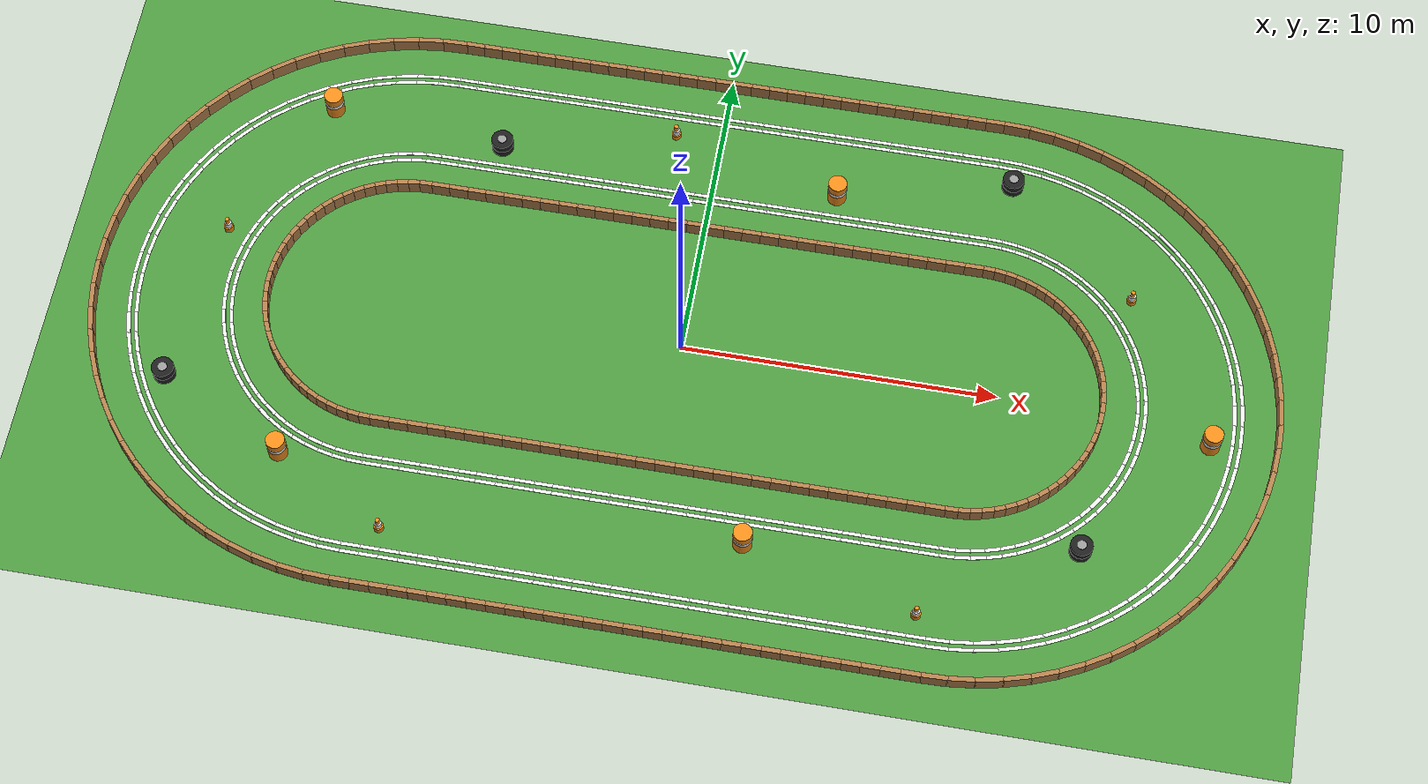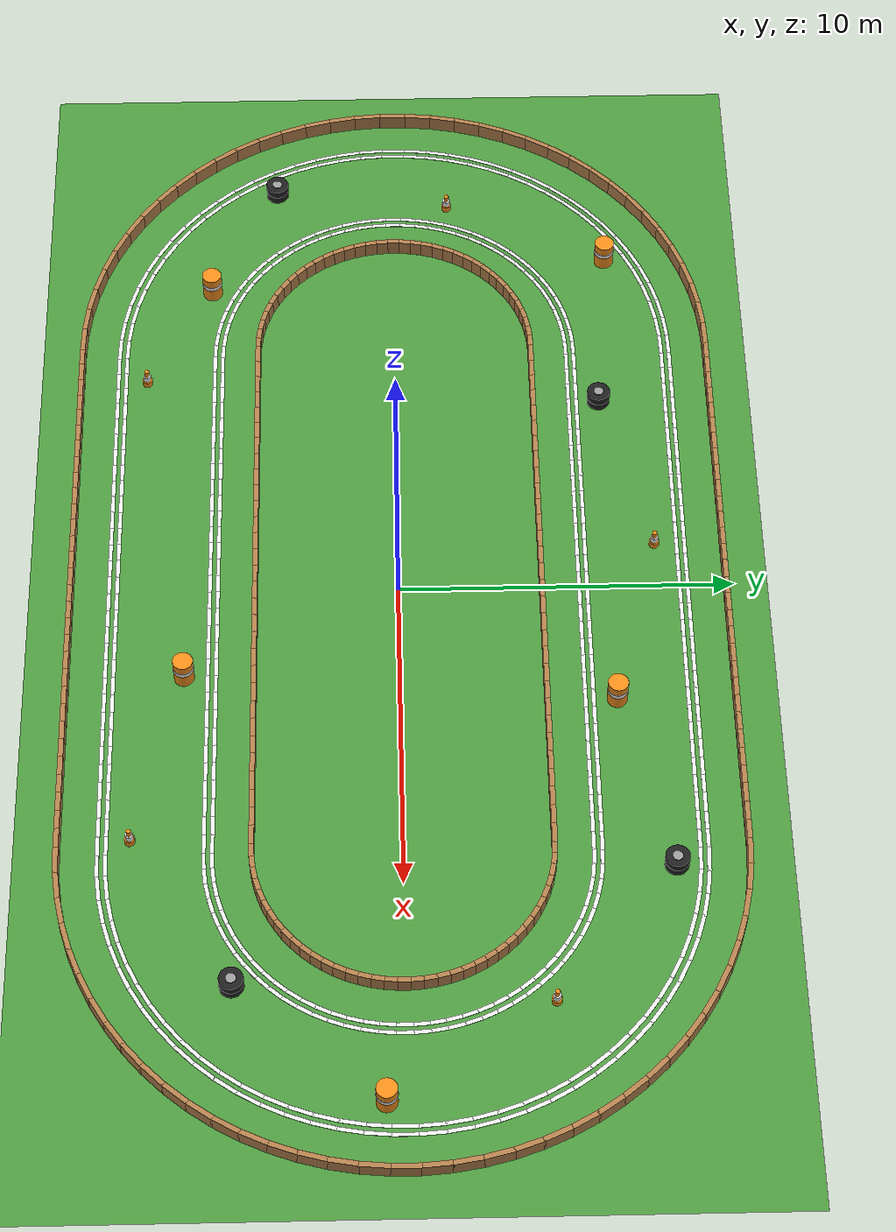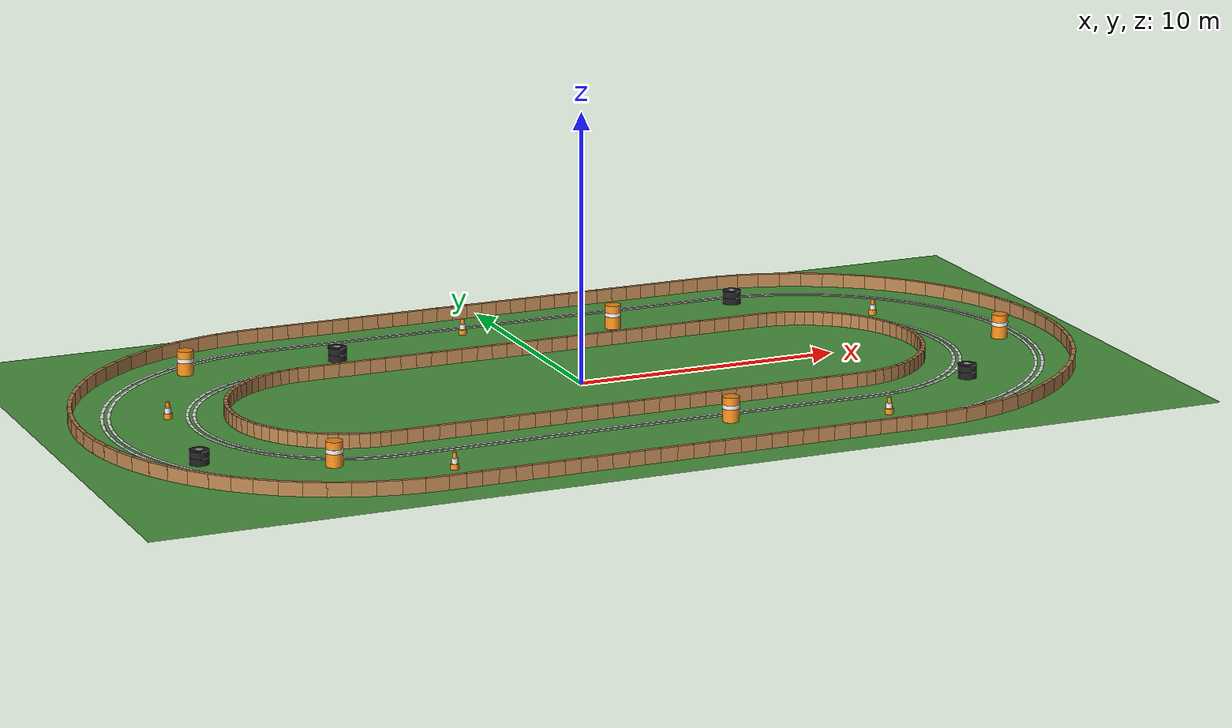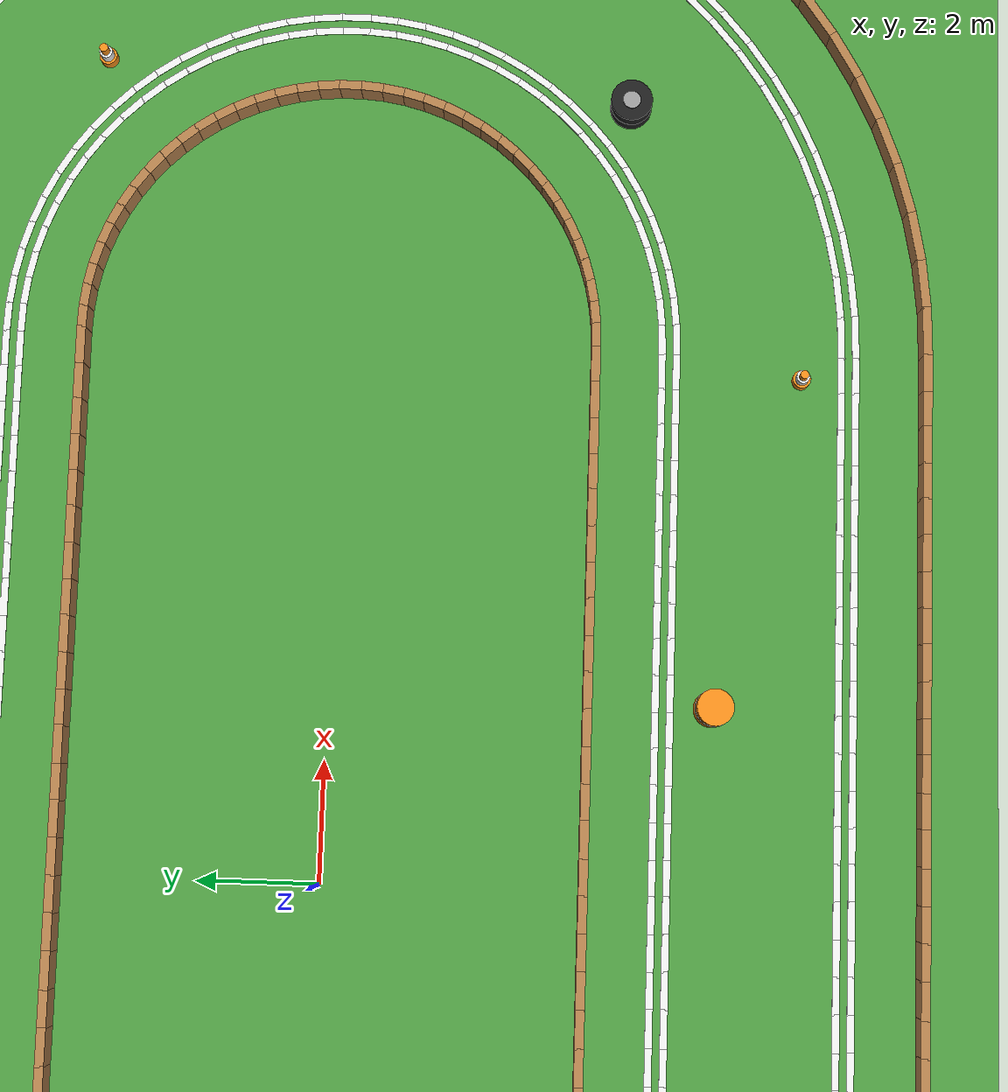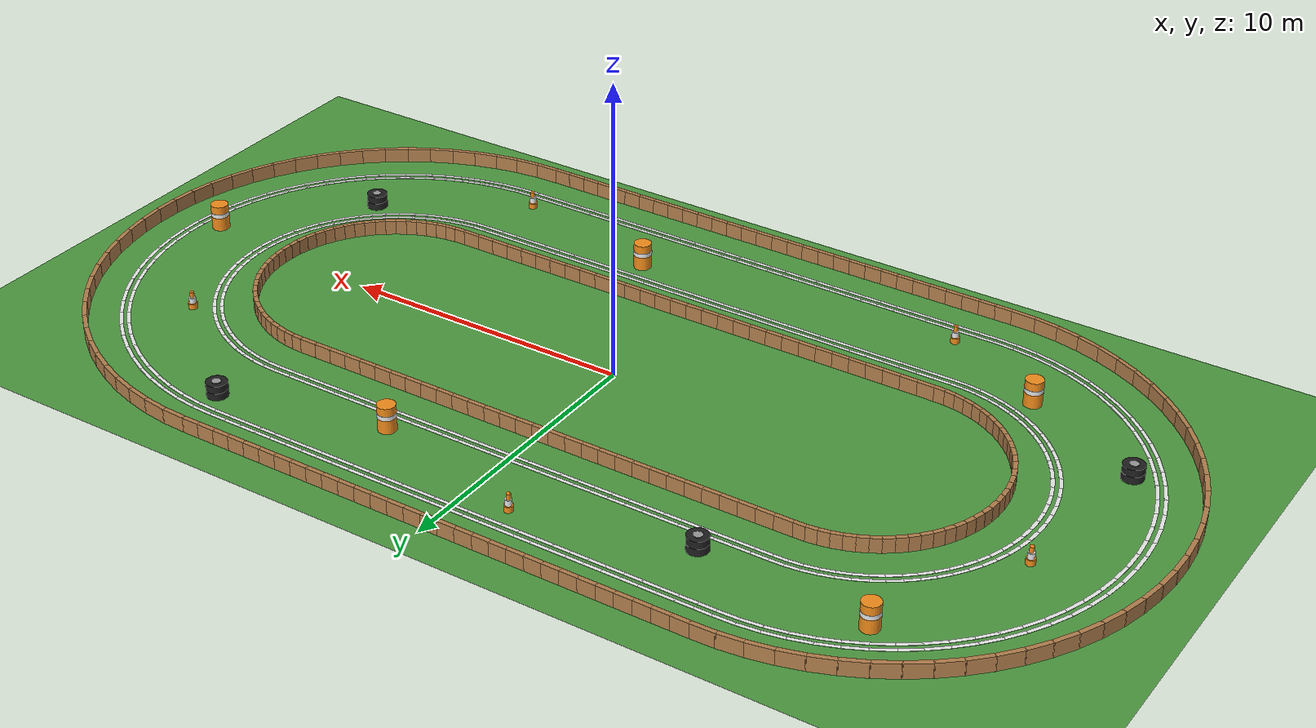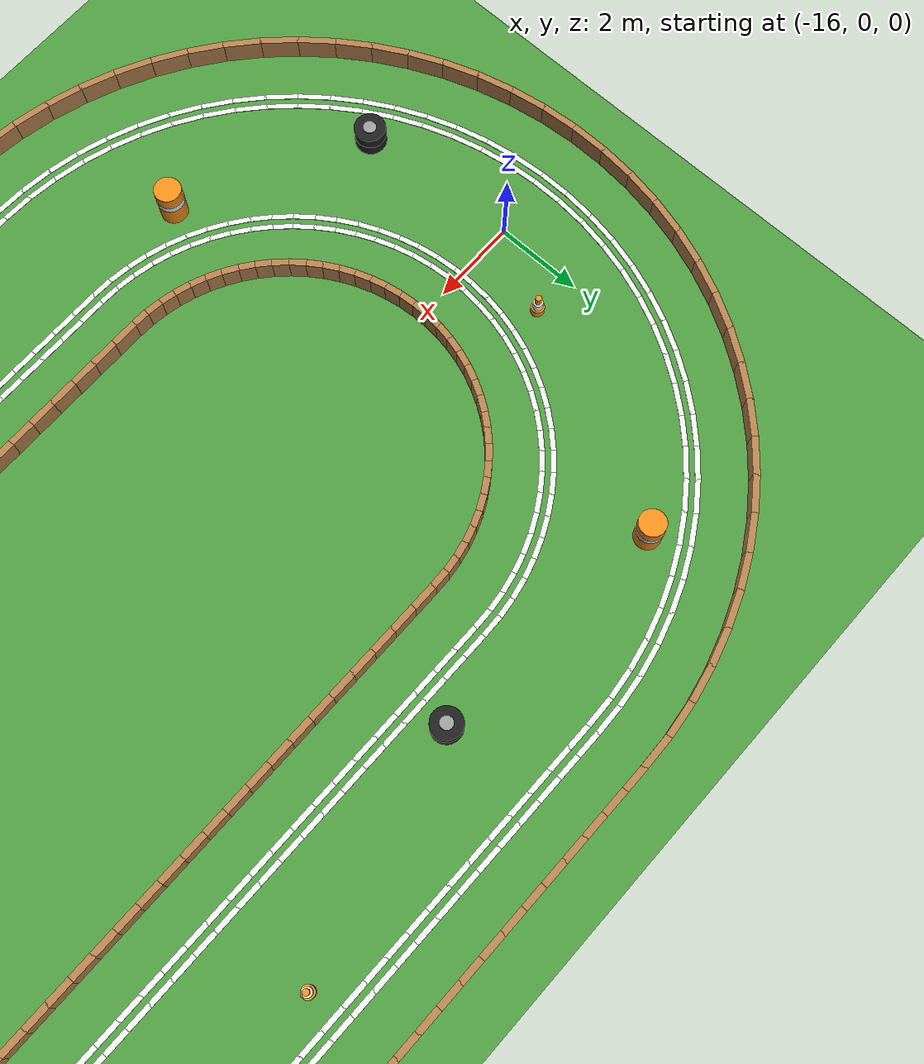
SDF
<?xml version="1.0"?>
<sdf version="1.6">
<world name="navigation_loop">
<include><uri>model://sun</uri></include>
<physics type="ode"><real_time_update_rate>1000</real_time_update_rate><max_step_size>0.001</max_step_size></physics>
<scene><ambient>0.6 0.6 0.6 1</ambient><shadows>false</shadows></scene>
<model name="grass"><static>true</static><link name="link">
<collision name="ground"><geometry><plane><normal>0 0 1</normal><size>40.0 22.0</size></plane></geometry><surface><friction><ode><mu>1</mu><mu2>1</mu2></ode></friction></surface></collision>
<visual name="grass_visual"><geometry><plane><normal>0 0 1</normal><size>40.0 22.0</size></plane></geometry><material><script><uri>file://media/materials/scripts/gazebo.material</uri><name>Gazebo/Grass</name></script></material></visual>
</link></model>
<model name="lane_lines"><static>true</static><link name="link">
<visual name="line_1.5_0.12_0"><pose>-8.702 -5.380 0.004 0 0 0.0000</pose><geometry><box><size>0.621 0.120 0.008</size></box></geometry><material><script><uri>file://media/materials/scripts/gazebo.material</uri><name>Gazebo/White</name></script></material></visual>

<visual name="line_1.5_0.12_1"><pose>-8.105 -5.380 0.004 0 0 0.0000</pose><geometry><box><size>0.621 0.120 0.008</size></box></geometry><material><script><uri>file://media/materials/scripts/gazebo.material</uri><name>Gazebo/White</name></script></material></visual>

<visual name="line_1.5_0.12_2"><pose>-7.508 -5.380 0.004 0 0 0.0000</pose><geometry><box><size>0.621 0.120 0.008</size></box></geometry><material><script><uri>file://media/materials/scripts/gazebo.material</uri><name>Gazebo/White</name></script></material></visual>

<visual name="line_1.5_0.12_3"><pose>-6.911 -5.380 0.004 0 0 0.0000</pose><geometry><box><size>0.621 0.120 0.008</size></box></geometry><material><script><uri>file://media/materials/scripts/gazebo.material</uri><name>Gazebo/White</name></script></material></visual>

<visual name="line_1.5_0.12_4"><pose>-6.314 -5.380 0.004 0 0 0.0000</pose><geometry><box><size>0.621 0.120 0.008</size></box></geometry><material><script><uri>file://media/materials/scripts/gazebo.material</uri><name>Gazebo/White</name></script></material></visual>

<visual name="line_1.5_0.12_5"><pose>-5.717 -5.380 0.004 0 0 0.0000</pose><geometry><box><size>0.621 0.120 0.008</size></box></geometry><material><script><uri>file://media/materials/scripts/gazebo.material</uri><name>Gazebo/White</name></script></material></visual>

<visual name="line_1.5_0.12_6"><pose>-5.120 -5.380 0.004 0 0 0.0000</pose><geometry><box><size>0.621 0.120 0.008</size></box></geometry><material><script><uri>file://media/materials/scripts/gazebo.material</uri><name>Gazebo/White</name></script></material></visual>

<visual name="line_1.5_0.12_7"><pose>-4.523 -5.380 0.004 0 0 0.0000</pose><geometry><box><size>0.621 0.120 0.008</size></box></geometry><material><script><uri>file://media/materials/scripts/gazebo.material</uri><name>Gazebo/White</name></script></material></visual>

<visual name="line_1.5_0.12_8"><pose>-3.926 -5.380 0.004 0 0 0.0000</pose><geometry><box><size>0.621 0.120 0.008</size></box></geometry><material><script><uri>file://media/materials/scripts/gazebo.material</uri><name>Gazebo/White</name></script></material></visual>

<visual name="line_1.5_0.12_9"><pose>-3.330 -5.380 0.004 0 0 0.0000</pose><geometry><box><size>0.621 0.120 0.008</size></box></geometry><material><script><uri>file://media/materials/scripts/gazebo.material</uri><name>Gazebo/White</name></script></material></visual>

<visual name="line_1.5_0.12_10"><pose>-2.733 -5.380 0.004 0 0 0.0000</pose><geometry><box><size>0.621 0.120 0.008</size></box></geometry><material><script><uri>file://media/materials/scripts/gazebo.material</uri><name>Gazebo/White</name></script></material></visual>

<visual name="line_1.5_0.12_11"><pose>-2.136 -5.380 0.004 0 0 0.0000</pose><geometry><box><size>0.621 0.120 0.008</size></box></geometry><material><script><uri>file://media/materials/scripts/gazebo.material</uri><name>Gazebo/White</name></script></material></visual>

<visual name="line_1.5_0.12_12"><pose>-1.539 -5.380 0.004 0 0 0.0000</pose><geometry><box><size>0.621 0.120 0.008</size></box></geometry><material><script><uri>file://media/materials/scripts/gazebo.material</uri><name>Gazebo/White</name></script></material></visual>

<visual name="line_1.5_0.12_13"><pose>-0.942 -5.380 0.004 0 0 0.0000</pose><geometry><box><size>0.621 0.120 0.008</size></box></geometry><material><script><uri>file://media/materials/scripts/gazebo.material</uri><name>Gazebo/White</name></script></material></visual>

<visual name="line_1.5_0.12_14"><pose>-0.345 -5.380 0.004 0 0 0.0000</pose><geometry><box><size>0.621 0.120 0.008</size></box></geometry><material><script><uri>file://media/materials/scripts/gazebo.material</uri><name>Gazebo/White</name></script></material></visual>

<visual name="line_1.5_0.12_15"><pose>0.252 -5.380 0.004 0 0 0.0000</pose><geometry><box><size>0.621 0.120 0.008</size></box></geometry><material><script><uri>file://media/materials/scripts/gazebo.material</uri><name>Gazebo/White</name></script></material></visual>

<visual name="line_1.5_0.12_16"><pose>0.849 -5.380 0.004 0 0 0.0000</pose><geometry><box><size>0.621 0.120 0.008</size></box></geometry><material><script><uri>file://media/materials/scripts/gazebo.material</uri><name>Gazebo/White</name></script></material></visual>

<visual name="line_1.5_0.12_17"><pose>1.445 -5.380 0.004 0 0 0.0000</pose><geometry><box><size>0.621 0.120 0.008</size></box></geometry><material><script><uri>file://media/materials/scripts/gazebo.material</uri><name>Gazebo/White</name></script></material></visual>

<visual name="line_1.5_0.12_18"><pose>2.042 -5.380 0.004 0 0 0.0000</pose><geometry><box><size>0.621 0.120 0.008</size></box></geometry><material><script><uri>file://media/materials/scripts/gazebo.material</uri><name>Gazebo/White</name></script></material></visual>

<visual name="line_1.5_0.12_19"><pose>2.639 -5.380 0.004 0 0 0.0000</pose><geometry><box><size>0.621 0.120 0.008</size></box></geometry><material><script><uri>file://media/materials/scripts/gazebo.material</uri><name>Gazebo/White</name></script></material></visual>

<visual name="line_1.5_0.12_20"><pose>3.236 -5.380 0.004 0 0 0.0000</pose><geometry><box><size>0.621 0.120 0.008</size></box></geometry><material><script><uri>file://media/materials/scripts/gazebo.material</uri><name>Gazebo/White</name></script></material></visual>

<visual name="line_1.5_0.12_21"><pose>3.833 -5.380 0.004 0 0 0.0000</pose><geometry><box><size>0.621 0.120 0.008</size></box></geometry><material><script><uri>file://media/materials/scripts/gazebo.material</uri><name>Gazebo/White</name></script></material></visual>

<visual name="line_1.5_0.12_22"><pose>4.430 -5.380 0.004 0 0 0.0000</pose><geometry><box><size>0.621 0.120 0.008</size></box></geometry><material><script><uri>file://media/materials/scripts/gazebo.material</uri><name>Gazebo/White</name></script></material></visual>

<visual name="line_1.5_0.12_23"><pose>5.027 -5.380 0.004 0 0 0.0000</pose><geometry><box><size>0.621 0.120 0.008</size></box></geometry><material><script><uri>file://media/materials/scripts/gazebo.material</uri><name>Gazebo/White</name></script></material></visual>

<visual name="line_1.5_0.12_24"><pose>5.624 -5.380 0.004 0 0 0.0000</pose><geometry><box><size>0.621 0.120 0.008</size></box></geometry><material><script><uri>file://media/materials/scripts/gazebo.material</uri><name>Gazebo/White</name></script></material></visual>

<visual name="line_1.5_0.12_25"><pose>6.221 -5.380 0.004 0 0 0.0000</pose><geometry><box><size>0.621 0.120 0.008</size></box></geometry><material><script><uri>file://media/materials/scripts/gazebo.material</uri><name>Gazebo/White</name></script></material></visual>

<visual name="line_1.5_0.12_26"><pose>6.817 -5.380 0.004 0 0 0.0000</pose><geometry><box><size>0.621 0.120 0.008</size></box></geometry><material><script><uri>file://media/materials/scripts/gazebo.material</uri><name>Gazebo/White</name></script></material></visual>

<visual name="line_1.5_0.12_27"><pose>7.414 -5.380 0.004 0 0 0.0000</pose><geometry><box><size>0.621 0.120 0.008</size></box></geometry><material><script><uri>file://media/materials/scripts/gazebo.material</uri><name>Gazebo/White</name></script></material></visual>

<visual name="line_1.5_0.12_28"><pose>8.011 -5.380 0.004 0 0 0.0000</pose><geometry><box><size>0.621 0.120 0.008</size></box></geometry><material><script><uri>file://media/materials/scripts/gazebo.material</uri><name>Gazebo/White</name></script></material></visual>

<visual name="line_1.5_0.12_29"><pose>8.608 -5.380 0.004 0 0 0.0000</pose><geometry><box><size>0.621 0.120 0.008</size></box></geometry><material><script><uri>file://media/materials/scripts/gazebo.material</uri><name>Gazebo/White</name></script></material></visual>

<visual name="line_1.5_0.12_30"><pose>9.147 -5.373 0.004 0 0 0.0290</pose><geometry><box><size>0.499 0.120 0.008</size></box></geometry><material><script><uri>file://media/materials/scripts/gazebo.material</uri><name>Gazebo/White</name></script></material></visual>

<visual name="line_1.5_0.12_31"><pose>9.614 -5.340 0.004 0 0 0.1145</pose><geometry><box><size>0.477 0.120 0.008</size></box></geometry><material><script><uri>file://media/materials/scripts/gazebo.material</uri><name>Gazebo/White</name></script></material></visual>

<visual name="line_1.5_0.12_32"><pose>10.067 -5.268 0.004 0 0 0.1998</pose><geometry><box><size>0.477 0.120 0.008</size></box></geometry><material><script><uri>file://media/materials/scripts/gazebo.material</uri><name>Gazebo/White</name></script></material></visual>

<visual name="line_1.5_0.12_33"><pose>10.512 -5.158 0.004 0 0 0.2851</pose><geometry><box><size>0.477 0.120 0.008</size></box></geometry><material><script><uri>file://media/materials/scripts/gazebo.material</uri><name>Gazebo/White</name></script></material></visual>

<visual name="line_1.5_0.12_34"><pose>10.945 -5.011 0.004 0 0 0.3704</pose><geometry><box><size>0.477 0.120 0.008</size></box></geometry><material><script><uri>file://media/materials/scripts/gazebo.material</uri><name>Gazebo/White</name></script></material></visual>

<visual name="line_1.5_0.12_35"><pose>11.365 -4.827 0.004 0 0 0.4556</pose><geometry><box><size>0.477 0.120 0.008</size></box></geometry><material><script><uri>file://media/materials/scripts/gazebo.material</uri><name>Gazebo/White</name></script></material></visual>

<visual name="line_1.5_0.12_36"><pose>11.768 -4.608 0.004 0 0 0.5409</pose><geometry><box><size>0.477 0.120 0.008</size></box></geometry><material><script><uri>file://media/materials/scripts/gazebo.material</uri><name>Gazebo/White</name></script></material></visual>

<visual name="line_1.5_0.12_37"><pose>12.150 -4.355 0.004 0 0 0.6262</pose><geometry><box><size>0.477 0.120 0.008</size></box></geometry><material><script><uri>file://media/materials/scripts/gazebo.material</uri><name>Gazebo/White</name></script></material></visual>

<visual name="line_1.5_0.12_38"><pose>12.509 -4.071 0.004 0 0 0.7114</pose><geometry><box><size>0.477 0.120 0.008</size></box></geometry><material><script><uri>file://media/materials/scripts/gazebo.material</uri><name>Gazebo/White</name></script></material></visual>

<visual name="line_1.5_0.12_39"><pose>12.843 -3.758 0.004 0 0 0.7967</pose><geometry><box><size>0.477 0.120 0.008</size></box></geometry><material><script><uri>file://media/materials/scripts/gazebo.material</uri><name>Gazebo/White</name></script></material></visual>

<visual name="line_1.5_0.12_40"><pose>13.150 -3.417 0.004 0 0 0.8820</pose><geometry><box><size>0.477 0.120 0.008</size></box></geometry><material><script><uri>file://media/materials/scripts/gazebo.material</uri><name>Gazebo/White</name></script></material></visual>

<visual name="line_1.5_0.12_41"><pose>13.425 -3.051 0.004 0 0 0.9672</pose><geometry><box><size>0.477 0.120 0.008</size></box></geometry><material><script><uri>file://media/materials/scripts/gazebo.material</uri><name>Gazebo/White</name></script></material></visual>

<visual name="line_1.5_0.12_42"><pose>13.669 -2.663 0.004 0 0 1.0525</pose><geometry><box><size>0.477 0.120 0.008</size></box></geometry><material><script><uri>file://media/materials/scripts/gazebo.material</uri><name>Gazebo/White</name></script></material></visual>

<visual name="line_1.5_0.12_43"><pose>13.879 -2.255 0.004 0 0 1.1378</pose><geometry><box><size>0.477 0.120 0.008</size></box></geometry><material><script><uri>file://media/materials/scripts/gazebo.material</uri><name>Gazebo/White</name></script></material></visual>

<visual name="line_1.5_0.12_44"><pose>14.053 -1.832 0.004 0 0 1.2230</pose><geometry><box><size>0.477 0.120 0.008</size></box></geometry><material><script><uri>file://media/materials/scripts/gazebo.material</uri><name>Gazebo/White</name></script></material></visual>

<visual name="line_1.5_0.12_45"><pose>14.191 -1.395 0.004 0 0 1.3083</pose><geometry><box><size>0.477 0.120 0.008</size></box></geometry><material><script><uri>file://media/materials/scripts/gazebo.material</uri><name>Gazebo/White</name></script></material></visual>

<visual name="line_1.5_0.12_46"><pose>14.291 -0.948 0.004 0 0 1.3936</pose><geometry><box><size>0.477 0.120 0.008</size></box></geometry><material><script><uri>file://media/materials/scripts/gazebo.material</uri><name>Gazebo/White</name></script></material></visual>

<visual name="line_1.5_0.12_47"><pose>14.352 -0.494 0.004 0 0 1.4788</pose><geometry><box><size>0.477 0.120 0.008</size></box></geometry><material><script><uri>file://media/materials/scripts/gazebo.material</uri><name>Gazebo/White</name></script></material></visual>

<visual name="line_1.5_0.12_48"><pose>14.375 -0.036 0.004 0 0 1.5641</pose><geometry><box><size>0.477 0.120 0.008</size></box></geometry><material><script><uri>file://media/materials/scripts/gazebo.material</uri><name>Gazebo/White</name></script></material></visual>

<visual name="line_1.5_0.12_49"><pose>14.359 0.422 0.004 0 0 1.6494</pose><geometry><box><size>0.477 0.120 0.008</size></box></geometry><material><script><uri>file://media/materials/scripts/gazebo.material</uri><name>Gazebo/White</name></script></material></visual>

<visual name="line_1.5_0.12_50"><pose>14.303 0.877 0.004 0 0 1.7347</pose><geometry><box><size>0.477 0.120 0.008</size></box></geometry><material><script><uri>file://media/materials/scripts/gazebo.material</uri><name>Gazebo/White</name></script></material></visual>

<visual name="line_1.5_0.12_51"><pose>14.209 1.325 0.004 0 0 1.8199</pose><geometry><box><size>0.477 0.120 0.008</size></box></geometry><material><script><uri>file://media/materials/scripts/gazebo.material</uri><name>Gazebo/White</name></script></material></visual>

<visual name="line_1.5_0.12_52"><pose>14.077 1.764 0.004 0 0 1.9052</pose><geometry><box><size>0.477 0.120 0.008</size></box></geometry><material><script><uri>file://media/materials/scripts/gazebo.material</uri><name>Gazebo/White</name></script></material></visual>

<visual name="line_1.5_0.12_53"><pose>13.909 2.190 0.004 0 0 1.9905</pose><geometry><box><size>0.477 0.120 0.008</size></box></geometry><material><script><uri>file://media/materials/scripts/gazebo.material</uri><name>Gazebo/White</name></script></material></visual>

<visual name="line_1.5_0.12_54"><pose>13.704 2.600 0.004 0 0 2.0757</pose><geometry><box><size>0.477 0.120 0.008</size></box></geometry><material><script><uri>file://media/materials/scripts/gazebo.material</uri><name>Gazebo/White</name></script></material></visual>

<visual name="line_1.5_0.12_55"><pose>13.466 2.991 0.004 0 0 2.1610</pose><geometry><box><size>0.477 0.120 0.008</size></box></geometry><material><script><uri>file://media/materials/scripts/gazebo.material</uri><name>Gazebo/White</name></script></material></visual>

<visual name="line_1.5_0.12_56"><pose>13.195 3.361 0.004 0 0 2.2463</pose><geometry><box><size>0.477 0.120 0.008</size></box></geometry><material><script><uri>file://media/materials/scripts/gazebo.material</uri><name>Gazebo/White</name></script></material></visual>

<visual name="line_1.5_0.12_57"><pose>12.893 3.706 0.004 0 0 2.3315</pose><geometry><box><size>0.477 0.120 0.008</size></box></geometry><material><script><uri>file://media/materials/scripts/gazebo.material</uri><name>Gazebo/White</name></script></material></visual>

<visual name="line_1.5_0.12_58"><pose>12.564 4.024 0.004 0 0 2.4168</pose><geometry><box><size>0.477 0.120 0.008</size></box></geometry><material><script><uri>file://media/materials/scripts/gazebo.material</uri><name>Gazebo/White</name></script></material></visual>

<visual name="line_1.5_0.12_59"><pose>12.208 4.313 0.004 0 0 2.5021</pose><geometry><box><size>0.477 0.120 0.008</size></box></geometry><material><script><uri>file://media/materials/scripts/gazebo.material</uri><name>Gazebo/White</name></script></material></visual>

<visual name="line_1.5_0.12_60"><pose>11.829 4.570 0.004 0 0 2.5873</pose><geometry><box><size>0.477 0.120 0.008</size></box></geometry><material><script><uri>file://media/materials/scripts/gazebo.material</uri><name>Gazebo/White</name></script></material></visual>

<visual name="line_1.5_0.12_61"><pose>11.429 4.795 0.004 0 0 2.6726</pose><geometry><box><size>0.477 0.120 0.008</size></box></geometry><material><script><uri>file://media/materials/scripts/gazebo.material</uri><name>Gazebo/White</name></script></material></visual>

<visual name="line_1.5_0.12_62"><pose>11.012 4.984 0.004 0 0 2.7579</pose><geometry><box><size>0.477 0.120 0.008</size></box></geometry><material><script><uri>file://media/materials/scripts/gazebo.material</uri><name>Gazebo/White</name></script></material></visual>

<visual name="line_1.5_0.12_63"><pose>10.580 5.138 0.004 0 0 2.8432</pose><geometry><box><size>0.477 0.120 0.008</size></box></geometry><material><script><uri>file://media/materials/scripts/gazebo.material</uri><name>Gazebo/White</name></script></material></visual>

<visual name="line_1.5_0.12_64"><pose>10.137 5.253 0.004 0 0 2.9284</pose><geometry><box><size>0.477 0.120 0.008</size></box></geometry><material><script><uri>file://media/materials/scripts/gazebo.material</uri><name>Gazebo/White</name></script></material></visual>

<visual name="line_1.5_0.12_65"><pose>9.686 5.331 0.004 0 0 3.0137</pose><geometry><box><size>0.477 0.120 0.008</size></box></geometry><material><script><uri>file://media/materials/scripts/gazebo.material</uri><name>Gazebo/White</name></script></material></visual>

<visual name="line_1.5_0.12_66"><pose>9.229 5.370 0.004 0 0 3.0990</pose><geometry><box><size>0.477 0.120 0.008</size></box></geometry><material><script><uri>file://media/materials/scripts/gazebo.material</uri><name>Gazebo/White</name></script></material></visual>

<visual name="line_1.5_0.12_67"><pose>8.702 5.380 0.004 0 0 3.1416</pose><geometry><box><size>0.621 0.120 0.008</size></box></geometry><material><script><uri>file://media/materials/scripts/gazebo.material</uri><name>Gazebo/White</name></script></material></visual>

<visual name="line_1.5_0.12_68"><pose>8.105 5.380 0.004 0 0 3.1416</pose><geometry><box><size>0.621 0.120 0.008</size></box></geometry><material><script><uri>file://media/materials/scripts/gazebo.material</uri><name>Gazebo/White</name></script></material></visual>

<visual name="line_1.5_0.12_69"><pose>7.508 5.380 0.004 0 0 3.1416</pose><geometry><box><size>0.621 0.120 0.008</size></box></geometry><material><script><uri>file://media/materials/scripts/gazebo.material</uri><name>Gazebo/White</name></script></material></visual>

<visual name="line_1.5_0.12_70"><pose>6.911 5.380 0.004 0 0 3.1416</pose><geometry><box><size>0.621 0.120 0.008</size></box></geometry><material><script><uri>file://media/materials/scripts/gazebo.material</uri><name>Gazebo/White</name></script></material></visual>

<visual name="line_1.5_0.12_71"><pose>6.314 5.380 0.004 0 0 3.1416</pose><geometry><box><size>0.621 0.120 0.008</size></box></geometry><material><script><uri>file://media/materials/scripts/gazebo.material</uri><name>Gazebo/White</name></script></material></visual>

<visual name="line_1.5_0.12_72"><pose>5.717 5.380 0.004 0 0 3.1416</pose><geometry><box><size>0.621 0.120 0.008</size></box></geometry><material><script><uri>file://media/materials/scripts/gazebo.material</uri><name>Gazebo/White</name></script></material></visual>

<visual name="line_1.5_0.12_73"><pose>5.120 5.380 0.004 0 0 3.1416</pose><geometry><box><size>0.621 0.120 0.008</size></box></geometry><material><script><uri>file://media/materials/scripts/gazebo.material</uri><name>Gazebo/White</name></script></material></visual>

<visual name="line_1.5_0.12_74"><pose>4.523 5.380 0.004 0 0 3.1416</pose><geometry><box><size>0.621 0.120 0.008</size></box></geometry><material><script><uri>file://media/materials/scripts/gazebo.material</uri><name>Gazebo/White</name></script></material></visual>

<visual name="line_1.5_0.12_75"><pose>3.926 5.380 0.004 0 0 3.1416</pose><geometry><box><size>0.621 0.120 0.008</size></box></geometry><material><script><uri>file://media/materials/scripts/gazebo.material</uri><name>Gazebo/White</name></script></material></visual>

<visual name="line_1.5_0.12_76"><pose>3.330 5.380 0.004 0 0 3.1416</pose><geometry><box><size>0.621 0.120 0.008</size></box></geometry><material><script><uri>file://media/materials/scripts/gazebo.material</uri><name>Gazebo/White</name></script></material></visual>

<visual name="line_1.5_0.12_77"><pose>2.733 5.380 0.004 0 0 3.1416</pose><geometry><box><size>0.621 0.120 0.008</size></box></geometry><material><script><uri>file://media/materials/scripts/gazebo.material</uri><name>Gazebo/White</name></script></material></visual>

<visual name="line_1.5_0.12_78"><pose>2.136 5.380 0.004 0 0 3.1416</pose><geometry><box><size>0.621 0.120 0.008</size></box></geometry><material><script><uri>file://media/materials/scripts/gazebo.material</uri><name>Gazebo/White</name></script></material></visual>

<visual name="line_1.5_0.12_79"><pose>1.539 5.380 0.004 0 0 3.1416</pose><geometry><box><size>0.621 0.120 0.008</size></box></geometry><material><script><uri>file://media/materials/scripts/gazebo.material</uri><name>Gazebo/White</name></script></material></visual>

<visual name="line_1.5_0.12_80"><pose>0.942 5.380 0.004 0 0 3.1416</pose><geometry><box><size>0.621 0.120 0.008</size></box></geometry><material><script><uri>file://media/materials/scripts/gazebo.material</uri><name>Gazebo/White</name></script></material></visual>

<visual name="line_1.5_0.12_81"><pose>0.345 5.380 0.004 0 0 3.1416</pose><geometry><box><size>0.621 0.120 0.008</size></box></geometry><material><script><uri>file://media/materials/scripts/gazebo.material</uri><name>Gazebo/White</name></script></material></visual>

<visual name="line_1.5_0.12_82"><pose>-0.252 5.380 0.004 0 0 3.1416</pose><geometry><box><size>0.621 0.120 0.008</size></box></geometry><material><script><uri>file://media/materials/scripts/gazebo.material</uri><name>Gazebo/White</name></script></material></visual>

<visual name="line_1.5_0.12_83"><pose>-0.849 5.380 0.004 0 0 3.1416</pose><geometry><box><size>0.621 0.120 0.008</size></box></geometry><material><script><uri>file://media/materials/scripts/gazebo.material</uri><name>Gazebo/White</name></script></material></visual>

<visual name="line_1.5_0.12_84"><pose>-1.445 5.380 0.004 0 0 3.1416</pose><geometry><box><size>0.621 0.120 0.008</size></box></geometry><material><script><uri>file://media/materials/scripts/gazebo.material</uri><name>Gazebo/White</name></script></material></visual>

<visual name="line_1.5_0.12_85"><pose>-2.042 5.380 0.004 0 0 3.1416</pose><geometry><box><size>0.621 0.120 0.008</size></box></geometry><material><script><uri>file://media/materials/scripts/gazebo.material</uri><name>Gazebo/White</name></script></material></visual>

<visual name="line_1.5_0.12_86"><pose>-2.639 5.380 0.004 0 0 3.1416</pose><geometry><box><size>0.621 0.120 0.008</size></box></geometry><material><script><uri>file://media/materials/scripts/gazebo.material</uri><name>Gazebo/White</name></script></material></visual>

<visual name="line_1.5_0.12_87"><pose>-3.236 5.380 0.004 0 0 3.1416</pose><geometry><box><size>0.621 0.120 0.008</size></box></geometry><material><script><uri>file://media/materials/scripts/gazebo.material</uri><name>Gazebo/White</name></script></material></visual>

<visual name="line_1.5_0.12_88"><pose>-3.833 5.380 0.004 0 0 3.1416</pose><geometry><box><size>0.621 0.120 0.008</size></box></geometry><material><script><uri>file://media/materials/scripts/gazebo.material</uri><name>Gazebo/White</name></script></material></visual>

<visual name="line_1.5_0.12_89"><pose>-4.430 5.380 0.004 0 0 3.1416</pose><geometry><box><size>0.621 0.120 0.008</size></box></geometry><material><script><uri>file://media/materials/scripts/gazebo.material</uri><name>Gazebo/White</name></script></material></visual>

<visual name="line_1.5_0.12_90"><pose>-5.027 5.380 0.004 0 0 3.1416</pose><geometry><box><size>0.621 0.120 0.008</size></box></geometry><material><script><uri>file://media/materials/scripts/gazebo.material</uri><name>Gazebo/White</name></script></material></visual>

<visual name="line_1.5_0.12_91"><pose>-5.624 5.380 0.004 0 0 3.1416</pose><geometry><box><size>0.621 0.120 0.008</size></box></geometry><material><script><uri>file://media/materials/scripts/gazebo.material</uri><name>Gazebo/White</name></script></material></visual>

<visual name="line_1.5_0.12_92"><pose>-6.221 5.380 0.004 0 0 3.1416</pose><geometry><box><size>0.621 0.120 0.008</size></box></geometry><material><script><uri>file://media/materials/scripts/gazebo.material</uri><name>Gazebo/White</name></script></material></visual>

<visual name="line_1.5_0.12_93"><pose>-6.817 5.380 0.004 0 0 3.1416</pose><geometry><box><size>0.621 0.120 0.008</size></box></geometry><material><script><uri>file://media/materials/scripts/gazebo.material</uri><name>Gazebo/White</name></script></material></visual>

<visual name="line_1.5_0.12_94"><pose>-7.414 5.380 0.004 0 0 3.1416</pose><geometry><box><size>0.621 0.120 0.008</size></box></geometry><material><script><uri>file://media/materials/scripts/gazebo.material</uri><name>Gazebo/White</name></script></material></visual>

<visual name="line_1.5_0.12_95"><pose>-8.011 5.380 0.004 0 0 3.1416</pose><geometry><box><size>0.621 0.120 0.008</size></box></geometry><material><script><uri>file://media/materials/scripts/gazebo.material</uri><name>Gazebo/White</name></script></material></visual>

<visual name="line_1.5_0.12_96"><pose>-8.608 5.380 0.004 0 0 3.1416</pose><geometry><box><size>0.621 0.120 0.008</size></box></geometry><material><script><uri>file://media/materials/scripts/gazebo.material</uri><name>Gazebo/White</name></script></material></visual>

<visual name="line_1.5_0.12_97"><pose>-9.147 5.373 0.004 0 0 -3.1126</pose><geometry><box><size>0.499 0.120 0.008</size></box></geometry><material><script><uri>file://media/materials/scripts/gazebo.material</uri><name>Gazebo/White</name></script></material></visual>

<visual name="line_1.5_0.12_98"><pose>-9.614 5.340 0.004 0 0 -3.0270</pose><geometry><box><size>0.477 0.120 0.008</size></box></geometry><material><script><uri>file://media/materials/scripts/gazebo.material</uri><name>Gazebo/White</name></script></material></visual>

<visual name="line_1.5_0.12_99"><pose>-10.067 5.268 0.004 0 0 -2.9418</pose><geometry><box><size>0.477 0.120 0.008</size></box></geometry><material><script><uri>file://media/materials/scripts/gazebo.material</uri><name>Gazebo/White</name></script></material></visual>

<visual name="line_1.5_0.12_100"><pose>-10.512 5.158 0.004 0 0 -2.8565</pose><geometry><box><size>0.477 0.120 0.008</size></box></geometry><material><script><uri>file://media/materials/scripts/gazebo.material</uri><name>Gazebo/White</name></script></material></visual>

<visual name="line_1.5_0.12_101"><pose>-10.945 5.011 0.004 0 0 -2.7712</pose><geometry><box><size>0.477 0.120 0.008</size></box></geometry><material><script><uri>file://media/materials/scripts/gazebo.material</uri><name>Gazebo/White</name></script></material></visual>

<visual name="line_1.5_0.12_102"><pose>-11.365 4.827 0.004 0 0 -2.6860</pose><geometry><box><size>0.477 0.120 0.008</size></box></geometry><material><script><uri>file://media/materials/scripts/gazebo.material</uri><name>Gazebo/White</name></script></material></visual>

<visual name="line_1.5_0.12_103"><pose>-11.768 4.608 0.004 0 0 -2.6007</pose><geometry><box><size>0.477 0.120 0.008</size></box></geometry><material><script><uri>file://media/materials/scripts/gazebo.material</uri><name>Gazebo/White</name></script></material></visual>

<visual name="line_1.5_0.12_104"><pose>-12.150 4.355 0.004 0 0 -2.5154</pose><geometry><box><size>0.477 0.120 0.008</size></box></geometry><material><script><uri>file://media/materials/scripts/gazebo.material</uri><name>Gazebo/White</name></script></material></visual>

<visual name="line_1.5_0.12_105"><pose>-12.509 4.071 0.004 0 0 -2.4302</pose><geometry><box><size>0.477 0.120 0.008</size></box></geometry><material><script><uri>file://media/materials/scripts/gazebo.material</uri><name>Gazebo/White</name></script></material></visual>

<visual name="line_1.5_0.12_106"><pose>-12.843 3.758 0.004 0 0 -2.3449</pose><geometry><box><size>0.477 0.120 0.008</size></box></geometry><material><script><uri>file://media/materials/scripts/gazebo.material</uri><name>Gazebo/White</name></script></material></visual>

<visual name="line_1.5_0.12_107"><pose>-13.150 3.417 0.004 0 0 -2.2596</pose><geometry><box><size>0.477 0.120 0.008</size></box></geometry><material><script><uri>file://media/materials/scripts/gazebo.material</uri><name>Gazebo/White</name></script></material></visual>

<visual name="line_1.5_0.12_108"><pose>-13.425 3.051 0.004 0 0 -2.1744</pose><geometry><box><size>0.477 0.120 0.008</size></box></geometry><material><script><uri>file://media/materials/scripts/gazebo.material</uri><name>Gazebo/White</name></script></material></visual>

<visual name="line_1.5_0.12_109"><pose>-13.669 2.663 0.004 0 0 -2.0891</pose><geometry><box><size>0.477 0.120 0.008</size></box></geometry><material><script><uri>file://media/materials/scripts/gazebo.material</uri><name>Gazebo/White</name></script></material></visual>

<visual name="line_1.5_0.12_110"><pose>-13.879 2.255 0.004 0 0 -2.0038</pose><geometry><box><size>0.477 0.120 0.008</size></box></geometry><material><script><uri>file://media/materials/scripts/gazebo.material</uri><name>Gazebo/White</name></script></material></visual>

<visual name="line_1.5_0.12_111"><pose>-14.053 1.832 0.004 0 0 -1.9186</pose><geometry><box><size>0.477 0.120 0.008</size></box></geometry><material><script><uri>file://media/materials/scripts/gazebo.material</uri><name>Gazebo/White</name></script></material></visual>

<visual name="line_1.5_0.12_112"><pose>-14.191 1.395 0.004 0 0 -1.8333</pose><geometry><box><size>0.477 0.120 0.008</size></box></geometry><material><script><uri>file://media/materials/scripts/gazebo.material</uri><name>Gazebo/White</name></script></material></visual>

<visual name="line_1.5_0.12_113"><pose>-14.291 0.948 0.004 0 0 -1.7480</pose><geometry><box><size>0.477 0.120 0.008</size></box></geometry><material><script><uri>file://media/materials/scripts/gazebo.material</uri><name>Gazebo/White</name></script></material></visual>

<visual name="line_1.5_0.12_114"><pose>-14.352 0.494 0.004 0 0 -1.6627</pose><geometry><box><size>0.477 0.120 0.008</size></box></geometry><material><script><uri>file://media/materials/scripts/gazebo.material</uri><name>Gazebo/White</name></script></material></visual>

<visual name="line_1.5_0.12_115"><pose>-14.375 0.036 0.004 0 0 -1.5775</pose><geometry><box><size>0.477 0.120 0.008</size></box></geometry><material><script><uri>file://media/materials/scripts/gazebo.material</uri><name>Gazebo/White</name></script></material></visual>

<visual name="line_1.5_0.12_116"><pose>-14.359 -0.422 0.004 0 0 -1.4922</pose><geometry><box><size>0.477 0.120 0.008</size></box></geometry><material><script><uri>file://media/materials/scripts/gazebo.material</uri><name>Gazebo/White</name></script></material></visual>

<visual name="line_1.5_0.12_117"><pose>-14.303 -0.877 0.004 0 0 -1.4069</pose><geometry><box><size>0.477 0.120 0.008</size></box></geometry><material><script><uri>file://media/materials/scripts/gazebo.material</uri><name>Gazebo/White</name></script></material></visual>

<visual name="line_1.5_0.12_118"><pose>-14.209 -1.325 0.004 0 0 -1.3217</pose><geometry><box><size>0.477 0.120 0.008</size></box></geometry><material><script><uri>file://media/materials/scripts/gazebo.material</uri><name>Gazebo/White</name></script></material></visual>

<visual name="line_1.5_0.12_119"><pose>-14.077 -1.764 0.004 0 0 -1.2364</pose><geometry><box><size>0.477 0.120 0.008</size></box></geometry><material><script><uri>file://media/materials/scripts/gazebo.material</uri><name>Gazebo/White</name></script></material></visual>

<visual name="line_1.5_0.12_120"><pose>-13.909 -2.190 0.004 0 0 -1.1511</pose><geometry><box><size>0.477 0.120 0.008</size></box></geometry><material><script><uri>file://media/materials/scripts/gazebo.material</uri><name>Gazebo/White</name></script></material></visual>

<visual name="line_1.5_0.12_121"><pose>-13.704 -2.600 0.004 0 0 -1.0659</pose><geometry><box><size>0.477 0.120 0.008</size></box></geometry><material><script><uri>file://media/materials/scripts/gazebo.material</uri><name>Gazebo/White</name></script></material></visual>

<visual name="line_1.5_0.12_122"><pose>-13.466 -2.991 0.004 0 0 -0.9806</pose><geometry><box><size>0.477 0.120 0.008</size></box></geometry><material><script><uri>file://media/materials/scripts/gazebo.material</uri><name>Gazebo/White</name></script></material></visual>

<visual name="line_1.5_0.12_123"><pose>-13.195 -3.361 0.004 0 0 -0.8953</pose><geometry><box><size>0.477 0.120 0.008</size></box></geometry><material><script><uri>file://media/materials/scripts/gazebo.material</uri><name>Gazebo/White</name></script></material></visual>

<visual name="line_1.5_0.12_124"><pose>-12.893 -3.706 0.004 0 0 -0.8101</pose><geometry><box><size>0.477 0.120 0.008</size></box></geometry><material><script><uri>file://media/materials/scripts/gazebo.material</uri><name>Gazebo/White</name></script></material></visual>

<visual name="line_1.5_0.12_125"><pose>-12.564 -4.024 0.004 0 0 -0.7248</pose><geometry><box><size>0.477 0.120 0.008</size></box></geometry><material><script><uri>file://media/materials/scripts/gazebo.material</uri><name>Gazebo/White</name></script></material></visual>

<visual name="line_1.5_0.12_126"><pose>-12.208 -4.313 0.004 0 0 -0.6395</pose><geometry><box><size>0.477 0.120 0.008</size></box></geometry><material><script><uri>file://media/materials/scripts/gazebo.material</uri><name>Gazebo/White</name></script></material></visual>

<visual name="line_1.5_0.12_127"><pose>-11.829 -4.570 0.004 0 0 -0.5542</pose><geometry><box><size>0.477 0.120 0.008</size></box></geometry><material><script><uri>file://media/materials/scripts/gazebo.material</uri><name>Gazebo/White</name></script></material></visual>

<visual name="line_1.5_0.12_128"><pose>-11.429 -4.795 0.004 0 0 -0.4690</pose><geometry><box><size>0.477 0.120 0.008</size></box></geometry><material><script><uri>file://media/materials/scripts/gazebo.material</uri><name>Gazebo/White</name></script></material></visual>

<visual name="line_1.5_0.12_129"><pose>-11.012 -4.984 0.004 0 0 -0.3837</pose><geometry><box><size>0.477 0.120 0.008</size></box></geometry><material><script><uri>file://media/materials/scripts/gazebo.material</uri><name>Gazebo/White</name></script></material></visual>

<visual name="line_1.5_0.12_130"><pose>-10.580 -5.138 0.004 0 0 -0.2984</pose><geometry><box><size>0.477 0.120 0.008</size></box></geometry><material><script><uri>file://media/materials/scripts/gazebo.material</uri><name>Gazebo/White</name></script></material></visual>

<visual name="line_1.5_0.12_131"><pose>-10.137 -5.253 0.004 0 0 -0.2132</pose><geometry><box><size>0.477 0.120 0.008</size></box></geometry><material><script><uri>file://media/materials/scripts/gazebo.material</uri><name>Gazebo/White</name></script></material></visual>

<visual name="line_1.5_0.12_132"><pose>-9.686 -5.331 0.004 0 0 -0.1279</pose><geometry><box><size>0.477 0.120 0.008</size></box></geometry><material><script><uri>file://media/materials/scripts/gazebo.material</uri><name>Gazebo/White</name></script></material></visual>

<visual name="line_1.5_0.12_133"><pose>-9.229 -5.370 0.004 0 0 -0.0426</pose><geometry><box><size>0.477 0.120 0.008</size></box></geometry><material><script><uri>file://media/materials/scripts/gazebo.material</uri><name>Gazebo/White</name></script></material></visual>

<visual name="line_1.5_-0.12_0"><pose>-8.702 -5.620 0.004 0 0 0.0000</pose><geometry><box><size>0.621 0.120 0.008</size></box></geometry><material><script><uri>file://media/materials/scripts/gazebo.material</uri><name>Gazebo/White</name></script></material></visual>

<visual name="line_1.5_-0.12_1"><pose>-8.105 -5.620 0.004 0 0 0.0000</pose><geometry><box><size>0.621 0.120 0.008</size></box></geometry><material><script><uri>file://media/materials/scripts/gazebo.material</uri><name>Gazebo/White</name></script></material></visual>

<visual name="line_1.5_-0.12_2"><pose>-7.508 -5.620 0.004 0 0 0.0000</pose><geometry><box><size>0.621 0.120 0.008</size></box></geometry><material><script><uri>file://media/materials/scripts/gazebo.material</uri><name>Gazebo/White</name></script></material></visual>

<visual name="line_1.5_-0.12_3"><pose>-6.911 -5.620 0.004 0 0 0.0000</pose><geometry><box><size>0.621 0.120 0.008</size></box></geometry><material><script><uri>file://media/materials/scripts/gazebo.material</uri><name>Gazebo/White</name></script></material></visual>

<visual name="line_1.5_-0.12_4"><pose>-6.314 -5.620 0.004 0 0 0.0000</pose><geometry><box><size>0.621 0.120 0.008</size></box></geometry><material><script><uri>file://media/materials/scripts/gazebo.material</uri><name>Gazebo/White</name></script></material></visual>

<visual name="line_1.5_-0.12_5"><pose>-5.717 -5.620 0.004 0 0 0.0000</pose><geometry><box><size>0.621 0.120 0.008</size></box></geometry><material><script><uri>file://media/materials/scripts/gazebo.material</uri><name>Gazebo/White</name></script></material></visual>

<visual name="line_1.5_-0.12_6"><pose>-5.120 -5.620 0.004 0 0 0.0000</pose><geometry><box><size>0.621 0.120 0.008</size></box></geometry><material><script><uri>file://media/materials/scripts/gazebo.material</uri><name>Gazebo/White</name></script></material></visual>

<visual name="line_1.5_-0.12_7"><pose>-4.523 -5.620 0.004 0 0 0.0000</pose><geometry><box><size>0.621 0.120 0.008</size></box></geometry><material><script><uri>file://media/materials/scripts/gazebo.material</uri><name>Gazebo/White</name></script></material></visual>

<visual name="line_1.5_-0.12_8"><pose>-3.926 -5.620 0.004 0 0 0.0000</pose><geometry><box><size>0.621 0.120 0.008</size></box></geometry><material><script><uri>file://media/materials/scripts/gazebo.material</uri><name>Gazebo/White</name></script></material></visual>

<visual name="line_1.5_-0.12_9"><pose>-3.330 -5.620 0.004 0 0 0.0000</pose><geometry><box><size>0.621 0.120 0.008</size></box></geometry><material><script><uri>file://media/materials/scripts/gazebo.material</uri><name>Gazebo/White</name></script></material></visual>

<visual name="line_1.5_-0.12_10"><pose>-2.733 -5.620 0.004 0 0 0.0000</pose><geometry><box><size>0.621 0.120 0.008</size></box></geometry><material><script><uri>file://media/materials/scripts/gazebo.material</uri><name>Gazebo/White</name></script></material></visual>

<visual name="line_1.5_-0.12_11"><pose>-2.136 -5.620 0.004 0 0 0.0000</pose><geometry><box><size>0.621 0.120 0.008</size></box></geometry><material><script><uri>file://media/materials/scripts/gazebo.material</uri><name>Gazebo/White</name></script></material></visual>

<visual name="line_1.5_-0.12_12"><pose>-1.539 -5.620 0.004 0 0 0.0000</pose><geometry><box><size>0.621 0.120 0.008</size></box></geometry><material><script><uri>file://media/materials/scripts/gazebo.material</uri><name>Gazebo/White</name></script></material></visual>

<visual name="line_1.5_-0.12_13"><pose>-0.942 -5.620 0.004 0 0 0.0000</pose><geometry><box><size>0.621 0.120 0.008</size></box></geometry><material><script><uri>file://media/materials/scripts/gazebo.material</uri><name>Gazebo/White</name></script></material></visual>

<visual name="line_1.5_-0.12_14"><pose>-0.345 -5.620 0.004 0 0 0.0000</pose><geometry><box><size>0.621 0.120 0.008</size></box></geometry><material><script><uri>file://media/materials/scripts/gazebo.material</uri><name>Gazebo/White</name></script></material></visual>

<visual name="line_1.5_-0.12_15"><pose>0.252 -5.620 0.004 0 0 0.0000</pose><geometry><box><size>0.621 0.120 0.008</size></box></geometry><material><script><uri>file://media/materials/scripts/gazebo.material</uri><name>Gazebo/White</name></script></material></visual>

<visual name="line_1.5_-0.12_16"><pose>0.849 -5.620 0.004 0 0 0.0000</pose><geometry><box><size>0.621 0.120 0.008</size></box></geometry><material><script><uri>file://media/materials/scripts/gazebo.material</uri><name>Gazebo/White</name></script></material></visual>

<visual name="line_1.5_-0.12_17"><pose>1.445 -5.620 0.004 0 0 0.0000</pose><geometry><box><size>0.621 0.120 0.008</size></box></geometry><material><script><uri>file://media/materials/scripts/gazebo.material</uri><name>Gazebo/White</name></script></material></visual>

<visual name="line_1.5_-0.12_18"><pose>2.042 -5.620 0.004 0 0 0.0000</pose><geometry><box><size>0.621 0.120 0.008</size></box></geometry><material><script><uri>file://media/materials/scripts/gazebo.material</uri><name>Gazebo/White</name></script></material></visual>

<visual name="line_1.5_-0.12_19"><pose>2.639 -5.620 0.004 0 0 0.0000</pose><geometry><box><size>0.621 0.120 0.008</size></box></geometry><material><script><uri>file://media/materials/scripts/gazebo.material</uri><name>Gazebo/White</name></script></material></visual>

<visual name="line_1.5_-0.12_20"><pose>3.236 -5.620 0.004 0 0 0.0000</pose><geometry><box><size>0.621 0.120 0.008</size></box></geometry><material><script><uri>file://media/materials/scripts/gazebo.material</uri><name>Gazebo/White</name></script></material></visual>

<visual name="line_1.5_-0.12_21"><pose>3.833 -5.620 0.004 0 0 0.0000</pose><geometry><box><size>0.621 0.120 0.008</size></box></geometry><material><script><uri>file://media/materials/scripts/gazebo.material</uri><name>Gazebo/White</name></script></material></visual>

<visual name="line_1.5_-0.12_22"><pose>4.430 -5.620 0.004 0 0 0.0000</pose><geometry><box><size>0.621 0.120 0.008</size></box></geometry><material><script><uri>file://media/materials/scripts/gazebo.material</uri><name>Gazebo/White</name></script></material></visual>

<visual name="line_1.5_-0.12_23"><pose>5.027 -5.620 0.004 0 0 0.0000</pose><geometry><box><size>0.621 0.120 0.008</size></box></geometry><material><script><uri>file://media/materials/scripts/gazebo.material</uri><name>Gazebo/White</name></script></material></visual>

<visual name="line_1.5_-0.12_24"><pose>5.624 -5.620 0.004 0 0 0.0000</pose><geometry><box><size>0.621 0.120 0.008</size></box></geometry><material><script><uri>file://media/materials/scripts/gazebo.material</uri><name>Gazebo/White</name></script></material></visual>

<visual name="line_1.5_-0.12_25"><pose>6.221 -5.620 0.004 0 0 0.0000</pose><geometry><box><size>0.621 0.120 0.008</size></box></geometry><material><script><uri>file://media/materials/scripts/gazebo.material</uri><name>Gazebo/White</name></script></material></visual>

<visual name="line_1.5_-0.12_26"><pose>6.817 -5.620 0.004 0 0 0.0000</pose><geometry><box><size>0.621 0.120 0.008</size></box></geometry><material><script><uri>file://media/materials/scripts/gazebo.material</uri><name>Gazebo/White</name></script></material></visual>

<visual name="line_1.5_-0.12_27"><pose>7.414 -5.620 0.004 0 0 0.0000</pose><geometry><box><size>0.621 0.120 0.008</size></box></geometry><material><script><uri>file://media/materials/scripts/gazebo.material</uri><name>Gazebo/White</name></script></material></visual>

<visual name="line_1.5_-0.12_28"><pose>8.011 -5.620 0.004 0 0 0.0000</pose><geometry><box><size>0.621 0.120 0.008</size></box></geometry><material><script><uri>file://media/materials/scripts/gazebo.material</uri><name>Gazebo/White</name></script></material></visual>

<visual name="line_1.5_-0.12_29"><pose>8.608 -5.620 0.004 0 0 0.0000</pose><geometry><box><size>0.621 0.120 0.008</size></box></geometry><material><script><uri>file://media/materials/scripts/gazebo.material</uri><name>Gazebo/White</name></script></material></visual>

<visual name="line_1.5_-0.12_30"><pose>9.155 -5.613 0.004 0 0 0.0292</pose><geometry><box><size>0.517 0.120 0.008</size></box></geometry><material><script><uri>file://media/materials/scripts/gazebo.material</uri><name>Gazebo/White</name></script></material></visual>

<visual name="line_1.5_-0.12_31"><pose>9.642 -5.578 0.004 0 0 0.1145</pose><geometry><box><size>0.498 0.120 0.008</size></box></geometry><material><script><uri>file://media/materials/scripts/gazebo.material</uri><name>Gazebo/White</name></script></material></visual>

<visual name="line_1.5_-0.12_32"><pose>10.114 -5.503 0.004 0 0 0.1998</pose><geometry><box><size>0.498 0.120 0.008</size></box></geometry><material><script><uri>file://media/materials/scripts/gazebo.material</uri><name>Gazebo/White</name></script></material></visual>

<visual name="line_1.5_-0.12_33"><pose>10.579 -5.388 0.004 0 0 0.2851</pose><geometry><box><size>0.498 0.120 0.008</size></box></geometry><material><script><uri>file://media/materials/scripts/gazebo.material</uri><name>Gazebo/White</name></script></material></visual>

<visual name="line_1.5_-0.12_34"><pose>11.032 -5.234 0.004 0 0 0.3704</pose><geometry><box><size>0.498 0.120 0.008</size></box></geometry><material><script><uri>file://media/materials/scripts/gazebo.material</uri><name>Gazebo/White</name></script></material></visual>

<visual name="line_1.5_-0.12_35"><pose>11.471 -5.042 0.004 0 0 0.4556</pose><geometry><box><size>0.498 0.120 0.008</size></box></geometry><material><script><uri>file://media/materials/scripts/gazebo.material</uri><name>Gazebo/White</name></script></material></visual>

<visual name="line_1.5_-0.12_36"><pose>11.891 -4.813 0.004 0 0 0.5409</pose><geometry><box><size>0.498 0.120 0.008</size></box></geometry><material><script><uri>file://media/materials/scripts/gazebo.material</uri><name>Gazebo/White</name></script></material></visual>

<visual name="line_1.5_-0.12_37"><pose>12.291 -4.550 0.004 0 0 0.6262</pose><geometry><box><size>0.498 0.120 0.008</size></box></geometry><material><script><uri>file://media/materials/scripts/gazebo.material</uri><name>Gazebo/White</name></script></material></visual>

<visual name="line_1.5_-0.12_38"><pose>12.666 -4.253 0.004 0 0 0.7114</pose><geometry><box><size>0.498 0.120 0.008</size></box></geometry><material><script><uri>file://media/materials/scripts/gazebo.material</uri><name>Gazebo/White</name></script></material></visual>

<visual name="line_1.5_-0.12_39"><pose>13.015 -3.925 0.004 0 0 0.7967</pose><geometry><box><size>0.498 0.120 0.008</size></box></geometry><material><script><uri>file://media/materials/scripts/gazebo.material</uri><name>Gazebo/White</name></script></material></visual>

<visual name="line_1.5_-0.12_40"><pose>13.335 -3.569 0.004 0 0 0.8820</pose><geometry><box><size>0.498 0.120 0.008</size></box></geometry><material><script><uri>file://media/materials/scripts/gazebo.material</uri><name>Gazebo/White</name></script></material></visual>

<visual name="line_1.5_-0.12_41"><pose>13.623 -3.187 0.004 0 0 0.9672</pose><geometry><box><size>0.498 0.120 0.008</size></box></geometry><material><script><uri>file://media/materials/scripts/gazebo.material</uri><name>Gazebo/White</name></script></material></visual>

<visual name="line_1.5_-0.12_42"><pose>13.877 -2.782 0.004 0 0 1.0525</pose><geometry><box><size>0.498 0.120 0.008</size></box></geometry><material><script><uri>file://media/materials/scripts/gazebo.material</uri><name>Gazebo/White</name></script></material></visual>

<visual name="line_1.5_-0.12_43"><pose>14.097 -2.356 0.004 0 0 1.1378</pose><geometry><box><size>0.498 0.120 0.008</size></box></geometry><material><script><uri>file://media/materials/scripts/gazebo.material</uri><name>Gazebo/White</name></script></material></visual>

<visual name="line_1.5_-0.12_44"><pose>14.279 -1.913 0.004 0 0 1.2230</pose><geometry><box><size>0.498 0.120 0.008</size></box></geometry><material><script><uri>file://media/materials/scripts/gazebo.material</uri><name>Gazebo/White</name></script></material></visual>

<visual name="line_1.5_-0.12_45"><pose>14.423 -1.457 0.004 0 0 1.3083</pose><geometry><box><size>0.498 0.120 0.008</size></box></geometry><material><script><uri>file://media/materials/scripts/gazebo.material</uri><name>Gazebo/White</name></script></material></visual>

<visual name="line_1.5_-0.12_46"><pose>14.527 -0.990 0.004 0 0 1.3936</pose><geometry><box><size>0.498 0.120 0.008</size></box></geometry><material><script><uri>file://media/materials/scripts/gazebo.material</uri><name>Gazebo/White</name></script></material></visual>

<visual name="line_1.5_-0.12_47"><pose>14.591 -0.516 0.004 0 0 1.4788</pose><geometry><box><size>0.498 0.120 0.008</size></box></geometry><material><script><uri>file://media/materials/scripts/gazebo.material</uri><name>Gazebo/White</name></script></material></visual>

<visual name="line_1.5_-0.12_48"><pose>14.615 -0.038 0.004 0 0 1.5641</pose><geometry><box><size>0.498 0.120 0.008</size></box></geometry><material><script><uri>file://media/materials/scripts/gazebo.material</uri><name>Gazebo/White</name></script></material></visual>

<visual name="line_1.5_-0.12_49"><pose>14.598 0.441 0.004 0 0 1.6494</pose><geometry><box><size>0.498 0.120 0.008</size></box></geometry><material><script><uri>file://media/materials/scripts/gazebo.material</uri><name>Gazebo/White</name></script></material></visual>

<visual name="line_1.5_-0.12_50"><pose>14.540 0.916 0.004 0 0 1.7347</pose><geometry><box><size>0.498 0.120 0.008</size></box></geometry><material><script><uri>file://media/materials/scripts/gazebo.material</uri><name>Gazebo/White</name></script></material></visual>

<visual name="line_1.5_-0.12_51"><pose>14.442 1.384 0.004 0 0 1.8199</pose><geometry><box><size>0.498 0.120 0.008</size></box></geometry><material><script><uri>file://media/materials/scripts/gazebo.material</uri><name>Gazebo/White</name></script></material></visual>

<visual name="line_1.5_-0.12_52"><pose>14.304 1.843 0.004 0 0 1.9052</pose><geometry><box><size>0.498 0.120 0.008</size></box></geometry><material><script><uri>file://media/materials/scripts/gazebo.material</uri><name>Gazebo/White</name></script></material></visual>

<visual name="line_1.5_-0.12_53"><pose>14.128 2.288 0.004 0 0 1.9905</pose><geometry><box><size>0.498 0.120 0.008</size></box></geometry><material><script><uri>file://media/materials/scripts/gazebo.material</uri><name>Gazebo/White</name></script></material></visual>

<visual name="line_1.5_-0.12_54"><pose>13.914 2.716 0.004 0 0 2.0757</pose><geometry><box><size>0.498 0.120 0.008</size></box></geometry><material><script><uri>file://media/materials/scripts/gazebo.material</uri><name>Gazebo/White</name></script></material></visual>

<visual name="line_1.5_-0.12_55"><pose>13.665 3.125 0.004 0 0 2.1610</pose><geometry><box><size>0.498 0.120 0.008</size></box></geometry><material><script><uri>file://media/materials/scripts/gazebo.material</uri><name>Gazebo/White</name></script></material></visual>

<visual name="line_1.5_-0.12_56"><pose>13.382 3.511 0.004 0 0 2.2463</pose><geometry><box><size>0.498 0.120 0.008</size></box></geometry><material><script><uri>file://media/materials/scripts/gazebo.material</uri><name>Gazebo/White</name></script></material></visual>

<visual name="line_1.5_-0.12_57"><pose>13.067 3.871 0.004 0 0 2.3315</pose><geometry><box><size>0.498 0.120 0.008</size></box></geometry><material><script><uri>file://media/materials/scripts/gazebo.material</uri><name>Gazebo/White</name></script></material></visual>

<visual name="line_1.5_-0.12_58"><pose>12.723 4.204 0.004 0 0 2.4168</pose><geometry><box><size>0.498 0.120 0.008</size></box></geometry><material><script><uri>file://media/materials/scripts/gazebo.material</uri><name>Gazebo/White</name></script></material></visual>

<visual name="line_1.5_-0.12_59"><pose>12.351 4.505 0.004 0 0 2.5021</pose><geometry><box><size>0.498 0.120 0.008</size></box></geometry><material><script><uri>file://media/materials/scripts/gazebo.material</uri><name>Gazebo/White</name></script></material></visual>

<visual name="line_1.5_-0.12_60"><pose>11.955 4.774 0.004 0 0 2.5873</pose><geometry><box><size>0.498 0.120 0.008</size></box></geometry><material><script><uri>file://media/materials/scripts/gazebo.material</uri><name>Gazebo/White</name></script></material></visual>

<visual name="line_1.5_-0.12_61"><pose>11.538 5.009 0.004 0 0 2.6726</pose><geometry><box><size>0.498 0.120 0.008</size></box></geometry><material><script><uri>file://media/materials/scripts/gazebo.material</uri><name>Gazebo/White</name></script></material></visual>

<visual name="line_1.5_-0.12_62"><pose>11.102 5.207 0.004 0 0 2.7579</pose><geometry><box><size>0.498 0.120 0.008</size></box></geometry><material><script><uri>file://media/materials/scripts/gazebo.material</uri><name>Gazebo/White</name></script></material></visual>

<visual name="line_1.5_-0.12_63"><pose>10.651 5.367 0.004 0 0 2.8432</pose><geometry><box><size>0.498 0.120 0.008</size></box></geometry><material><script><uri>file://media/materials/scripts/gazebo.material</uri><name>Gazebo/White</name></script></material></visual>

<visual name="line_1.5_-0.12_64"><pose>10.188 5.488 0.004 0 0 2.9284</pose><geometry><box><size>0.498 0.120 0.008</size></box></geometry><material><script><uri>file://media/materials/scripts/gazebo.material</uri><name>Gazebo/White</name></script></material></visual>

<visual name="line_1.5_-0.12_65"><pose>9.716 5.569 0.004 0 0 3.0137</pose><geometry><box><size>0.498 0.120 0.008</size></box></geometry><material><script><uri>file://media/materials/scripts/gazebo.material</uri><name>Gazebo/White</name></script></material></visual>

<visual name="line_1.5_-0.12_66"><pose>9.239 5.610 0.004 0 0 3.0990</pose><geometry><box><size>0.498 0.120 0.008</size></box></geometry><material><script><uri>file://media/materials/scripts/gazebo.material</uri><name>Gazebo/White</name></script></material></visual>

<visual name="line_1.5_-0.12_67"><pose>8.702 5.620 0.004 0 0 3.1416</pose><geometry><box><size>0.621 0.120 0.008</size></box></geometry><material><script><uri>file://media/materials/scripts/gazebo.material</uri><name>Gazebo/White</name></script></material></visual>

<visual name="line_1.5_-0.12_68"><pose>8.105 5.620 0.004 0 0 3.1416</pose><geometry><box><size>0.621 0.120 0.008</size></box></geometry><material><script><uri>file://media/materials/scripts/gazebo.material</uri><name>Gazebo/White</name></script></material></visual>

<visual name="line_1.5_-0.12_69"><pose>7.508 5.620 0.004 0 0 3.1416</pose><geometry><box><size>0.621 0.120 0.008</size></box></geometry><material><script><uri>file://media/materials/scripts/gazebo.material</uri><name>Gazebo/White</name></script></material></visual>

<visual name="line_1.5_-0.12_70"><pose>6.911 5.620 0.004 0 0 3.1416</pose><geometry><box><size>0.621 0.120 0.008</size></box></geometry><material><script><uri>file://media/materials/scripts/gazebo.material</uri><name>Gazebo/White</name></script></material></visual>

<visual name="line_1.5_-0.12_71"><pose>6.314 5.620 0.004 0 0 3.1416</pose><geometry><box><size>0.621 0.120 0.008</size></box></geometry><material><script><uri>file://media/materials/scripts/gazebo.material</uri><name>Gazebo/White</name></script></material></visual>

<visual name="line_1.5_-0.12_72"><pose>5.717 5.620 0.004 0 0 3.1416</pose><geometry><box><size>0.621 0.120 0.008</size></box></geometry><material><script><uri>file://media/materials/scripts/gazebo.material</uri><name>Gazebo/White</name></script></material></visual>

<visual name="line_1.5_-0.12_73"><pose>5.120 5.620 0.004 0 0 3.1416</pose><geometry><box><size>0.621 0.120 0.008</size></box></geometry><material><script><uri>file://media/materials/scripts/gazebo.material</uri><name>Gazebo/White</name></script></material></visual>

<visual name="line_1.5_-0.12_74"><pose>4.523 5.620 0.004 0 0 3.1416</pose><geometry><box><size>0.621 0.120 0.008</size></box></geometry><material><script><uri>file://media/materials/scripts/gazebo.material</uri><name>Gazebo/White</name></script></material></visual>

<visual name="line_1.5_-0.12_75"><pose>3.926 5.620 0.004 0 0 3.1416</pose><geometry><box><size>0.621 0.120 0.008</size></box></geometry><material><script><uri>file://media/materials/scripts/gazebo.material</uri><name>Gazebo/White</name></script></material></visual>

<visual name="line_1.5_-0.12_76"><pose>3.330 5.620 0.004 0 0 3.1416</pose><geometry><box><size>0.621 0.120 0.008</size></box></geometry><material><script><uri>file://media/materials/scripts/gazebo.material</uri><name>Gazebo/White</name></script></material></visual>

<visual name="line_1.5_-0.12_77"><pose>2.733 5.620 0.004 0 0 3.1416</pose><geometry><box><size>0.621 0.120 0.008</size></box></geometry><material><script><uri>file://media/materials/scripts/gazebo.material</uri><name>Gazebo/White</name></script></material></visual>

<visual name="line_1.5_-0.12_78"><pose>2.136 5.620 0.004 0 0 3.1416</pose><geometry><box><size>0.621 0.120 0.008</size></box></geometry><material><script><uri>file://media/materials/scripts/gazebo.material</uri><name>Gazebo/White</name></script></material></visual>

<visual name="line_1.5_-0.12_79"><pose>1.539 5.620 0.004 0 0 3.1416</pose><geometry><box><size>0.621 0.120 0.008</size></box></geometry><material><script><uri>file://media/materials/scripts/gazebo.material</uri><name>Gazebo/White</name></script></material></visual>

<visual name="line_1.5_-0.12_80"><pose>0.942 5.620 0.004 0 0 3.1416</pose><geometry><box><size>0.621 0.120 0.008</size></box></geometry><material><script><uri>file://media/materials/scripts/gazebo.material</uri><name>Gazebo/White</name></script></material></visual>

<visual name="line_1.5_-0.12_81"><pose>0.345 5.620 0.004 0 0 3.1416</pose><geometry><box><size>0.621 0.120 0.008</size></box></geometry><material><script><uri>file://media/materials/scripts/gazebo.material</uri><name>Gazebo/White</name></script></material></visual>

<visual name="line_1.5_-0.12_82"><pose>-0.252 5.620 0.004 0 0 3.1416</pose><geometry><box><size>0.621 0.120 0.008</size></box></geometry><material><script><uri>file://media/materials/scripts/gazebo.material</uri><name>Gazebo/White</name></script></material></visual>

<visual name="line_1.5_-0.12_83"><pose>-0.849 5.620 0.004 0 0 3.1416</pose><geometry><box><size>0.621 0.120 0.008</size></box></geometry><material><script><uri>file://media/materials/scripts/gazebo.material</uri><name>Gazebo/White</name></script></material></visual>

<visual name="line_1.5_-0.12_84"><pose>-1.445 5.620 0.004 0 0 3.1416</pose><geometry><box><size>0.621 0.120 0.008</size></box></geometry><material><script><uri>file://media/materials/scripts/gazebo.material</uri><name>Gazebo/White</name></script></material></visual>

<visual name="line_1.5_-0.12_85"><pose>-2.042 5.620 0.004 0 0 3.1416</pose><geometry><box><size>0.621 0.120 0.008</size></box></geometry><material><script><uri>file://media/materials/scripts/gazebo.material</uri><name>Gazebo/White</name></script></material></visual>

<visual name="line_1.5_-0.12_86"><pose>-2.639 5.620 0.004 0 0 3.1416</pose><geometry><box><size>0.621 0.120 0.008</size></box></geometry><material><script><uri>file://media/materials/scripts/gazebo.material</uri><name>Gazebo/White</name></script></material></visual>

<visual name="line_1.5_-0.12_87"><pose>-3.236 5.620 0.004 0 0 3.1416</pose><geometry><box><size>0.621 0.120 0.008</size></box></geometry><material><script><uri>file://media/materials/scripts/gazebo.material</uri><name>Gazebo/White</name></script></material></visual>

<visual name="line_1.5_-0.12_88"><pose>-3.833 5.620 0.004 0 0 3.1416</pose><geometry><box><size>0.621 0.120 0.008</size></box></geometry><material><script><uri>file://media/materials/scripts/gazebo.material</uri><name>Gazebo/White</name></script></material></visual>

<visual name="line_1.5_-0.12_89"><pose>-4.430 5.620 0.004 0 0 3.1416</pose><geometry><box><size>0.621 0.120 0.008</size></box></geometry><material><script><uri>file://media/materials/scripts/gazebo.material</uri><name>Gazebo/White</name></script></material></visual>

<visual name="line_1.5_-0.12_90"><pose>-5.027 5.620 0.004 0 0 3.1416</pose><geometry><box><size>0.621 0.120 0.008</size></box></geometry><material><script><uri>file://media/materials/scripts/gazebo.material</uri><name>Gazebo/White</name></script></material></visual>

<visual name="line_1.5_-0.12_91"><pose>-5.624 5.620 0.004 0 0 3.1416</pose><geometry><box><size>0.621 0.120 0.008</size></box></geometry><material><script><uri>file://media/materials/scripts/gazebo.material</uri><name>Gazebo/White</name></script></material></visual>

<visual name="line_1.5_-0.12_92"><pose>-6.221 5.620 0.004 0 0 3.1416</pose><geometry><box><size>0.621 0.120 0.008</size></box></geometry><material><script><uri>file://media/materials/scripts/gazebo.material</uri><name>Gazebo/White</name></script></material></visual>

<visual name="line_1.5_-0.12_93"><pose>-6.817 5.620 0.004 0 0 3.1416</pose><geometry><box><size>0.621 0.120 0.008</size></box></geometry><material><script><uri>file://media/materials/scripts/gazebo.material</uri><name>Gazebo/White</name></script></material></visual>

<visual name="line_1.5_-0.12_94"><pose>-7.414 5.620 0.004 0 0 3.1416</pose><geometry><box><size>0.621 0.120 0.008</size></box></geometry><material><script><uri>file://media/materials/scripts/gazebo.material</uri><name>Gazebo/White</name></script></material></visual>

<visual name="line_1.5_-0.12_95"><pose>-8.011 5.620 0.004 0 0 3.1416</pose><geometry><box><size>0.621 0.120 0.008</size></box></geometry><material><script><uri>file://media/materials/scripts/gazebo.material</uri><name>Gazebo/White</name></script></material></visual>

<visual name="line_1.5_-0.12_96"><pose>-8.608 5.620 0.004 0 0 3.1416</pose><geometry><box><size>0.621 0.120 0.008</size></box></geometry><material><script><uri>file://media/materials/scripts/gazebo.material</uri><name>Gazebo/White</name></script></material></visual>

<visual name="line_1.5_-0.12_97"><pose>-9.155 5.613 0.004 0 0 -3.1124</pose><geometry><box><size>0.517 0.120 0.008</size></box></geometry><material><script><uri>file://media/materials/scripts/gazebo.material</uri><name>Gazebo/White</name></script></material></visual>

<visual name="line_1.5_-0.12_98"><pose>-9.642 5.578 0.004 0 0 -3.0270</pose><geometry><box><size>0.498 0.120 0.008</size></box></geometry><material><script><uri>file://media/materials/scripts/gazebo.material</uri><name>Gazebo/White</name></script></material></visual>

<visual name="line_1.5_-0.12_99"><pose>-10.114 5.503 0.004 0 0 -2.9418</pose><geometry><box><size>0.498 0.120 0.008</size></box></geometry><material><script><uri>file://media/materials/scripts/gazebo.material</uri><name>Gazebo/White</name></script></material></visual>

<visual name="line_1.5_-0.12_100"><pose>-10.579 5.388 0.004 0 0 -2.8565</pose><geometry><box><size>0.498 0.120 0.008</size></box></geometry><material><script><uri>file://media/materials/scripts/gazebo.material</uri><name>Gazebo/White</name></script></material></visual>

<visual name="line_1.5_-0.12_101"><pose>-11.032 5.234 0.004 0 0 -2.7712</pose><geometry><box><size>0.498 0.120 0.008</size></box></geometry><material><script><uri>file://media/materials/scripts/gazebo.material</uri><name>Gazebo/White</name></script></material></visual>

<visual name="line_1.5_-0.12_102"><pose>-11.471 5.042 0.004 0 0 -2.6860</pose><geometry><box><size>0.498 0.120 0.008</size></box></geometry><material><script><uri>file://media/materials/scripts/gazebo.material</uri><name>Gazebo/White</name></script></material></visual>

<visual name="line_1.5_-0.12_103"><pose>-11.891 4.813 0.004 0 0 -2.6007</pose><geometry><box><size>0.498 0.120 0.008</size></box></geometry><material><script><uri>file://media/materials/scripts/gazebo.material</uri><name>Gazebo/White</name></script></material></visual>

<visual name="line_1.5_-0.12_104"><pose>-12.291 4.550 0.004 0 0 -2.5154</pose><geometry><box><size>0.498 0.120 0.008</size></box></geometry><material><script><uri>file://media/materials/scripts/gazebo.material</uri><name>Gazebo/White</name></script></material></visual>

<visual name="line_1.5_-0.12_105"><pose>-12.666 4.253 0.004 0 0 -2.4302</pose><geometry><box><size>0.498 0.120 0.008</size></box></geometry><material><script><uri>file://media/materials/scripts/gazebo.material</uri><name>Gazebo/White</name></script></material></visual>

<visual name="line_1.5_-0.12_106"><pose>-13.015 3.925 0.004 0 0 -2.3449</pose><geometry><box><size>0.498 0.120 0.008</size></box></geometry><material><script><uri>file://media/materials/scripts/gazebo.material</uri><name>Gazebo/White</name></script></material></visual>

<visual name="line_1.5_-0.12_107"><pose>-13.335 3.569 0.004 0 0 -2.2596</pose><geometry><box><size>0.498 0.120 0.008</size></box></geometry><material><script><uri>file://media/materials/scripts/gazebo.material</uri><name>Gazebo/White</name></script></material></visual>

<visual name="line_1.5_-0.12_108"><pose>-13.623 3.187 0.004 0 0 -2.1744</pose><geometry><box><size>0.498 0.120 0.008</size></box></geometry><material><script><uri>file://media/materials/scripts/gazebo.material</uri><name>Gazebo/White</name></script></material></visual>

<visual name="line_1.5_-0.12_109"><pose>-13.877 2.782 0.004 0 0 -2.0891</pose><geometry><box><size>0.498 0.120 0.008</size></box></geometry><material><script><uri>file://media/materials/scripts/gazebo.material</uri><name>Gazebo/White</name></script></material></visual>

<visual name="line_1.5_-0.12_110"><pose>-14.097 2.356 0.004 0 0 -2.0038</pose><geometry><box><size>0.498 0.120 0.008</size></box></geometry><material><script><uri>file://media/materials/scripts/gazebo.material</uri><name>Gazebo/White</name></script></material></visual>

<visual name="line_1.5_-0.12_111"><pose>-14.279 1.913 0.004 0 0 -1.9186</pose><geometry><box><size>0.498 0.120 0.008</size></box></geometry><material><script><uri>file://media/materials/scripts/gazebo.material</uri><name>Gazebo/White</name></script></material></visual>

<visual name="line_1.5_-0.12_112"><pose>-14.423 1.457 0.004 0 0 -1.8333</pose><geometry><box><size>0.498 0.120 0.008</size></box></geometry><material><script><uri>file://media/materials/scripts/gazebo.material</uri><name>Gazebo/White</name></script></material></visual>

<visual name="line_1.5_-0.12_113"><pose>-14.527 0.990 0.004 0 0 -1.7480</pose><geometry><box><size>0.498 0.120 0.008</size></box></geometry><material><script><uri>file://media/materials/scripts/gazebo.material</uri><name>Gazebo/White</name></script></material></visual>

<visual name="line_1.5_-0.12_114"><pose>-14.591 0.516 0.004 0 0 -1.6627</pose><geometry><box><size>0.498 0.120 0.008</size></box></geometry><material><script><uri>file://media/materials/scripts/gazebo.material</uri><name>Gazebo/White</name></script></material></visual>

<visual name="line_1.5_-0.12_115"><pose>-14.615 0.038 0.004 0 0 -1.5775</pose><geometry><box><size>0.498 0.120 0.008</size></box></geometry><material><script><uri>file://media/materials/scripts/gazebo.material</uri><name>Gazebo/White</name></script></material></visual>

<visual name="line_1.5_-0.12_116"><pose>-14.598 -0.441 0.004 0 0 -1.4922</pose><geometry><box><size>0.498 0.120 0.008</size></box></geometry><material><script><uri>file://media/materials/scripts/gazebo.material</uri><name>Gazebo/White</name></script></material></visual>

<visual name="line_1.5_-0.12_117"><pose>-14.540 -0.916 0.004 0 0 -1.4069</pose><geometry><box><size>0.498 0.120 0.008</size></box></geometry><material><script><uri>file://media/materials/scripts/gazebo.material</uri><name>Gazebo/White</name></script></material></visual>

<visual name="line_1.5_-0.12_118"><pose>-14.442 -1.384 0.004 0 0 -1.3217</pose><geometry><box><size>0.498 0.120 0.008</size></box></geometry><material><script><uri>file://media/materials/scripts/gazebo.material</uri><name>Gazebo/White</name></script></material></visual>

<visual name="line_1.5_-0.12_119"><pose>-14.304 -1.843 0.004 0 0 -1.2364</pose><geometry><box><size>0.498 0.120 0.008</size></box></geometry><material><script><uri>file://media/materials/scripts/gazebo.material</uri><name>Gazebo/White</name></script></material></visual>

<visual name="line_1.5_-0.12_120"><pose>-14.128 -2.288 0.004 0 0 -1.1511</pose><geometry><box><size>0.498 0.120 0.008</size></box></geometry><material><script><uri>file://media/materials/scripts/gazebo.material</uri><name>Gazebo/White</name></script></material></visual>

<visual name="line_1.5_-0.12_121"><pose>-13.914 -2.716 0.004 0 0 -1.0659</pose><geometry><box><size>0.498 0.120 0.008</size></box></geometry><material><script><uri>file://media/materials/scripts/gazebo.material</uri><name>Gazebo/White</name></script></material></visual>

<visual name="line_1.5_-0.12_122"><pose>-13.665 -3.125 0.004 0 0 -0.9806</pose><geometry><box><size>0.498 0.120 0.008</size></box></geometry><material><script><uri>file://media/materials/scripts/gazebo.material</uri><name>Gazebo/White</name></script></material></visual>

<visual name="line_1.5_-0.12_123"><pose>-13.382 -3.511 0.004 0 0 -0.8953</pose><geometry><box><size>0.498 0.120 0.008</size></box></geometry><material><script><uri>file://media/materials/scripts/gazebo.material</uri><name>Gazebo/White</name></script></material></visual>

<visual name="line_1.5_-0.12_124"><pose>-13.067 -3.871 0.004 0 0 -0.8101</pose><geometry><box><size>0.498 0.120 0.008</size></box></geometry><material><script><uri>file://media/materials/scripts/gazebo.material</uri><name>Gazebo/White</name></script></material></visual>

<visual name="line_1.5_-0.12_125"><pose>-12.723 -4.204 0.004 0 0 -0.7248</pose><geometry><box><size>0.498 0.120 0.008</size></box></geometry><material><script><uri>file://media/materials/scripts/gazebo.material</uri><name>Gazebo/White</name></script></material></visual>

<visual name="line_1.5_-0.12_126"><pose>-12.351 -4.505 0.004 0 0 -0.6395</pose><geometry><box><size>0.498 0.120 0.008</size></box></geometry><material><script><uri>file://media/materials/scripts/gazebo.material</uri><name>Gazebo/White</name></script></material></visual>

<visual name="line_1.5_-0.12_127"><pose>-11.955 -4.774 0.004 0 0 -0.5542</pose><geometry><box><size>0.498 0.120 0.008</size></box></geometry><material><script><uri>file://media/materials/scripts/gazebo.material</uri><name>Gazebo/White</name></script></material></visual>

<visual name="line_1.5_-0.12_128"><pose>-11.538 -5.009 0.004 0 0 -0.4690</pose><geometry><box><size>0.498 0.120 0.008</size></box></geometry><material><script><uri>file://media/materials/scripts/gazebo.material</uri><name>Gazebo/White</name></script></material></visual>

<visual name="line_1.5_-0.12_129"><pose>-11.102 -5.207 0.004 0 0 -0.3837</pose><geometry><box><size>0.498 0.120 0.008</size></box></geometry><material><script><uri>file://media/materials/scripts/gazebo.material</uri><name>Gazebo/White</name></script></material></visual>

<visual name="line_1.5_-0.12_130"><pose>-10.651 -5.367 0.004 0 0 -0.2984</pose><geometry><box><size>0.498 0.120 0.008</size></box></geometry><material><script><uri>file://media/materials/scripts/gazebo.material</uri><name>Gazebo/White</name></script></material></visual>

<visual name="line_1.5_-0.12_131"><pose>-10.188 -5.488 0.004 0 0 -0.2132</pose><geometry><box><size>0.498 0.120 0.008</size></box></geometry><material><script><uri>file://media/materials/scripts/gazebo.material</uri><name>Gazebo/White</name></script></material></visual>

<visual name="line_1.5_-0.12_132"><pose>-9.716 -5.569 0.004 0 0 -0.1279</pose><geometry><box><size>0.498 0.120 0.008</size></box></geometry><material><script><uri>file://media/materials/scripts/gazebo.material</uri><name>Gazebo/White</name></script></material></visual>

<visual name="line_1.5_-0.12_133"><pose>-9.239 -5.610 0.004 0 0 -0.0426</pose><geometry><box><size>0.498 0.120 0.008</size></box></geometry><material><script><uri>file://media/materials/scripts/gazebo.material</uri><name>Gazebo/White</name></script></material></visual>

<visual name="line_-1.5_0.12_0"><pose>-8.702 -8.380 0.004 0 0 0.0000</pose><geometry><box><size>0.621 0.120 0.008</size></box></geometry><material><script><uri>file://media/materials/scripts/gazebo.material</uri><name>Gazebo/White</name></script></material></visual>

<visual name="line_-1.5_0.12_1"><pose>-8.105 -8.380 0.004 0 0 0.0000</pose><geometry><box><size>0.621 0.120 0.008</size></box></geometry><material><script><uri>file://media/materials/scripts/gazebo.material</uri><name>Gazebo/White</name></script></material></visual>

<visual name="line_-1.5_0.12_2"><pose>-7.508 -8.380 0.004 0 0 0.0000</pose><geometry><box><size>0.621 0.120 0.008</size></box></geometry><material><script><uri>file://media/materials/scripts/gazebo.material</uri><name>Gazebo/White</name></script></material></visual>

<visual name="line_-1.5_0.12_3"><pose>-6.911 -8.380 0.004 0 0 0.0000</pose><geometry><box><size>0.621 0.120 0.008</size></box></geometry><material><script><uri>file://media/materials/scripts/gazebo.material</uri><name>Gazebo/White</name></script></material></visual>

<visual name="line_-1.5_0.12_4"><pose>-6.314 -8.380 0.004 0 0 0.0000</pose><geometry><box><size>0.621 0.120 0.008</size></box></geometry><material><script><uri>file://media/materials/scripts/gazebo.material</uri><name>Gazebo/White</name></script></material></visual>

<visual name="line_-1.5_0.12_5"><pose>-5.717 -8.380 0.004 0 0 0.0000</pose><geometry><box><size>0.621 0.120 0.008</size></box></geometry><material><script><uri>file://media/materials/scripts/gazebo.material</uri><name>Gazebo/White</name></script></material></visual>

<visual name="line_-1.5_0.12_6"><pose>-5.120 -8.380 0.004 0 0 0.0000</pose><geometry><box><size>0.621 0.120 0.008</size></box></geometry><material><script><uri>file://media/materials/scripts/gazebo.material</uri><name>Gazebo/White</name></script></material></visual>

<visual name="line_-1.5_0.12_7"><pose>-4.523 -8.380 0.004 0 0 0.0000</pose><geometry><box><size>0.621 0.120 0.008</size></box></geometry><material><script><uri>file://media/materials/scripts/gazebo.material</uri><name>Gazebo/White</name></script></material></visual>

<visual name="line_-1.5_0.12_8"><pose>-3.926 -8.380 0.004 0 0 0.0000</pose><geometry><box><size>0.621 0.120 0.008</size></box></geometry><material><script><uri>file://media/materials/scripts/gazebo.material</uri><name>Gazebo/White</name></script></material></visual>

<visual name="line_-1.5_0.12_9"><pose>-3.330 -8.380 0.004 0 0 0.0000</pose><geometry><box><size>0.621 0.120 0.008</size></box></geometry><material><script><uri>file://media/materials/scripts/gazebo.material</uri><name>Gazebo/White</name></script></material></visual>

<visual name="line_-1.5_0.12_10"><pose>-2.733 -8.380 0.004 0 0 0.0000</pose><geometry><box><size>0.621 0.120 0.008</size></box></geometry><material><script><uri>file://media/materials/scripts/gazebo.material</uri><name>Gazebo/White</name></script></material></visual>

<visual name="line_-1.5_0.12_11"><pose>-2.136 -8.380 0.004 0 0 0.0000</pose><geometry><box><size>0.621 0.120 0.008</size></box></geometry><material><script><uri>file://media/materials/scripts/gazebo.material</uri><name>Gazebo/White</name></script></material></visual>

<visual name="line_-1.5_0.12_12"><pose>-1.539 -8.380 0.004 0 0 0.0000</pose><geometry><box><size>0.621 0.120 0.008</size></box></geometry><material><script><uri>file://media/materials/scripts/gazebo.material</uri><name>Gazebo/White</name></script></material></visual>

<visual name="line_-1.5_0.12_13"><pose>-0.942 -8.380 0.004 0 0 0.0000</pose><geometry><box><size>0.621 0.120 0.008</size></box></geometry><material><script><uri>file://media/materials/scripts/gazebo.material</uri><name>Gazebo/White</name></script></material></visual>

<visual name="line_-1.5_0.12_14"><pose>-0.345 -8.380 0.004 0 0 0.0000</pose><geometry><box><size>0.621 0.120 0.008</size></box></geometry><material><script><uri>file://media/materials/scripts/gazebo.material</uri><name>Gazebo/White</name></script></material></visual>

<visual name="line_-1.5_0.12_15"><pose>0.252 -8.380 0.004 0 0 0.0000</pose><geometry><box><size>0.621 0.120 0.008</size></box></geometry><material><script><uri>file://media/materials/scripts/gazebo.material</uri><name>Gazebo/White</name></script></material></visual>

<visual name="line_-1.5_0.12_16"><pose>0.849 -8.380 0.004 0 0 0.0000</pose><geometry><box><size>0.621 0.120 0.008</size></box></geometry><material><script><uri>file://media/materials/scripts/gazebo.material</uri><name>Gazebo/White</name></script></material></visual>

<visual name="line_-1.5_0.12_17"><pose>1.445 -8.380 0.004 0 0 0.0000</pose><geometry><box><size>0.621 0.120 0.008</size></box></geometry><material><script><uri>file://media/materials/scripts/gazebo.material</uri><name>Gazebo/White</name></script></material></visual>

<visual name="line_-1.5_0.12_18"><pose>2.042 -8.380 0.004 0 0 0.0000</pose><geometry><box><size>0.621 0.120 0.008</size></box></geometry><material><script><uri>file://media/materials/scripts/gazebo.material</uri><name>Gazebo/White</name></script></material></visual>

<visual name="line_-1.5_0.12_19"><pose>2.639 -8.380 0.004 0 0 0.0000</pose><geometry><box><size>0.621 0.120 0.008</size></box></geometry><material><script><uri>file://media/materials/scripts/gazebo.material</uri><name>Gazebo/White</name></script></material></visual>

<visual name="line_-1.5_0.12_20"><pose>3.236 -8.380 0.004 0 0 0.0000</pose><geometry><box><size>0.621 0.120 0.008</size></box></geometry><material><script><uri>file://media/materials/scripts/gazebo.material</uri><name>Gazebo/White</name></script></material></visual>

<visual name="line_-1.5_0.12_21"><pose>3.833 -8.380 0.004 0 0 0.0000</pose><geometry><box><size>0.621 0.120 0.008</size></box></geometry><material><script><uri>file://media/materials/scripts/gazebo.material</uri><name>Gazebo/White</name></script></material></visual>

<visual name="line_-1.5_0.12_22"><pose>4.430 -8.380 0.004 0 0 0.0000</pose><geometry><box><size>0.621 0.120 0.008</size></box></geometry><material><script><uri>file://media/materials/scripts/gazebo.material</uri><name>Gazebo/White</name></script></material></visual>

<visual name="line_-1.5_0.12_23"><pose>5.027 -8.380 0.004 0 0 0.0000</pose><geometry><box><size>0.621 0.120 0.008</size></box></geometry><material><script><uri>file://media/materials/scripts/gazebo.material</uri><name>Gazebo/White</name></script></material></visual>

<visual name="line_-1.5_0.12_24"><pose>5.624 -8.380 0.004 0 0 0.0000</pose><geometry><box><size>0.621 0.120 0.008</size></box></geometry><material><script><uri>file://media/materials/scripts/gazebo.material</uri><name>Gazebo/White</name></script></material></visual>

<visual name="line_-1.5_0.12_25"><pose>6.221 -8.380 0.004 0 0 0.0000</pose><geometry><box><size>0.621 0.120 0.008</size></box></geometry><material><script><uri>file://media/materials/scripts/gazebo.material</uri><name>Gazebo/White</name></script></material></visual>

<visual name="line_-1.5_0.12_26"><pose>6.817 -8.380 0.004 0 0 0.0000</pose><geometry><box><size>0.621 0.120 0.008</size></box></geometry><material><script><uri>file://media/materials/scripts/gazebo.material</uri><name>Gazebo/White</name></script></material></visual>

<visual name="line_-1.5_0.12_27"><pose>7.414 -8.380 0.004 0 0 0.0000</pose><geometry><box><size>0.621 0.120 0.008</size></box></geometry><material><script><uri>file://media/materials/scripts/gazebo.material</uri><name>Gazebo/White</name></script></material></visual>

<visual name="line_-1.5_0.12_28"><pose>8.011 -8.380 0.004 0 0 0.0000</pose><geometry><box><size>0.621 0.120 0.008</size></box></geometry><material><script><uri>file://media/materials/scripts/gazebo.material</uri><name>Gazebo/White</name></script></material></visual>

<visual name="line_-1.5_0.12_29"><pose>8.608 -8.380 0.004 0 0 0.0000</pose><geometry><box><size>0.621 0.120 0.008</size></box></geometry><material><script><uri>file://media/materials/scripts/gazebo.material</uri><name>Gazebo/White</name></script></material></visual>

<visual name="line_-1.5_0.12_30"><pose>9.254 -8.369 0.004 0 0 0.0311</pose><geometry><box><size>0.724 0.120 0.008</size></box></geometry><material><script><uri>file://media/materials/scripts/gazebo.material</uri><name>Gazebo/White</name></script></material></visual>

<visual name="line_-1.5_0.12_31"><pose>9.957 -8.318 0.004 0 0 0.1145</pose><geometry><box><size>0.743 0.120 0.008</size></box></geometry><material><script><uri>file://media/materials/scripts/gazebo.material</uri><name>Gazebo/White</name></script></material></visual>

<visual name="line_-1.5_0.12_32"><pose>10.662 -8.206 0.004 0 0 0.1998</pose><geometry><box><size>0.743 0.120 0.008</size></box></geometry><material><script><uri>file://media/materials/scripts/gazebo.material</uri><name>Gazebo/White</name></script></material></visual>

<visual name="line_-1.5_0.12_33"><pose>11.355 -8.034 0.004 0 0 0.2851</pose><geometry><box><size>0.743 0.120 0.008</size></box></geometry><material><script><uri>file://media/materials/scripts/gazebo.material</uri><name>Gazebo/White</name></script></material></visual>

<visual name="line_-1.5_0.12_34"><pose>12.030 -7.805 0.004 0 0 0.3704</pose><geometry><box><size>0.743 0.120 0.008</size></box></geometry><material><script><uri>file://media/materials/scripts/gazebo.material</uri><name>Gazebo/White</name></script></material></visual>

<visual name="line_-1.5_0.12_35"><pose>12.684 -7.518 0.004 0 0 0.4556</pose><geometry><box><size>0.743 0.120 0.008</size></box></geometry><material><script><uri>file://media/materials/scripts/gazebo.material</uri><name>Gazebo/White</name></script></material></visual>

<visual name="line_-1.5_0.12_36"><pose>13.311 -7.177 0.004 0 0 0.5409</pose><geometry><box><size>0.743 0.120 0.008</size></box></geometry><material><script><uri>file://media/materials/scripts/gazebo.material</uri><name>Gazebo/White</name></script></material></visual>

<visual name="line_-1.5_0.12_37"><pose>13.907 -6.784 0.004 0 0 0.6262</pose><geometry><box><size>0.743 0.120 0.008</size></box></geometry><material><script><uri>file://media/materials/scripts/gazebo.material</uri><name>Gazebo/White</name></script></material></visual>

<visual name="line_-1.5_0.12_38"><pose>14.466 -6.342 0.004 0 0 0.7114</pose><geometry><box><size>0.743 0.120 0.008</size></box></geometry><material><script><uri>file://media/materials/scripts/gazebo.material</uri><name>Gazebo/White</name></script></material></visual>

<visual name="line_-1.5_0.12_39"><pose>14.987 -5.853 0.004 0 0 0.7967</pose><geometry><box><size>0.743 0.120 0.008</size></box></geometry><material><script><uri>file://media/materials/scripts/gazebo.material</uri><name>Gazebo/White</name></script></material></visual>

<visual name="line_-1.5_0.12_40"><pose>15.463 -5.322 0.004 0 0 0.8820</pose><geometry><box><size>0.743 0.120 0.008</size></box></geometry><material><script><uri>file://media/materials/scripts/gazebo.material</uri><name>Gazebo/White</name></script></material></visual>

<visual name="line_-1.5_0.12_41"><pose>15.893 -4.752 0.004 0 0 0.9672</pose><geometry><box><size>0.743 0.120 0.008</size></box></geometry><material><script><uri>file://media/materials/scripts/gazebo.material</uri><name>Gazebo/White</name></script></material></visual>

<visual name="line_-1.5_0.12_42"><pose>16.273 -4.148 0.004 0 0 1.0525</pose><geometry><box><size>0.743 0.120 0.008</size></box></geometry><material><script><uri>file://media/materials/scripts/gazebo.material</uri><name>Gazebo/White</name></script></material></visual>

<visual name="line_-1.5_0.12_43"><pose>16.600 -3.513 0.004 0 0 1.1378</pose><geometry><box><size>0.743 0.120 0.008</size></box></geometry><material><script><uri>file://media/materials/scripts/gazebo.material</uri><name>Gazebo/White</name></script></material></visual>

<visual name="line_-1.5_0.12_44"><pose>16.871 -2.853 0.004 0 0 1.2230</pose><geometry><box><size>0.743 0.120 0.008</size></box></geometry><material><script><uri>file://media/materials/scripts/gazebo.material</uri><name>Gazebo/White</name></script></material></visual>

<visual name="line_-1.5_0.12_45"><pose>17.086 -2.172 0.004 0 0 1.3083</pose><geometry><box><size>0.743 0.120 0.008</size></box></geometry><material><script><uri>file://media/materials/scripts/gazebo.material</uri><name>Gazebo/White</name></script></material></visual>

<visual name="line_-1.5_0.12_46"><pose>17.241 -1.476 0.004 0 0 1.3936</pose><geometry><box><size>0.743 0.120 0.008</size></box></geometry><material><script><uri>file://media/materials/scripts/gazebo.material</uri><name>Gazebo/White</name></script></material></visual>

<visual name="line_-1.5_0.12_47"><pose>17.337 -0.769 0.004 0 0 1.4788</pose><geometry><box><size>0.743 0.120 0.008</size></box></geometry><material><script><uri>file://media/materials/scripts/gazebo.material</uri><name>Gazebo/White</name></script></material></visual>

<visual name="line_-1.5_0.12_48"><pose>17.372 -0.056 0.004 0 0 1.5641</pose><geometry><box><size>0.743 0.120 0.008</size></box></geometry><material><script><uri>file://media/materials/scripts/gazebo.material</uri><name>Gazebo/White</name></script></material></visual>

<visual name="line_-1.5_0.12_49"><pose>17.347 0.657 0.004 0 0 1.6494</pose><geometry><box><size>0.743 0.120 0.008</size></box></geometry><material><script><uri>file://media/materials/scripts/gazebo.material</uri><name>Gazebo/White</name></script></material></visual>

<visual name="line_-1.5_0.12_50"><pose>17.260 1.366 0.004 0 0 1.7347</pose><geometry><box><size>0.743 0.120 0.008</size></box></geometry><material><script><uri>file://media/materials/scripts/gazebo.material</uri><name>Gazebo/White</name></script></material></visual>

<visual name="line_-1.5_0.12_51"><pose>17.114 2.064 0.004 0 0 1.8199</pose><geometry><box><size>0.743 0.120 0.008</size></box></geometry><material><script><uri>file://media/materials/scripts/gazebo.material</uri><name>Gazebo/White</name></script></material></visual>

<visual name="line_-1.5_0.12_52"><pose>16.909 2.748 0.004 0 0 1.9052</pose><geometry><box><size>0.743 0.120 0.008</size></box></geometry><material><script><uri>file://media/materials/scripts/gazebo.material</uri><name>Gazebo/White</name></script></material></visual>

<visual name="line_-1.5_0.12_53"><pose>16.646 3.411 0.004 0 0 1.9905</pose><geometry><box><size>0.743 0.120 0.008</size></box></geometry><material><script><uri>file://media/materials/scripts/gazebo.material</uri><name>Gazebo/White</name></script></material></visual>

<visual name="line_-1.5_0.12_54"><pose>16.328 4.050 0.004 0 0 2.0757</pose><geometry><box><size>0.743 0.120 0.008</size></box></geometry><material><script><uri>file://media/materials/scripts/gazebo.material</uri><name>Gazebo/White</name></script></material></visual>

<visual name="line_-1.5_0.12_55"><pose>15.956 4.659 0.004 0 0 2.1610</pose><geometry><box><size>0.743 0.120 0.008</size></box></geometry><material><script><uri>file://media/materials/scripts/gazebo.material</uri><name>Gazebo/White</name></script></material></visual>

<visual name="line_-1.5_0.12_56"><pose>15.534 5.235 0.004 0 0 2.2463</pose><geometry><box><size>0.743 0.120 0.008</size></box></geometry><material><script><uri>file://media/materials/scripts/gazebo.material</uri><name>Gazebo/White</name></script></material></visual>

<visual name="line_-1.5_0.12_57"><pose>15.064 5.772 0.004 0 0 2.3315</pose><geometry><box><size>0.743 0.120 0.008</size></box></geometry><material><script><uri>file://media/materials/scripts/gazebo.material</uri><name>Gazebo/White</name></script></material></visual>

<visual name="line_-1.5_0.12_58"><pose>14.551 6.268 0.004 0 0 2.4168</pose><geometry><box><size>0.743 0.120 0.008</size></box></geometry><material><script><uri>file://media/materials/scripts/gazebo.material</uri><name>Gazebo/White</name></script></material></visual>

<visual name="line_-1.5_0.12_59"><pose>13.997 6.718 0.004 0 0 2.5021</pose><geometry><box><size>0.743 0.120 0.008</size></box></geometry><material><script><uri>file://media/materials/scripts/gazebo.material</uri><name>Gazebo/White</name></script></material></visual>

<visual name="line_-1.5_0.12_60"><pose>13.406 7.119 0.004 0 0 2.5873</pose><geometry><box><size>0.743 0.120 0.008</size></box></geometry><material><script><uri>file://media/materials/scripts/gazebo.material</uri><name>Gazebo/White</name></script></material></visual>

<visual name="line_-1.5_0.12_61"><pose>12.784 7.468 0.004 0 0 2.6726</pose><geometry><box><size>0.743 0.120 0.008</size></box></geometry><material><script><uri>file://media/materials/scripts/gazebo.material</uri><name>Gazebo/White</name></script></material></visual>

<visual name="line_-1.5_0.12_62"><pose>12.134 7.764 0.004 0 0 2.7579</pose><geometry><box><size>0.743 0.120 0.008</size></box></geometry><material><script><uri>file://media/materials/scripts/gazebo.material</uri><name>Gazebo/White</name></script></material></visual>

<visual name="line_-1.5_0.12_63"><pose>11.462 8.002 0.004 0 0 2.8432</pose><geometry><box><size>0.743 0.120 0.008</size></box></geometry><material><script><uri>file://media/materials/scripts/gazebo.material</uri><name>Gazebo/White</name></script></material></visual>

<visual name="line_-1.5_0.12_64"><pose>10.771 8.183 0.004 0 0 2.9284</pose><geometry><box><size>0.743 0.120 0.008</size></box></geometry><material><script><uri>file://media/materials/scripts/gazebo.material</uri><name>Gazebo/White</name></script></material></visual>

<visual name="line_-1.5_0.12_65"><pose>10.068 8.304 0.004 0 0 3.0137</pose><geometry><box><size>0.743 0.120 0.008</size></box></geometry><material><script><uri>file://media/materials/scripts/gazebo.material</uri><name>Gazebo/White</name></script></material></visual>

<visual name="line_-1.5_0.12_66"><pose>9.357 8.365 0.004 0 0 3.0990</pose><geometry><box><size>0.743 0.120 0.008</size></box></geometry><material><script><uri>file://media/materials/scripts/gazebo.material</uri><name>Gazebo/White</name></script></material></visual>

<visual name="line_-1.5_0.12_67"><pose>8.702 8.380 0.004 0 0 3.1416</pose><geometry><box><size>0.621 0.120 0.008</size></box></geometry><material><script><uri>file://media/materials/scripts/gazebo.material</uri><name>Gazebo/White</name></script></material></visual>

<visual name="line_-1.5_0.12_68"><pose>8.105 8.380 0.004 0 0 3.1416</pose><geometry><box><size>0.621 0.120 0.008</size></box></geometry><material><script><uri>file://media/materials/scripts/gazebo.material</uri><name>Gazebo/White</name></script></material></visual>

<visual name="line_-1.5_0.12_69"><pose>7.508 8.380 0.004 0 0 3.1416</pose><geometry><box><size>0.621 0.120 0.008</size></box></geometry><material><script><uri>file://media/materials/scripts/gazebo.material</uri><name>Gazebo/White</name></script></material></visual>

<visual name="line_-1.5_0.12_70"><pose>6.911 8.380 0.004 0 0 3.1416</pose><geometry><box><size>0.621 0.120 0.008</size></box></geometry><material><script><uri>file://media/materials/scripts/gazebo.material</uri><name>Gazebo/White</name></script></material></visual>

<visual name="line_-1.5_0.12_71"><pose>6.314 8.380 0.004 0 0 3.1416</pose><geometry><box><size>0.621 0.120 0.008</size></box></geometry><material><script><uri>file://media/materials/scripts/gazebo.material</uri><name>Gazebo/White</name></script></material></visual>

<visual name="line_-1.5_0.12_72"><pose>5.717 8.380 0.004 0 0 3.1416</pose><geometry><box><size>0.621 0.120 0.008</size></box></geometry><material><script><uri>file://media/materials/scripts/gazebo.material</uri><name>Gazebo/White</name></script></material></visual>

<visual name="line_-1.5_0.12_73"><pose>5.120 8.380 0.004 0 0 3.1416</pose><geometry><box><size>0.621 0.120 0.008</size></box></geometry><material><script><uri>file://media/materials/scripts/gazebo.material</uri><name>Gazebo/White</name></script></material></visual>

<visual name="line_-1.5_0.12_74"><pose>4.523 8.380 0.004 0 0 3.1416</pose><geometry><box><size>0.621 0.120 0.008</size></box></geometry><material><script><uri>file://media/materials/scripts/gazebo.material</uri><name>Gazebo/White</name></script></material></visual>

<visual name="line_-1.5_0.12_75"><pose>3.926 8.380 0.004 0 0 3.1416</pose><geometry><box><size>0.621 0.120 0.008</size></box></geometry><material><script><uri>file://media/materials/scripts/gazebo.material</uri><name>Gazebo/White</name></script></material></visual>

<visual name="line_-1.5_0.12_76"><pose>3.330 8.380 0.004 0 0 3.1416</pose><geometry><box><size>0.621 0.120 0.008</size></box></geometry><material><script><uri>file://media/materials/scripts/gazebo.material</uri><name>Gazebo/White</name></script></material></visual>

<visual name="line_-1.5_0.12_77"><pose>2.733 8.380 0.004 0 0 3.1416</pose><geometry><box><size>0.621 0.120 0.008</size></box></geometry><material><script><uri>file://media/materials/scripts/gazebo.material</uri><name>Gazebo/White</name></script></material></visual>

<visual name="line_-1.5_0.12_78"><pose>2.136 8.380 0.004 0 0 3.1416</pose><geometry><box><size>0.621 0.120 0.008</size></box></geometry><material><script><uri>file://media/materials/scripts/gazebo.material</uri><name>Gazebo/White</name></script></material></visual>

<visual name="line_-1.5_0.12_79"><pose>1.539 8.380 0.004 0 0 3.1416</pose><geometry><box><size>0.621 0.120 0.008</size></box></geometry><material><script><uri>file://media/materials/scripts/gazebo.material</uri><name>Gazebo/White</name></script></material></visual>

<visual name="line_-1.5_0.12_80"><pose>0.942 8.380 0.004 0 0 3.1416</pose><geometry><box><size>0.621 0.120 0.008</size></box></geometry><material><script><uri>file://media/materials/scripts/gazebo.material</uri><name>Gazebo/White</name></script></material></visual>

<visual name="line_-1.5_0.12_81"><pose>0.345 8.380 0.004 0 0 3.1416</pose><geometry><box><size>0.621 0.120 0.008</size></box></geometry><material><script><uri>file://media/materials/scripts/gazebo.material</uri><name>Gazebo/White</name></script></material></visual>

<visual name="line_-1.5_0.12_82"><pose>-0.252 8.380 0.004 0 0 3.1416</pose><geometry><box><size>0.621 0.120 0.008</size></box></geometry><material><script><uri>file://media/materials/scripts/gazebo.material</uri><name>Gazebo/White</name></script></material></visual>

<visual name="line_-1.5_0.12_83"><pose>-0.849 8.380 0.004 0 0 3.1416</pose><geometry><box><size>0.621 0.120 0.008</size></box></geometry><material><script><uri>file://media/materials/scripts/gazebo.material</uri><name>Gazebo/White</name></script></material></visual>

<visual name="line_-1.5_0.12_84"><pose>-1.445 8.380 0.004 0 0 3.1416</pose><geometry><box><size>0.621 0.120 0.008</size></box></geometry><material><script><uri>file://media/materials/scripts/gazebo.material</uri><name>Gazebo/White</name></script></material></visual>

<visual name="line_-1.5_0.12_85"><pose>-2.042 8.380 0.004 0 0 3.1416</pose><geometry><box><size>0.621 0.120 0.008</size></box></geometry><material><script><uri>file://media/materials/scripts/gazebo.material</uri><name>Gazebo/White</name></script></material></visual>

<visual name="line_-1.5_0.12_86"><pose>-2.639 8.380 0.004 0 0 3.1416</pose><geometry><box><size>0.621 0.120 0.008</size></box></geometry><material><script><uri>file://media/materials/scripts/gazebo.material</uri><name>Gazebo/White</name></script></material></visual>

<visual name="line_-1.5_0.12_87"><pose>-3.236 8.380 0.004 0 0 3.1416</pose><geometry><box><size>0.621 0.120 0.008</size></box></geometry><material><script><uri>file://media/materials/scripts/gazebo.material</uri><name>Gazebo/White</name></script></material></visual>

<visual name="line_-1.5_0.12_88"><pose>-3.833 8.380 0.004 0 0 3.1416</pose><geometry><box><size>0.621 0.120 0.008</size></box></geometry><material><script><uri>file://media/materials/scripts/gazebo.material</uri><name>Gazebo/White</name></script></material></visual>

<visual name="line_-1.5_0.12_89"><pose>-4.430 8.380 0.004 0 0 3.1416</pose><geometry><box><size>0.621 0.120 0.008</size></box></geometry><material><script><uri>file://media/materials/scripts/gazebo.material</uri><name>Gazebo/White</name></script></material></visual>

<visual name="line_-1.5_0.12_90"><pose>-5.027 8.380 0.004 0 0 3.1416</pose><geometry><box><size>0.621 0.120 0.008</size></box></geometry><material><script><uri>file://media/materials/scripts/gazebo.material</uri><name>Gazebo/White</name></script></material></visual>

<visual name="line_-1.5_0.12_91"><pose>-5.624 8.380 0.004 0 0 3.1416</pose><geometry><box><size>0.621 0.120 0.008</size></box></geometry><material><script><uri>file://media/materials/scripts/gazebo.material</uri><name>Gazebo/White</name></script></material></visual>

<visual name="line_-1.5_0.12_92"><pose>-6.221 8.380 0.004 0 0 3.1416</pose><geometry><box><size>0.621 0.120 0.008</size></box></geometry><material><script><uri>file://media/materials/scripts/gazebo.material</uri><name>Gazebo/White</name></script></material></visual>

<visual name="line_-1.5_0.12_93"><pose>-6.817 8.380 0.004 0 0 3.1416</pose><geometry><box><size>0.621 0.120 0.008</size></box></geometry><material><script><uri>file://media/materials/scripts/gazebo.material</uri><name>Gazebo/White</name></script></material></visual>

<visual name="line_-1.5_0.12_94"><pose>-7.414 8.380 0.004 0 0 3.1416</pose><geometry><box><size>0.621 0.120 0.008</size></box></geometry><material><script><uri>file://media/materials/scripts/gazebo.material</uri><name>Gazebo/White</name></script></material></visual>

<visual name="line_-1.5_0.12_95"><pose>-8.011 8.380 0.004 0 0 3.1416</pose><geometry><box><size>0.621 0.120 0.008</size></box></geometry><material><script><uri>file://media/materials/scripts/gazebo.material</uri><name>Gazebo/White</name></script></material></visual>

<visual name="line_-1.5_0.12_96"><pose>-8.608 8.380 0.004 0 0 3.1416</pose><geometry><box><size>0.621 0.120 0.008</size></box></geometry><material><script><uri>file://media/materials/scripts/gazebo.material</uri><name>Gazebo/White</name></script></material></visual>

<visual name="line_-1.5_0.12_97"><pose>-9.254 8.369 0.004 0 0 -3.1105</pose><geometry><box><size>0.724 0.120 0.008</size></box></geometry><material><script><uri>file://media/materials/scripts/gazebo.material</uri><name>Gazebo/White</name></script></material></visual>

<visual name="line_-1.5_0.12_98"><pose>-9.957 8.318 0.004 0 0 -3.0270</pose><geometry><box><size>0.743 0.120 0.008</size></box></geometry><material><script><uri>file://media/materials/scripts/gazebo.material</uri><name>Gazebo/White</name></script></material></visual>

<visual name="line_-1.5_0.12_99"><pose>-10.662 8.206 0.004 0 0 -2.9418</pose><geometry><box><size>0.743 0.120 0.008</size></box></geometry><material><script><uri>file://media/materials/scripts/gazebo.material</uri><name>Gazebo/White</name></script></material></visual>

<visual name="line_-1.5_0.12_100"><pose>-11.355 8.034 0.004 0 0 -2.8565</pose><geometry><box><size>0.743 0.120 0.008</size></box></geometry><material><script><uri>file://media/materials/scripts/gazebo.material</uri><name>Gazebo/White</name></script></material></visual>

<visual name="line_-1.5_0.12_101"><pose>-12.030 7.805 0.004 0 0 -2.7712</pose><geometry><box><size>0.743 0.120 0.008</size></box></geometry><material><script><uri>file://media/materials/scripts/gazebo.material</uri><name>Gazebo/White</name></script></material></visual>

<visual name="line_-1.5_0.12_102"><pose>-12.684 7.518 0.004 0 0 -2.6860</pose><geometry><box><size>0.743 0.120 0.008</size></box></geometry><material><script><uri>file://media/materials/scripts/gazebo.material</uri><name>Gazebo/White</name></script></material></visual>

<visual name="line_-1.5_0.12_103"><pose>-13.311 7.177 0.004 0 0 -2.6007</pose><geometry><box><size>0.743 0.120 0.008</size></box></geometry><material><script><uri>file://media/materials/scripts/gazebo.material</uri><name>Gazebo/White</name></script></material></visual>

<visual name="line_-1.5_0.12_104"><pose>-13.907 6.784 0.004 0 0 -2.5154</pose><geometry><box><size>0.743 0.120 0.008</size></box></geometry><material><script><uri>file://media/materials/scripts/gazebo.material</uri><name>Gazebo/White</name></script></material></visual>

<visual name="line_-1.5_0.12_105"><pose>-14.466 6.342 0.004 0 0 -2.4302</pose><geometry><box><size>0.743 0.120 0.008</size></box></geometry><material><script><uri>file://media/materials/scripts/gazebo.material</uri><name>Gazebo/White</name></script></material></visual>

<visual name="line_-1.5_0.12_106"><pose>-14.987 5.853 0.004 0 0 -2.3449</pose><geometry><box><size>0.743 0.120 0.008</size></box></geometry><material><script><uri>file://media/materials/scripts/gazebo.material</uri><name>Gazebo/White</name></script></material></visual>

<visual name="line_-1.5_0.12_107"><pose>-15.463 5.322 0.004 0 0 -2.2596</pose><geometry><box><size>0.743 0.120 0.008</size></box></geometry><material><script><uri>file://media/materials/scripts/gazebo.material</uri><name>Gazebo/White</name></script></material></visual>

<visual name="line_-1.5_0.12_108"><pose>-15.893 4.752 0.004 0 0 -2.1744</pose><geometry><box><size>0.743 0.120 0.008</size></box></geometry><material><script><uri>file://media/materials/scripts/gazebo.material</uri><name>Gazebo/White</name></script></material></visual>

<visual name="line_-1.5_0.12_109"><pose>-16.273 4.148 0.004 0 0 -2.0891</pose><geometry><box><size>0.743 0.120 0.008</size></box></geometry><material><script><uri>file://media/materials/scripts/gazebo.material</uri><name>Gazebo/White</name></script></material></visual>

<visual name="line_-1.5_0.12_110"><pose>-16.600 3.513 0.004 0 0 -2.0038</pose><geometry><box><size>0.743 0.120 0.008</size></box></geometry><material><script><uri>file://media/materials/scripts/gazebo.material</uri><name>Gazebo/White</name></script></material></visual>

<visual name="line_-1.5_0.12_111"><pose>-16.871 2.853 0.004 0 0 -1.9186</pose><geometry><box><size>0.743 0.120 0.008</size></box></geometry><material><script><uri>file://media/materials/scripts/gazebo.material</uri><name>Gazebo/White</name></script></material></visual>

<visual name="line_-1.5_0.12_112"><pose>-17.086 2.172 0.004 0 0 -1.8333</pose><geometry><box><size>0.743 0.120 0.008</size></box></geometry><material><script><uri>file://media/materials/scripts/gazebo.material</uri><name>Gazebo/White</name></script></material></visual>

<visual name="line_-1.5_0.12_113"><pose>-17.241 1.476 0.004 0 0 -1.7480</pose><geometry><box><size>0.743 0.120 0.008</size></box></geometry><material><script><uri>file://media/materials/scripts/gazebo.material</uri><name>Gazebo/White</name></script></material></visual>

<visual name="line_-1.5_0.12_114"><pose>-17.337 0.769 0.004 0 0 -1.6627</pose><geometry><box><size>0.743 0.120 0.008</size></box></geometry><material><script><uri>file://media/materials/scripts/gazebo.material</uri><name>Gazebo/White</name></script></material></visual>

<visual name="line_-1.5_0.12_115"><pose>-17.372 0.056 0.004 0 0 -1.5775</pose><geometry><box><size>0.743 0.120 0.008</size></box></geometry><material><script><uri>file://media/materials/scripts/gazebo.material</uri><name>Gazebo/White</name></script></material></visual>

<visual name="line_-1.5_0.12_116"><pose>-17.347 -0.657 0.004 0 0 -1.4922</pose><geometry><box><size>0.743 0.120 0.008</size></box></geometry><material><script><uri>file://media/materials/scripts/gazebo.material</uri><name>Gazebo/White</name></script></material></visual>

<visual name="line_-1.5_0.12_117"><pose>-17.260 -1.366 0.004 0 0 -1.4069</pose><geometry><box><size>0.743 0.120 0.008</size></box></geometry><material><script><uri>file://media/materials/scripts/gazebo.material</uri><name>Gazebo/White</name></script></material></visual>

<visual name="line_-1.5_0.12_118"><pose>-17.114 -2.064 0.004 0 0 -1.3217</pose><geometry><box><size>0.743 0.120 0.008</size></box></geometry><material><script><uri>file://media/materials/scripts/gazebo.material</uri><name>Gazebo/White</name></script></material></visual>

<visual name="line_-1.5_0.12_119"><pose>-16.909 -2.748 0.004 0 0 -1.2364</pose><geometry><box><size>0.743 0.120 0.008</size></box></geometry><material><script><uri>file://media/materials/scripts/gazebo.material</uri><name>Gazebo/White</name></script></material></visual>

<visual name="line_-1.5_0.12_120"><pose>-16.646 -3.411 0.004 0 0 -1.1511</pose><geometry><box><size>0.743 0.120 0.008</size></box></geometry><material><script><uri>file://media/materials/scripts/gazebo.material</uri><name>Gazebo/White</name></script></material></visual>

<visual name="line_-1.5_0.12_121"><pose>-16.328 -4.050 0.004 0 0 -1.0659</pose><geometry><box><size>0.743 0.120 0.008</size></box></geometry><material><script><uri>file://media/materials/scripts/gazebo.material</uri><name>Gazebo/White</name></script></material></visual>

<visual name="line_-1.5_0.12_122"><pose>-15.956 -4.659 0.004 0 0 -0.9806</pose><geometry><box><size>0.743 0.120 0.008</size></box></geometry><material><script><uri>file://media/materials/scripts/gazebo.material</uri><name>Gazebo/White</name></script></material></visual>

<visual name="line_-1.5_0.12_123"><pose>-15.534 -5.235 0.004 0 0 -0.8953</pose><geometry><box><size>0.743 0.120 0.008</size></box></geometry><material><script><uri>file://media/materials/scripts/gazebo.material</uri><name>Gazebo/White</name></script></material></visual>

<visual name="line_-1.5_0.12_124"><pose>-15.064 -5.772 0.004 0 0 -0.8101</pose><geometry><box><size>0.743 0.120 0.008</size></box></geometry><material><script><uri>file://media/materials/scripts/gazebo.material</uri><name>Gazebo/White</name></script></material></visual>

<visual name="line_-1.5_0.12_125"><pose>-14.551 -6.268 0.004 0 0 -0.7248</pose><geometry><box><size>0.743 0.120 0.008</size></box></geometry><material><script><uri>file://media/materials/scripts/gazebo.material</uri><name>Gazebo/White</name></script></material></visual>

<visual name="line_-1.5_0.12_126"><pose>-13.997 -6.718 0.004 0 0 -0.6395</pose><geometry><box><size>0.743 0.120 0.008</size></box></geometry><material><script><uri>file://media/materials/scripts/gazebo.material</uri><name>Gazebo/White</name></script></material></visual>

<visual name="line_-1.5_0.12_127"><pose>-13.406 -7.119 0.004 0 0 -0.5542</pose><geometry><box><size>0.743 0.120 0.008</size></box></geometry><material><script><uri>file://media/materials/scripts/gazebo.material</uri><name>Gazebo/White</name></script></material></visual>

<visual name="line_-1.5_0.12_128"><pose>-12.784 -7.468 0.004 0 0 -0.4690</pose><geometry><box><size>0.743 0.120 0.008</size></box></geometry><material><script><uri>file://media/materials/scripts/gazebo.material</uri><name>Gazebo/White</name></script></material></visual>

<visual name="line_-1.5_0.12_129"><pose>-12.134 -7.764 0.004 0 0 -0.3837</pose><geometry><box><size>0.743 0.120 0.008</size></box></geometry><material><script><uri>file://media/materials/scripts/gazebo.material</uri><name>Gazebo/White</name></script></material></visual>

<visual name="line_-1.5_0.12_130"><pose>-11.462 -8.002 0.004 0 0 -0.2984</pose><geometry><box><size>0.743 0.120 0.008</size></box></geometry><material><script><uri>file://media/materials/scripts/gazebo.material</uri><name>Gazebo/White</name></script></material></visual>

<visual name="line_-1.5_0.12_131"><pose>-10.771 -8.183 0.004 0 0 -0.2132</pose><geometry><box><size>0.743 0.120 0.008</size></box></geometry><material><script><uri>file://media/materials/scripts/gazebo.material</uri><name>Gazebo/White</name></script></material></visual>

<visual name="line_-1.5_0.12_132"><pose>-10.068 -8.304 0.004 0 0 -0.1279</pose><geometry><box><size>0.743 0.120 0.008</size></box></geometry><material><script><uri>file://media/materials/scripts/gazebo.material</uri><name>Gazebo/White</name></script></material></visual>

<visual name="line_-1.5_0.12_133"><pose>-9.357 -8.365 0.004 0 0 -0.0426</pose><geometry><box><size>0.743 0.120 0.008</size></box></geometry><material><script><uri>file://media/materials/scripts/gazebo.material</uri><name>Gazebo/White</name></script></material></visual>

<visual name="line_-1.5_-0.12_0"><pose>-8.702 -8.620 0.004 0 0 0.0000</pose><geometry><box><size>0.621 0.120 0.008</size></box></geometry><material><script><uri>file://media/materials/scripts/gazebo.material</uri><name>Gazebo/White</name></script></material></visual>

<visual name="line_-1.5_-0.12_1"><pose>-8.105 -8.620 0.004 0 0 0.0000</pose><geometry><box><size>0.621 0.120 0.008</size></box></geometry><material><script><uri>file://media/materials/scripts/gazebo.material</uri><name>Gazebo/White</name></script></material></visual>

<visual name="line_-1.5_-0.12_2"><pose>-7.508 -8.620 0.004 0 0 0.0000</pose><geometry><box><size>0.621 0.120 0.008</size></box></geometry><material><script><uri>file://media/materials/scripts/gazebo.material</uri><name>Gazebo/White</name></script></material></visual>

<visual name="line_-1.5_-0.12_3"><pose>-6.911 -8.620 0.004 0 0 0.0000</pose><geometry><box><size>0.621 0.120 0.008</size></box></geometry><material><script><uri>file://media/materials/scripts/gazebo.material</uri><name>Gazebo/White</name></script></material></visual>

<visual name="line_-1.5_-0.12_4"><pose>-6.314 -8.620 0.004 0 0 0.0000</pose><geometry><box><size>0.621 0.120 0.008</size></box></geometry><material><script><uri>file://media/materials/scripts/gazebo.material</uri><name>Gazebo/White</name></script></material></visual>

<visual name="line_-1.5_-0.12_5"><pose>-5.717 -8.620 0.004 0 0 0.0000</pose><geometry><box><size>0.621 0.120 0.008</size></box></geometry><material><script><uri>file://media/materials/scripts/gazebo.material</uri><name>Gazebo/White</name></script></material></visual>

<visual name="line_-1.5_-0.12_6"><pose>-5.120 -8.620 0.004 0 0 0.0000</pose><geometry><box><size>0.621 0.120 0.008</size></box></geometry><material><script><uri>file://media/materials/scripts/gazebo.material</uri><name>Gazebo/White</name></script></material></visual>

<visual name="line_-1.5_-0.12_7"><pose>-4.523 -8.620 0.004 0 0 0.0000</pose><geometry><box><size>0.621 0.120 0.008</size></box></geometry><material><script><uri>file://media/materials/scripts/gazebo.material</uri><name>Gazebo/White</name></script></material></visual>

<visual name="line_-1.5_-0.12_8"><pose>-3.926 -8.620 0.004 0 0 0.0000</pose><geometry><box><size>0.621 0.120 0.008</size></box></geometry><material><script><uri>file://media/materials/scripts/gazebo.material</uri><name>Gazebo/White</name></script></material></visual>

<visual name="line_-1.5_-0.12_9"><pose>-3.330 -8.620 0.004 0 0 0.0000</pose><geometry><box><size>0.621 0.120 0.008</size></box></geometry><material><script><uri>file://media/materials/scripts/gazebo.material</uri><name>Gazebo/White</name></script></material></visual>

<visual name="line_-1.5_-0.12_10"><pose>-2.733 -8.620 0.004 0 0 0.0000</pose><geometry><box><size>0.621 0.120 0.008</size></box></geometry><material><script><uri>file://media/materials/scripts/gazebo.material</uri><name>Gazebo/White</name></script></material></visual>

<visual name="line_-1.5_-0.12_11"><pose>-2.136 -8.620 0.004 0 0 0.0000</pose><geometry><box><size>0.621 0.120 0.008</size></box></geometry><material><script><uri>file://media/materials/scripts/gazebo.material</uri><name>Gazebo/White</name></script></material></visual>

<visual name="line_-1.5_-0.12_12"><pose>-1.539 -8.620 0.004 0 0 0.0000</pose><geometry><box><size>0.621 0.120 0.008</size></box></geometry><material><script><uri>file://media/materials/scripts/gazebo.material</uri><name>Gazebo/White</name></script></material></visual>

<visual name="line_-1.5_-0.12_13"><pose>-0.942 -8.620 0.004 0 0 0.0000</pose><geometry><box><size>0.621 0.120 0.008</size></box></geometry><material><script><uri>file://media/materials/scripts/gazebo.material</uri><name>Gazebo/White</name></script></material></visual>

<visual name="line_-1.5_-0.12_14"><pose>-0.345 -8.620 0.004 0 0 0.0000</pose><geometry><box><size>0.621 0.120 0.008</size></box></geometry><material><script><uri>file://media/materials/scripts/gazebo.material</uri><name>Gazebo/White</name></script></material></visual>

<visual name="line_-1.5_-0.12_15"><pose>0.252 -8.620 0.004 0 0 0.0000</pose><geometry><box><size>0.621 0.120 0.008</size></box></geometry><material><script><uri>file://media/materials/scripts/gazebo.material</uri><name>Gazebo/White</name></script></material></visual>

<visual name="line_-1.5_-0.12_16"><pose>0.849 -8.620 0.004 0 0 0.0000</pose><geometry><box><size>0.621 0.120 0.008</size></box></geometry><material><script><uri>file://media/materials/scripts/gazebo.material</uri><name>Gazebo/White</name></script></material></visual>

<visual name="line_-1.5_-0.12_17"><pose>1.445 -8.620 0.004 0 0 0.0000</pose><geometry><box><size>0.621 0.120 0.008</size></box></geometry><material><script><uri>file://media/materials/scripts/gazebo.material</uri><name>Gazebo/White</name></script></material></visual>

<visual name="line_-1.5_-0.12_18"><pose>2.042 -8.620 0.004 0 0 0.0000</pose><geometry><box><size>0.621 0.120 0.008</size></box></geometry><material><script><uri>file://media/materials/scripts/gazebo.material</uri><name>Gazebo/White</name></script></material></visual>

<visual name="line_-1.5_-0.12_19"><pose>2.639 -8.620 0.004 0 0 0.0000</pose><geometry><box><size>0.621 0.120 0.008</size></box></geometry><material><script><uri>file://media/materials/scripts/gazebo.material</uri><name>Gazebo/White</name></script></material></visual>

<visual name="line_-1.5_-0.12_20"><pose>3.236 -8.620 0.004 0 0 0.0000</pose><geometry><box><size>0.621 0.120 0.008</size></box></geometry><material><script><uri>file://media/materials/scripts/gazebo.material</uri><name>Gazebo/White</name></script></material></visual>

<visual name="line_-1.5_-0.12_21"><pose>3.833 -8.620 0.004 0 0 0.0000</pose><geometry><box><size>0.621 0.120 0.008</size></box></geometry><material><script><uri>file://media/materials/scripts/gazebo.material</uri><name>Gazebo/White</name></script></material></visual>

<visual name="line_-1.5_-0.12_22"><pose>4.430 -8.620 0.004 0 0 0.0000</pose><geometry><box><size>0.621 0.120 0.008</size></box></geometry><material><script><uri>file://media/materials/scripts/gazebo.material</uri><name>Gazebo/White</name></script></material></visual>

<visual name="line_-1.5_-0.12_23"><pose>5.027 -8.620 0.004 0 0 0.0000</pose><geometry><box><size>0.621 0.120 0.008</size></box></geometry><material><script><uri>file://media/materials/scripts/gazebo.material</uri><name>Gazebo/White</name></script></material></visual>

<visual name="line_-1.5_-0.12_24"><pose>5.624 -8.620 0.004 0 0 0.0000</pose><geometry><box><size>0.621 0.120 0.008</size></box></geometry><material><script><uri>file://media/materials/scripts/gazebo.material</uri><name>Gazebo/White</name></script></material></visual>

<visual name="line_-1.5_-0.12_25"><pose>6.221 -8.620 0.004 0 0 0.0000</pose><geometry><box><size>0.621 0.120 0.008</size></box></geometry><material><script><uri>file://media/materials/scripts/gazebo.material</uri><name>Gazebo/White</name></script></material></visual>

<visual name="line_-1.5_-0.12_26"><pose>6.817 -8.620 0.004 0 0 0.0000</pose><geometry><box><size>0.621 0.120 0.008</size></box></geometry><material><script><uri>file://media/materials/scripts/gazebo.material</uri><name>Gazebo/White</name></script></material></visual>

<visual name="line_-1.5_-0.12_27"><pose>7.414 -8.620 0.004 0 0 0.0000</pose><geometry><box><size>0.621 0.120 0.008</size></box></geometry><material><script><uri>file://media/materials/scripts/gazebo.material</uri><name>Gazebo/White</name></script></material></visual>

<visual name="line_-1.5_-0.12_28"><pose>8.011 -8.620 0.004 0 0 0.0000</pose><geometry><box><size>0.621 0.120 0.008</size></box></geometry><material><script><uri>file://media/materials/scripts/gazebo.material</uri><name>Gazebo/White</name></script></material></visual>

<visual name="line_-1.5_-0.12_29"><pose>8.608 -8.620 0.004 0 0 0.0000</pose><geometry><box><size>0.621 0.120 0.008</size></box></geometry><material><script><uri>file://media/materials/scripts/gazebo.material</uri><name>Gazebo/White</name></script></material></visual>

<visual name="line_-1.5_-0.12_30"><pose>9.263 -8.609 0.004 0 0 0.0312</pose><geometry><box><size>0.742 0.120 0.008</size></box></geometry><material><script><uri>file://media/materials/scripts/gazebo.material</uri><name>Gazebo/White</name></script></material></visual>

<visual name="line_-1.5_-0.12_31"><pose>9.984 -8.556 0.004 0 0 0.1145</pose><geometry><box><size>0.764 0.120 0.008</size></box></geometry><material><script><uri>file://media/materials/scripts/gazebo.material</uri><name>Gazebo/White</name></script></material></visual>

<visual name="line_-1.5_-0.12_32"><pose>10.709 -8.441 0.004 0 0 0.1998</pose><geometry><box><size>0.764 0.120 0.008</size></box></geometry><material><script><uri>file://media/materials/scripts/gazebo.material</uri><name>Gazebo/White</name></script></material></visual>

<visual name="line_-1.5_-0.12_33"><pose>11.422 -8.265 0.004 0 0 0.2851</pose><geometry><box><size>0.764 0.120 0.008</size></box></geometry><material><script><uri>file://media/materials/scripts/gazebo.material</uri><name>Gazebo/White</name></script></material></visual>

<visual name="line_-1.5_-0.12_34"><pose>12.117 -8.028 0.004 0 0 0.3704</pose><geometry><box><size>0.764 0.120 0.008</size></box></geometry><material><script><uri>file://media/materials/scripts/gazebo.material</uri><name>Gazebo/White</name></script></material></visual>

<visual name="line_-1.5_-0.12_35"><pose>12.790 -7.734 0.004 0 0 0.4556</pose><geometry><box><size>0.764 0.120 0.008</size></box></geometry><material><script><uri>file://media/materials/scripts/gazebo.material</uri><name>Gazebo/White</name></script></material></visual>

<visual name="line_-1.5_-0.12_36"><pose>13.434 -7.383 0.004 0 0 0.5409</pose><geometry><box><size>0.764 0.120 0.008</size></box></geometry><material><script><uri>file://media/materials/scripts/gazebo.material</uri><name>Gazebo/White</name></script></material></visual>

<visual name="line_-1.5_-0.12_37"><pose>14.047 -6.978 0.004 0 0 0.6262</pose><geometry><box><size>0.764 0.120 0.008</size></box></geometry><material><script><uri>file://media/materials/scripts/gazebo.material</uri><name>Gazebo/White</name></script></material></visual>

<visual name="line_-1.5_-0.12_38"><pose>14.623 -6.523 0.004 0 0 0.7114</pose><geometry><box><size>0.764 0.120 0.008</size></box></geometry><material><script><uri>file://media/materials/scripts/gazebo.material</uri><name>Gazebo/White</name></script></material></visual>

<visual name="line_-1.5_-0.12_39"><pose>15.158 -6.021 0.004 0 0 0.7967</pose><geometry><box><size>0.764 0.120 0.008</size></box></geometry><material><script><uri>file://media/materials/scripts/gazebo.material</uri><name>Gazebo/White</name></script></material></visual>

<visual name="line_-1.5_-0.12_40"><pose>15.649 -5.474 0.004 0 0 0.8820</pose><geometry><box><size>0.764 0.120 0.008</size></box></geometry><material><script><uri>file://media/materials/scripts/gazebo.material</uri><name>Gazebo/White</name></script></material></visual>

<visual name="line_-1.5_-0.12_41"><pose>16.091 -4.888 0.004 0 0 0.9672</pose><geometry><box><size>0.764 0.120 0.008</size></box></geometry><material><script><uri>file://media/materials/scripts/gazebo.material</uri><name>Gazebo/White</name></script></material></visual>

<visual name="line_-1.5_-0.12_42"><pose>16.481 -4.266 0.004 0 0 1.0525</pose><geometry><box><size>0.764 0.120 0.008</size></box></geometry><material><script><uri>file://media/materials/scripts/gazebo.material</uri><name>Gazebo/White</name></script></material></visual>

<visual name="line_-1.5_-0.12_43"><pose>16.817 -3.614 0.004 0 0 1.1378</pose><geometry><box><size>0.764 0.120 0.008</size></box></geometry><material><script><uri>file://media/materials/scripts/gazebo.material</uri><name>Gazebo/White</name></script></material></visual>

<visual name="line_-1.5_-0.12_44"><pose>17.097 -2.935 0.004 0 0 1.2230</pose><geometry><box><size>0.764 0.120 0.008</size></box></geometry><material><script><uri>file://media/materials/scripts/gazebo.material</uri><name>Gazebo/White</name></script></material></visual>

<visual name="line_-1.5_-0.12_45"><pose>17.317 -2.235 0.004 0 0 1.3083</pose><geometry><box><size>0.764 0.120 0.008</size></box></geometry><material><script><uri>file://media/materials/scripts/gazebo.material</uri><name>Gazebo/White</name></script></material></visual>

<visual name="line_-1.5_-0.12_46"><pose>17.477 -1.518 0.004 0 0 1.3936</pose><geometry><box><size>0.764 0.120 0.008</size></box></geometry><material><script><uri>file://media/materials/scripts/gazebo.material</uri><name>Gazebo/White</name></script></material></visual>

<visual name="line_-1.5_-0.12_47"><pose>17.576 -0.791 0.004 0 0 1.4788</pose><geometry><box><size>0.764 0.120 0.008</size></box></geometry><material><script><uri>file://media/materials/scripts/gazebo.material</uri><name>Gazebo/White</name></script></material></visual>

<visual name="line_-1.5_-0.12_48"><pose>17.612 -0.058 0.004 0 0 1.5641</pose><geometry><box><size>0.764 0.120 0.008</size></box></geometry><material><script><uri>file://media/materials/scripts/gazebo.material</uri><name>Gazebo/White</name></script></material></visual>

<visual name="line_-1.5_-0.12_49"><pose>17.586 0.676 0.004 0 0 1.6494</pose><geometry><box><size>0.764 0.120 0.008</size></box></geometry><material><script><uri>file://media/materials/scripts/gazebo.material</uri><name>Gazebo/White</name></script></material></visual>

<visual name="line_-1.5_-0.12_50"><pose>17.497 1.405 0.004 0 0 1.7347</pose><geometry><box><size>0.764 0.120 0.008</size></box></geometry><material><script><uri>file://media/materials/scripts/gazebo.material</uri><name>Gazebo/White</name></script></material></visual>

<visual name="line_-1.5_-0.12_51"><pose>17.346 2.123 0.004 0 0 1.8199</pose><geometry><box><size>0.764 0.120 0.008</size></box></geometry><material><script><uri>file://media/materials/scripts/gazebo.material</uri><name>Gazebo/White</name></script></material></visual>

<visual name="line_-1.5_-0.12_52"><pose>17.135 2.827 0.004 0 0 1.9052</pose><geometry><box><size>0.764 0.120 0.008</size></box></geometry><material><script><uri>file://media/materials/scripts/gazebo.material</uri><name>Gazebo/White</name></script></material></visual>

<visual name="line_-1.5_-0.12_53"><pose>16.865 3.509 0.004 0 0 1.9905</pose><geometry><box><size>0.764 0.120 0.008</size></box></geometry><material><script><uri>file://media/materials/scripts/gazebo.material</uri><name>Gazebo/White</name></script></material></visual>

<visual name="line_-1.5_-0.12_54"><pose>16.537 4.166 0.004 0 0 2.0757</pose><geometry><box><size>0.764 0.120 0.008</size></box></geometry><material><script><uri>file://media/materials/scripts/gazebo.material</uri><name>Gazebo/White</name></script></material></visual>

<visual name="line_-1.5_-0.12_55"><pose>16.155 4.793 0.004 0 0 2.1610</pose><geometry><box><size>0.764 0.120 0.008</size></box></geometry><material><script><uri>file://media/materials/scripts/gazebo.material</uri><name>Gazebo/White</name></script></material></visual>

<visual name="line_-1.5_-0.12_56"><pose>15.721 5.385 0.004 0 0 2.2463</pose><geometry><box><size>0.764 0.120 0.008</size></box></geometry><material><script><uri>file://media/materials/scripts/gazebo.material</uri><name>Gazebo/White</name></script></material></visual>

<visual name="line_-1.5_-0.12_57"><pose>15.238 5.938 0.004 0 0 2.3315</pose><geometry><box><size>0.764 0.120 0.008</size></box></geometry><material><script><uri>file://media/materials/scripts/gazebo.material</uri><name>Gazebo/White</name></script></material></visual>

<visual name="line_-1.5_-0.12_58"><pose>14.710 6.447 0.004 0 0 2.4168</pose><geometry><box><size>0.764 0.120 0.008</size></box></geometry><material><script><uri>file://media/materials/scripts/gazebo.material</uri><name>Gazebo/White</name></script></material></visual>

<visual name="line_-1.5_-0.12_59"><pose>14.140 6.910 0.004 0 0 2.5021</pose><geometry><box><size>0.764 0.120 0.008</size></box></geometry><material><script><uri>file://media/materials/scripts/gazebo.material</uri><name>Gazebo/White</name></script></material></visual>

<visual name="line_-1.5_-0.12_60"><pose>13.533 7.323 0.004 0 0 2.5873</pose><geometry><box><size>0.764 0.120 0.008</size></box></geometry><material><script><uri>file://media/materials/scripts/gazebo.material</uri><name>Gazebo/White</name></script></material></visual>

<visual name="line_-1.5_-0.12_61"><pose>12.892 7.682 0.004 0 0 2.6726</pose><geometry><box><size>0.764 0.120 0.008</size></box></geometry><material><script><uri>file://media/materials/scripts/gazebo.material</uri><name>Gazebo/White</name></script></material></visual>

<visual name="line_-1.5_-0.12_62"><pose>12.224 7.986 0.004 0 0 2.7579</pose><geometry><box><size>0.764 0.120 0.008</size></box></geometry><material><script><uri>file://media/materials/scripts/gazebo.material</uri><name>Gazebo/White</name></script></material></visual>

<visual name="line_-1.5_-0.12_63"><pose>11.532 8.231 0.004 0 0 2.8432</pose><geometry><box><size>0.764 0.120 0.008</size></box></geometry><material><script><uri>file://media/materials/scripts/gazebo.material</uri><name>Gazebo/White</name></script></material></visual>

<visual name="line_-1.5_-0.12_64"><pose>10.822 8.417 0.004 0 0 2.9284</pose><geometry><box><size>0.764 0.120 0.008</size></box></geometry><material><script><uri>file://media/materials/scripts/gazebo.material</uri><name>Gazebo/White</name></script></material></visual>

<visual name="line_-1.5_-0.12_65"><pose>10.099 8.542 0.004 0 0 3.0137</pose><geometry><box><size>0.764 0.120 0.008</size></box></geometry><material><script><uri>file://media/materials/scripts/gazebo.material</uri><name>Gazebo/White</name></script></material></visual>

<visual name="line_-1.5_-0.12_66"><pose>9.367 8.604 0.004 0 0 3.0990</pose><geometry><box><size>0.764 0.120 0.008</size></box></geometry><material><script><uri>file://media/materials/scripts/gazebo.material</uri><name>Gazebo/White</name></script></material></visual>

<visual name="line_-1.5_-0.12_67"><pose>8.702 8.620 0.004 0 0 3.1416</pose><geometry><box><size>0.621 0.120 0.008</size></box></geometry><material><script><uri>file://media/materials/scripts/gazebo.material</uri><name>Gazebo/White</name></script></material></visual>

<visual name="line_-1.5_-0.12_68"><pose>8.105 8.620 0.004 0 0 3.1416</pose><geometry><box><size>0.621 0.120 0.008</size></box></geometry><material><script><uri>file://media/materials/scripts/gazebo.material</uri><name>Gazebo/White</name></script></material></visual>

<visual name="line_-1.5_-0.12_69"><pose>7.508 8.620 0.004 0 0 3.1416</pose><geometry><box><size>0.621 0.120 0.008</size></box></geometry><material><script><uri>file://media/materials/scripts/gazebo.material</uri><name>Gazebo/White</name></script></material></visual>

<visual name="line_-1.5_-0.12_70"><pose>6.911 8.620 0.004 0 0 3.1416</pose><geometry><box><size>0.621 0.120 0.008</size></box></geometry><material><script><uri>file://media/materials/scripts/gazebo.material</uri><name>Gazebo/White</name></script></material></visual>

<visual name="line_-1.5_-0.12_71"><pose>6.314 8.620 0.004 0 0 3.1416</pose><geometry><box><size>0.621 0.120 0.008</size></box></geometry><material><script><uri>file://media/materials/scripts/gazebo.material</uri><name>Gazebo/White</name></script></material></visual>

<visual name="line_-1.5_-0.12_72"><pose>5.717 8.620 0.004 0 0 3.1416</pose><geometry><box><size>0.621 0.120 0.008</size></box></geometry><material><script><uri>file://media/materials/scripts/gazebo.material</uri><name>Gazebo/White</name></script></material></visual>

<visual name="line_-1.5_-0.12_73"><pose>5.120 8.620 0.004 0 0 3.1416</pose><geometry><box><size>0.621 0.120 0.008</size></box></geometry><material><script><uri>file://media/materials/scripts/gazebo.material</uri><name>Gazebo/White</name></script></material></visual>

<visual name="line_-1.5_-0.12_74"><pose>4.523 8.620 0.004 0 0 3.1416</pose><geometry><box><size>0.621 0.120 0.008</size></box></geometry><material><script><uri>file://media/materials/scripts/gazebo.material</uri><name>Gazebo/White</name></script></material></visual>

<visual name="line_-1.5_-0.12_75"><pose>3.926 8.620 0.004 0 0 3.1416</pose><geometry><box><size>0.621 0.120 0.008</size></box></geometry><material><script><uri>file://media/materials/scripts/gazebo.material</uri><name>Gazebo/White</name></script></material></visual>

<visual name="line_-1.5_-0.12_76"><pose>3.330 8.620 0.004 0 0 3.1416</pose><geometry><box><size>0.621 0.120 0.008</size></box></geometry><material><script><uri>file://media/materials/scripts/gazebo.material</uri><name>Gazebo/White</name></script></material></visual>

<visual name="line_-1.5_-0.12_77"><pose>2.733 8.620 0.004 0 0 3.1416</pose><geometry><box><size>0.621 0.120 0.008</size></box></geometry><material><script><uri>file://media/materials/scripts/gazebo.material</uri><name>Gazebo/White</name></script></material></visual>

<visual name="line_-1.5_-0.12_78"><pose>2.136 8.620 0.004 0 0 3.1416</pose><geometry><box><size>0.621 0.120 0.008</size></box></geometry><material><script><uri>file://media/materials/scripts/gazebo.material</uri><name>Gazebo/White</name></script></material></visual>

<visual name="line_-1.5_-0.12_79"><pose>1.539 8.620 0.004 0 0 3.1416</pose><geometry><box><size>0.621 0.120 0.008</size></box></geometry><material><script><uri>file://media/materials/scripts/gazebo.material</uri><name>Gazebo/White</name></script></material></visual>

<visual name="line_-1.5_-0.12_80"><pose>0.942 8.620 0.004 0 0 3.1416</pose><geometry><box><size>0.621 0.120 0.008</size></box></geometry><material><script><uri>file://media/materials/scripts/gazebo.material</uri><name>Gazebo/White</name></script></material></visual>

<visual name="line_-1.5_-0.12_81"><pose>0.345 8.620 0.004 0 0 3.1416</pose><geometry><box><size>0.621 0.120 0.008</size></box></geometry><material><script><uri>file://media/materials/scripts/gazebo.material</uri><name>Gazebo/White</name></script></material></visual>

<visual name="line_-1.5_-0.12_82"><pose>-0.252 8.620 0.004 0 0 3.1416</pose><geometry><box><size>0.621 0.120 0.008</size></box></geometry><material><script><uri>file://media/materials/scripts/gazebo.material</uri><name>Gazebo/White</name></script></material></visual>

<visual name="line_-1.5_-0.12_83"><pose>-0.849 8.620 0.004 0 0 3.1416</pose><geometry><box><size>0.621 0.120 0.008</size></box></geometry><material><script><uri>file://media/materials/scripts/gazebo.material</uri><name>Gazebo/White</name></script></material></visual>

<visual name="line_-1.5_-0.12_84"><pose>-1.445 8.620 0.004 0 0 3.1416</pose><geometry><box><size>0.621 0.120 0.008</size></box></geometry><material><script><uri>file://media/materials/scripts/gazebo.material</uri><name>Gazebo/White</name></script></material></visual>

<visual name="line_-1.5_-0.12_85"><pose>-2.042 8.620 0.004 0 0 3.1416</pose><geometry><box><size>0.621 0.120 0.008</size></box></geometry><material><script><uri>file://media/materials/scripts/gazebo.material</uri><name>Gazebo/White</name></script></material></visual>

<visual name="line_-1.5_-0.12_86"><pose>-2.639 8.620 0.004 0 0 3.1416</pose><geometry><box><size>0.621 0.120 0.008</size></box></geometry><material><script><uri>file://media/materials/scripts/gazebo.material</uri><name>Gazebo/White</name></script></material></visual>

<visual name="line_-1.5_-0.12_87"><pose>-3.236 8.620 0.004 0 0 3.1416</pose><geometry><box><size>0.621 0.120 0.008</size></box></geometry><material><script><uri>file://media/materials/scripts/gazebo.material</uri><name>Gazebo/White</name></script></material></visual>

<visual name="line_-1.5_-0.12_88"><pose>-3.833 8.620 0.004 0 0 3.1416</pose><geometry><box><size>0.621 0.120 0.008</size></box></geometry><material><script><uri>file://media/materials/scripts/gazebo.material</uri><name>Gazebo/White</name></script></material></visual>

<visual name="line_-1.5_-0.12_89"><pose>-4.430 8.620 0.004 0 0 3.1416</pose><geometry><box><size>0.621 0.120 0.008</size></box></geometry><material><script><uri>file://media/materials/scripts/gazebo.material</uri><name>Gazebo/White</name></script></material></visual>

<visual name="line_-1.5_-0.12_90"><pose>-5.027 8.620 0.004 0 0 3.1416</pose><geometry><box><size>0.621 0.120 0.008</size></box></geometry><material><script><uri>file://media/materials/scripts/gazebo.material</uri><name>Gazebo/White</name></script></material></visual>

<visual name="line_-1.5_-0.12_91"><pose>-5.624 8.620 0.004 0 0 3.1416</pose><geometry><box><size>0.621 0.120 0.008</size></box></geometry><material><script><uri>file://media/materials/scripts/gazebo.material</uri><name>Gazebo/White</name></script></material></visual>

<visual name="line_-1.5_-0.12_92"><pose>-6.221 8.620 0.004 0 0 3.1416</pose><geometry><box><size>0.621 0.120 0.008</size></box></geometry><material><script><uri>file://media/materials/scripts/gazebo.material</uri><name>Gazebo/White</name></script></material></visual>

<visual name="line_-1.5_-0.12_93"><pose>-6.817 8.620 0.004 0 0 3.1416</pose><geometry><box><size>0.621 0.120 0.008</size></box></geometry><material><script><uri>file://media/materials/scripts/gazebo.material</uri><name>Gazebo/White</name></script></material></visual>

<visual name="line_-1.5_-0.12_94"><pose>-7.414 8.620 0.004 0 0 3.1416</pose><geometry><box><size>0.621 0.120 0.008</size></box></geometry><material><script><uri>file://media/materials/scripts/gazebo.material</uri><name>Gazebo/White</name></script></material></visual>

<visual name="line_-1.5_-0.12_95"><pose>-8.011 8.620 0.004 0 0 3.1416</pose><geometry><box><size>0.621 0.120 0.008</size></box></geometry><material><script><uri>file://media/materials/scripts/gazebo.material</uri><name>Gazebo/White</name></script></material></visual>

<visual name="line_-1.5_-0.12_96"><pose>-8.608 8.620 0.004 0 0 3.1416</pose><geometry><box><size>0.621 0.120 0.008</size></box></geometry><material><script><uri>file://media/materials/scripts/gazebo.material</uri><name>Gazebo/White</name></script></material></visual>

<visual name="line_-1.5_-0.12_97"><pose>-9.263 8.609 0.004 0 0 -3.1104</pose><geometry><box><size>0.742 0.120 0.008</size></box></geometry><material><script><uri>file://media/materials/scripts/gazebo.material</uri><name>Gazebo/White</name></script></material></visual>

<visual name="line_-1.5_-0.12_98"><pose>-9.984 8.556 0.004 0 0 -3.0270</pose><geometry><box><size>0.764 0.120 0.008</size></box></geometry><material><script><uri>file://media/materials/scripts/gazebo.material</uri><name>Gazebo/White</name></script></material></visual>

<visual name="line_-1.5_-0.12_99"><pose>-10.709 8.441 0.004 0 0 -2.9418</pose><geometry><box><size>0.764 0.120 0.008</size></box></geometry><material><script><uri>file://media/materials/scripts/gazebo.material</uri><name>Gazebo/White</name></script></material></visual>

<visual name="line_-1.5_-0.12_100"><pose>-11.422 8.265 0.004 0 0 -2.8565</pose><geometry><box><size>0.764 0.120 0.008</size></box></geometry><material><script><uri>file://media/materials/scripts/gazebo.material</uri><name>Gazebo/White</name></script></material></visual>

<visual name="line_-1.5_-0.12_101"><pose>-12.117 8.028 0.004 0 0 -2.7712</pose><geometry><box><size>0.764 0.120 0.008</size></box></geometry><material><script><uri>file://media/materials/scripts/gazebo.material</uri><name>Gazebo/White</name></script></material></visual>

<visual name="line_-1.5_-0.12_102"><pose>-12.790 7.734 0.004 0 0 -2.6860</pose><geometry><box><size>0.764 0.120 0.008</size></box></geometry><material><script><uri>file://media/materials/scripts/gazebo.material</uri><name>Gazebo/White</name></script></material></visual>

<visual name="line_-1.5_-0.12_103"><pose>-13.434 7.383 0.004 0 0 -2.6007</pose><geometry><box><size>0.764 0.120 0.008</size></box></geometry><material><script><uri>file://media/materials/scripts/gazebo.material</uri><name>Gazebo/White</name></script></material></visual>

<visual name="line_-1.5_-0.12_104"><pose>-14.047 6.978 0.004 0 0 -2.5154</pose><geometry><box><size>0.764 0.120 0.008</size></box></geometry><material><script><uri>file://media/materials/scripts/gazebo.material</uri><name>Gazebo/White</name></script></material></visual>

<visual name="line_-1.5_-0.12_105"><pose>-14.623 6.523 0.004 0 0 -2.4302</pose><geometry><box><size>0.764 0.120 0.008</size></box></geometry><material><script><uri>file://media/materials/scripts/gazebo.material</uri><name>Gazebo/White</name></script></material></visual>

<visual name="line_-1.5_-0.12_106"><pose>-15.158 6.021 0.004 0 0 -2.3449</pose><geometry><box><size>0.764 0.120 0.008</size></box></geometry><material><script><uri>file://media/materials/scripts/gazebo.material</uri><name>Gazebo/White</name></script></material></visual>

<visual name="line_-1.5_-0.12_107"><pose>-15.649 5.474 0.004 0 0 -2.2596</pose><geometry><box><size>0.764 0.120 0.008</size></box></geometry><material><script><uri>file://media/materials/scripts/gazebo.material</uri><name>Gazebo/White</name></script></material></visual>

<visual name="line_-1.5_-0.12_108"><pose>-16.091 4.888 0.004 0 0 -2.1744</pose><geometry><box><size>0.764 0.120 0.008</size></box></geometry><material><script><uri>file://media/materials/scripts/gazebo.material</uri><name>Gazebo/White</name></script></material></visual>

<visual name="line_-1.5_-0.12_109"><pose>-16.481 4.266 0.004 0 0 -2.0891</pose><geometry><box><size>0.764 0.120 0.008</size></box></geometry><material><script><uri>file://media/materials/scripts/gazebo.material</uri><name>Gazebo/White</name></script></material></visual>

<visual name="line_-1.5_-0.12_110"><pose>-16.817 3.614 0.004 0 0 -2.0038</pose><geometry><box><size>0.764 0.120 0.008</size></box></geometry><material><script><uri>file://media/materials/scripts/gazebo.material</uri><name>Gazebo/White</name></script></material></visual>

<visual name="line_-1.5_-0.12_111"><pose>-17.097 2.935 0.004 0 0 -1.9186</pose><geometry><box><size>0.764 0.120 0.008</size></box></geometry><material><script><uri>file://media/materials/scripts/gazebo.material</uri><name>Gazebo/White</name></script></material></visual>

<visual name="line_-1.5_-0.12_112"><pose>-17.317 2.235 0.004 0 0 -1.8333</pose><geometry><box><size>0.764 0.120 0.008</size></box></geometry><material><script><uri>file://media/materials/scripts/gazebo.material</uri><name>Gazebo/White</name></script></material></visual>

<visual name="line_-1.5_-0.12_113"><pose>-17.477 1.518 0.004 0 0 -1.7480</pose><geometry><box><size>0.764 0.120 0.008</size></box></geometry><material><script><uri>file://media/materials/scripts/gazebo.material</uri><name>Gazebo/White</name></script></material></visual>

<visual name="line_-1.5_-0.12_114"><pose>-17.576 0.791 0.004 0 0 -1.6627</pose><geometry><box><size>0.764 0.120 0.008</size></box></geometry><material><script><uri>file://media/materials/scripts/gazebo.material</uri><name>Gazebo/White</name></script></material></visual>

<visual name="line_-1.5_-0.12_115"><pose>-17.612 0.058 0.004 0 0 -1.5775</pose><geometry><box><size>0.764 0.120 0.008</size></box></geometry><material><script><uri>file://media/materials/scripts/gazebo.material</uri><name>Gazebo/White</name></script></material></visual>

<visual name="line_-1.5_-0.12_116"><pose>-17.586 -0.676 0.004 0 0 -1.4922</pose><geometry><box><size>0.764 0.120 0.008</size></box></geometry><material><script><uri>file://media/materials/scripts/gazebo.material</uri><name>Gazebo/White</name></script></material></visual>

<visual name="line_-1.5_-0.12_117"><pose>-17.497 -1.405 0.004 0 0 -1.4069</pose><geometry><box><size>0.764 0.120 0.008</size></box></geometry><material><script><uri>file://media/materials/scripts/gazebo.material</uri><name>Gazebo/White</name></script></material></visual>

<visual name="line_-1.5_-0.12_118"><pose>-17.346 -2.123 0.004 0 0 -1.3217</pose><geometry><box><size>0.764 0.120 0.008</size></box></geometry><material><script><uri>file://media/materials/scripts/gazebo.material</uri><name>Gazebo/White</name></script></material></visual>

<visual name="line_-1.5_-0.12_119"><pose>-17.135 -2.827 0.004 0 0 -1.2364</pose><geometry><box><size>0.764 0.120 0.008</size></box></geometry><material><script><uri>file://media/materials/scripts/gazebo.material</uri><name>Gazebo/White</name></script></material></visual>

<visual name="line_-1.5_-0.12_120"><pose>-16.865 -3.509 0.004 0 0 -1.1511</pose><geometry><box><size>0.764 0.120 0.008</size></box></geometry><material><script><uri>file://media/materials/scripts/gazebo.material</uri><name>Gazebo/White</name></script></material></visual>

<visual name="line_-1.5_-0.12_121"><pose>-16.537 -4.166 0.004 0 0 -1.0659</pose><geometry><box><size>0.764 0.120 0.008</size></box></geometry><material><script><uri>file://media/materials/scripts/gazebo.material</uri><name>Gazebo/White</name></script></material></visual>

<visual name="line_-1.5_-0.12_122"><pose>-16.155 -4.793 0.004 0 0 -0.9806</pose><geometry><box><size>0.764 0.120 0.008</size></box></geometry><material><script><uri>file://media/materials/scripts/gazebo.material</uri><name>Gazebo/White</name></script></material></visual>

<visual name="line_-1.5_-0.12_123"><pose>-15.721 -5.385 0.004 0 0 -0.8953</pose><geometry><box><size>0.764 0.120 0.008</size></box></geometry><material><script><uri>file://media/materials/scripts/gazebo.material</uri><name>Gazebo/White</name></script></material></visual>

<visual name="line_-1.5_-0.12_124"><pose>-15.238 -5.938 0.004 0 0 -0.8101</pose><geometry><box><size>0.764 0.120 0.008</size></box></geometry><material><script><uri>file://media/materials/scripts/gazebo.material</uri><name>Gazebo/White</name></script></material></visual>

<visual name="line_-1.5_-0.12_125"><pose>-14.710 -6.447 0.004 0 0 -0.7248</pose><geometry><box><size>0.764 0.120 0.008</size></box></geometry><material><script><uri>file://media/materials/scripts/gazebo.material</uri><name>Gazebo/White</name></script></material></visual>

<visual name="line_-1.5_-0.12_126"><pose>-14.140 -6.910 0.004 0 0 -0.6395</pose><geometry><box><size>0.764 0.120 0.008</size></box></geometry><material><script><uri>file://media/materials/scripts/gazebo.material</uri><name>Gazebo/White</name></script></material></visual>

<visual name="line_-1.5_-0.12_127"><pose>-13.533 -7.323 0.004 0 0 -0.5542</pose><geometry><box><size>0.764 0.120 0.008</size></box></geometry><material><script><uri>file://media/materials/scripts/gazebo.material</uri><name>Gazebo/White</name></script></material></visual>

<visual name="line_-1.5_-0.12_128"><pose>-12.892 -7.682 0.004 0 0 -0.4690</pose><geometry><box><size>0.764 0.120 0.008</size></box></geometry><material><script><uri>file://media/materials/scripts/gazebo.material</uri><name>Gazebo/White</name></script></material></visual>

<visual name="line_-1.5_-0.12_129"><pose>-12.224 -7.986 0.004 0 0 -0.3837</pose><geometry><box><size>0.764 0.120 0.008</size></box></geometry><material><script><uri>file://media/materials/scripts/gazebo.material</uri><name>Gazebo/White</name></script></material></visual>

<visual name="line_-1.5_-0.12_130"><pose>-11.532 -8.231 0.004 0 0 -0.2984</pose><geometry><box><size>0.764 0.120 0.008</size></box></geometry><material><script><uri>file://media/materials/scripts/gazebo.material</uri><name>Gazebo/White</name></script></material></visual>

<visual name="line_-1.5_-0.12_131"><pose>-10.822 -8.417 0.004 0 0 -0.2132</pose><geometry><box><size>0.764 0.120 0.008</size></box></geometry><material><script><uri>file://media/materials/scripts/gazebo.material</uri><name>Gazebo/White</name></script></material></visual>

<visual name="line_-1.5_-0.12_132"><pose>-10.099 -8.542 0.004 0 0 -0.1279</pose><geometry><box><size>0.764 0.120 0.008</size></box></geometry><material><script><uri>file://media/materials/scripts/gazebo.material</uri><name>Gazebo/White</name></script></material></visual>

<visual name="line_-1.5_-0.12_133"><pose>-9.367 -8.604 0.004 0 0 -0.0426</pose><geometry><box><size>0.764 0.120 0.008</size></box></geometry><material><script><uri>file://media/materials/scripts/gazebo.material</uri><name>Gazebo/White</name></script></material></visual>

</link></model>
<model name="boundary_walls"><static>true</static><link name="link">
<visual name="inner_0"><pose>-8.702 -4.260 0.250 0 0 0.0000</pose><geometry><box><size>0.621 0.150 0.500</size></box></geometry><material><script><uri>file://media/materials/scripts/gazebo.material</uri><name>Gazebo/Wood</name></script></material></visual>
<collision name="inner_0_collision"><pose>-8.702 -4.260 0.250 0 0 0.0000</pose><geometry><box><size>0.621 0.150 0.500</size></box></geometry></collision>

<visual name="inner_1"><pose>-8.105 -4.260 0.250 0 0 0.0000</pose><geometry><box><size>0.621 0.150 0.500</size></box></geometry><material><script><uri>file://media/materials/scripts/gazebo.material</uri><name>Gazebo/Wood</name></script></material></visual>
<collision name="inner_1_collision"><pose>-8.105 -4.260 0.250 0 0 0.0000</pose><geometry><box><size>0.621 0.150 0.500</size></box></geometry></collision>

<visual name="inner_2"><pose>-7.508 -4.260 0.250 0 0 0.0000</pose><geometry><box><size>0.621 0.150 0.500</size></box></geometry><material><script><uri>file://media/materials/scripts/gazebo.material</uri><name>Gazebo/Wood</name></script></material></visual>
<collision name="inner_2_collision"><pose>-7.508 -4.260 0.250 0 0 0.0000</pose><geometry><box><size>0.621 0.150 0.500</size></box></geometry></collision>

<visual name="inner_3"><pose>-6.911 -4.260 0.250 0 0 0.0000</pose><geometry><box><size>0.621 0.150 0.500</size></box></geometry><material><script><uri>file://media/materials/scripts/gazebo.material</uri><name>Gazebo/Wood</name></script></material></visual>
<collision name="inner_3_collision"><pose>-6.911 -4.260 0.250 0 0 0.0000</pose><geometry><box><size>0.621 0.150 0.500</size></box></geometry></collision>

<visual name="inner_4"><pose>-6.314 -4.260 0.250 0 0 0.0000</pose><geometry><box><size>0.621 0.150 0.500</size></box></geometry><material><script><uri>file://media/materials/scripts/gazebo.material</uri><name>Gazebo/Wood</name></script></material></visual>
<collision name="inner_4_collision"><pose>-6.314 -4.260 0.250 0 0 0.0000</pose><geometry><box><size>0.621 0.150 0.500</size></box></geometry></collision>

<visual name="inner_5"><pose>-5.717 -4.260 0.250 0 0 0.0000</pose><geometry><box><size>0.621 0.150 0.500</size></box></geometry><material><script><uri>file://media/materials/scripts/gazebo.material</uri><name>Gazebo/Wood</name></script></material></visual>
<collision name="inner_5_collision"><pose>-5.717 -4.260 0.250 0 0 0.0000</pose><geometry><box><size>0.621 0.150 0.500</size></box></geometry></collision>

<visual name="inner_6"><pose>-5.120 -4.260 0.250 0 0 0.0000</pose><geometry><box><size>0.621 0.150 0.500</size></box></geometry><material><script><uri>file://media/materials/scripts/gazebo.material</uri><name>Gazebo/Wood</name></script></material></visual>
<collision name="inner_6_collision"><pose>-5.120 -4.260 0.250 0 0 0.0000</pose><geometry><box><size>0.621 0.150 0.500</size></box></geometry></collision>

<visual name="inner_7"><pose>-4.523 -4.260 0.250 0 0 0.0000</pose><geometry><box><size>0.621 0.150 0.500</size></box></geometry><material><script><uri>file://media/materials/scripts/gazebo.material</uri><name>Gazebo/Wood</name></script></material></visual>
<collision name="inner_7_collision"><pose>-4.523 -4.260 0.250 0 0 0.0000</pose><geometry><box><size>0.621 0.150 0.500</size></box></geometry></collision>

<visual name="inner_8"><pose>-3.926 -4.260 0.250 0 0 0.0000</pose><geometry><box><size>0.621 0.150 0.500</size></box></geometry><material><script><uri>file://media/materials/scripts/gazebo.material</uri><name>Gazebo/Wood</name></script></material></visual>
<collision name="inner_8_collision"><pose>-3.926 -4.260 0.250 0 0 0.0000</pose><geometry><box><size>0.621 0.150 0.500</size></box></geometry></collision>

<visual name="inner_9"><pose>-3.330 -4.260 0.250 0 0 0.0000</pose><geometry><box><size>0.621 0.150 0.500</size></box></geometry><material><script><uri>file://media/materials/scripts/gazebo.material</uri><name>Gazebo/Wood</name></script></material></visual>
<collision name="inner_9_collision"><pose>-3.330 -4.260 0.250 0 0 0.0000</pose><geometry><box><size>0.621 0.150 0.500</size></box></geometry></collision>

<visual name="inner_10"><pose>-2.733 -4.260 0.250 0 0 0.0000</pose><geometry><box><size>0.621 0.150 0.500</size></box></geometry><material><script><uri>file://media/materials/scripts/gazebo.material</uri><name>Gazebo/Wood</name></script></material></visual>
<collision name="inner_10_collision"><pose>-2.733 -4.260 0.250 0 0 0.0000</pose><geometry><box><size>0.621 0.150 0.500</size></box></geometry></collision>

<visual name="inner_11"><pose>-2.136 -4.260 0.250 0 0 0.0000</pose><geometry><box><size>0.621 0.150 0.500</size></box></geometry><material><script><uri>file://media/materials/scripts/gazebo.material</uri><name>Gazebo/Wood</name></script></material></visual>
<collision name="inner_11_collision"><pose>-2.136 -4.260 0.250 0 0 0.0000</pose><geometry><box><size>0.621 0.150 0.500</size></box></geometry></collision>

<visual name="inner_12"><pose>-1.539 -4.260 0.250 0 0 0.0000</pose><geometry><box><size>0.621 0.150 0.500</size></box></geometry><material><script><uri>file://media/materials/scripts/gazebo.material</uri><name>Gazebo/Wood</name></script></material></visual>
<collision name="inner_12_collision"><pose>-1.539 -4.260 0.250 0 0 0.0000</pose><geometry><box><size>0.621 0.150 0.500</size></box></geometry></collision>

<visual name="inner_13"><pose>-0.942 -4.260 0.250 0 0 0.0000</pose><geometry><box><size>0.621 0.150 0.500</size></box></geometry><material><script><uri>file://media/materials/scripts/gazebo.material</uri><name>Gazebo/Wood</name></script></material></visual>
<collision name="inner_13_collision"><pose>-0.942 -4.260 0.250 0 0 0.0000</pose><geometry><box><size>0.621 0.150 0.500</size></box></geometry></collision>

<visual name="inner_14"><pose>-0.345 -4.260 0.250 0 0 0.0000</pose><geometry><box><size>0.621 0.150 0.500</size></box></geometry><material><script><uri>file://media/materials/scripts/gazebo.material</uri><name>Gazebo/Wood</name></script></material></visual>
<collision name="inner_14_collision"><pose>-0.345 -4.260 0.250 0 0 0.0000</pose><geometry><box><size>0.621 0.150 0.500</size></box></geometry></collision>

<visual name="inner_15"><pose>0.252 -4.260 0.250 0 0 0.0000</pose><geometry><box><size>0.621 0.150 0.500</size></box></geometry><material><script><uri>file://media/materials/scripts/gazebo.material</uri><name>Gazebo/Wood</name></script></material></visual>
<collision name="inner_15_collision"><pose>0.252 -4.260 0.250 0 0 0.0000</pose><geometry><box><size>0.621 0.150 0.500</size></box></geometry></collision>

<visual name="inner_16"><pose>0.849 -4.260 0.250 0 0 0.0000</pose><geometry><box><size>0.621 0.150 0.500</size></box></geometry><material><script><uri>file://media/materials/scripts/gazebo.material</uri><name>Gazebo/Wood</name></script></material></visual>
<collision name="inner_16_collision"><pose>0.849 -4.260 0.250 0 0 0.0000</pose><geometry><box><size>0.621 0.150 0.500</size></box></geometry></collision>

<visual name="inner_17"><pose>1.445 -4.260 0.250 0 0 0.0000</pose><geometry><box><size>0.621 0.150 0.500</size></box></geometry><material><script><uri>file://media/materials/scripts/gazebo.material</uri><name>Gazebo/Wood</name></script></material></visual>
<collision name="inner_17_collision"><pose>1.445 -4.260 0.250 0 0 0.0000</pose><geometry><box><size>0.621 0.150 0.500</size></box></geometry></collision>

<visual name="inner_18"><pose>2.042 -4.260 0.250 0 0 0.0000</pose><geometry><box><size>0.621 0.150 0.500</size></box></geometry><material><script><uri>file://media/materials/scripts/gazebo.material</uri><name>Gazebo/Wood</name></script></material></visual>
<collision name="inner_18_collision"><pose>2.042 -4.260 0.250 0 0 0.0000</pose><geometry><box><size>0.621 0.150 0.500</size></box></geometry></collision>

<visual name="inner_19"><pose>2.639 -4.260 0.250 0 0 0.0000</pose><geometry><box><size>0.621 0.150 0.500</size></box></geometry><material><script><uri>file://media/materials/scripts/gazebo.material</uri><name>Gazebo/Wood</name></script></material></visual>
<collision name="inner_19_collision"><pose>2.639 -4.260 0.250 0 0 0.0000</pose><geometry><box><size>0.621 0.150 0.500</size></box></geometry></collision>

<visual name="inner_20"><pose>3.236 -4.260 0.250 0 0 0.0000</pose><geometry><box><size>0.621 0.150 0.500</size></box></geometry><material><script><uri>file://media/materials/scripts/gazebo.material</uri><name>Gazebo/Wood</name></script></material></visual>
<collision name="inner_20_collision"><pose>3.236 -4.260 0.250 0 0 0.0000</pose><geometry><box><size>0.621 0.150 0.500</size></box></geometry></collision>

<visual name="inner_21"><pose>3.833 -4.260 0.250 0 0 0.0000</pose><geometry><box><size>0.621 0.150 0.500</size></box></geometry><material><script><uri>file://media/materials/scripts/gazebo.material</uri><name>Gazebo/Wood</name></script></material></visual>
<collision name="inner_21_collision"><pose>3.833 -4.260 0.250 0 0 0.0000</pose><geometry><box><size>0.621 0.150 0.500</size></box></geometry></collision>

<visual name="inner_22"><pose>4.430 -4.260 0.250 0 0 0.0000</pose><geometry><box><size>0.621 0.150 0.500</size></box></geometry><material><script><uri>file://media/materials/scripts/gazebo.material</uri><name>Gazebo/Wood</name></script></material></visual>
<collision name="inner_22_collision"><pose>4.430 -4.260 0.250 0 0 0.0000</pose><geometry><box><size>0.621 0.150 0.500</size></box></geometry></collision>

<visual name="inner_23"><pose>5.027 -4.260 0.250 0 0 0.0000</pose><geometry><box><size>0.621 0.150 0.500</size></box></geometry><material><script><uri>file://media/materials/scripts/gazebo.material</uri><name>Gazebo/Wood</name></script></material></visual>
<collision name="inner_23_collision"><pose>5.027 -4.260 0.250 0 0 0.0000</pose><geometry><box><size>0.621 0.150 0.500</size></box></geometry></collision>

<visual name="inner_24"><pose>5.624 -4.260 0.250 0 0 0.0000</pose><geometry><box><size>0.621 0.150 0.500</size></box></geometry><material><script><uri>file://media/materials/scripts/gazebo.material</uri><name>Gazebo/Wood</name></script></material></visual>
<collision name="inner_24_collision"><pose>5.624 -4.260 0.250 0 0 0.0000</pose><geometry><box><size>0.621 0.150 0.500</size></box></geometry></collision>

<visual name="inner_25"><pose>6.221 -4.260 0.250 0 0 0.0000</pose><geometry><box><size>0.621 0.150 0.500</size></box></geometry><material><script><uri>file://media/materials/scripts/gazebo.material</uri><name>Gazebo/Wood</name></script></material></visual>
<collision name="inner_25_collision"><pose>6.221 -4.260 0.250 0 0 0.0000</pose><geometry><box><size>0.621 0.150 0.500</size></box></geometry></collision>

<visual name="inner_26"><pose>6.817 -4.260 0.250 0 0 0.0000</pose><geometry><box><size>0.621 0.150 0.500</size></box></geometry><material><script><uri>file://media/materials/scripts/gazebo.material</uri><name>Gazebo/Wood</name></script></material></visual>
<collision name="inner_26_collision"><pose>6.817 -4.260 0.250 0 0 0.0000</pose><geometry><box><size>0.621 0.150 0.500</size></box></geometry></collision>

<visual name="inner_27"><pose>7.414 -4.260 0.250 0 0 0.0000</pose><geometry><box><size>0.621 0.150 0.500</size></box></geometry><material><script><uri>file://media/materials/scripts/gazebo.material</uri><name>Gazebo/Wood</name></script></material></visual>
<collision name="inner_27_collision"><pose>7.414 -4.260 0.250 0 0 0.0000</pose><geometry><box><size>0.621 0.150 0.500</size></box></geometry></collision>

<visual name="inner_28"><pose>8.011 -4.260 0.250 0 0 0.0000</pose><geometry><box><size>0.621 0.150 0.500</size></box></geometry><material><script><uri>file://media/materials/scripts/gazebo.material</uri><name>Gazebo/Wood</name></script></material></visual>
<collision name="inner_28_collision"><pose>8.011 -4.260 0.250 0 0 0.0000</pose><geometry><box><size>0.621 0.150 0.500</size></box></geometry></collision>

<visual name="inner_29"><pose>8.608 -4.260 0.250 0 0 0.0000</pose><geometry><box><size>0.621 0.150 0.500</size></box></geometry><material><script><uri>file://media/materials/scripts/gazebo.material</uri><name>Gazebo/Wood</name></script></material></visual>
<collision name="inner_29_collision"><pose>8.608 -4.260 0.250 0 0 0.0000</pose><geometry><box><size>0.621 0.150 0.500</size></box></geometry></collision>

<visual name="inner_30"><pose>9.106 -4.254 0.250 0 0 0.0275</pose><geometry><box><size>0.416 0.150 0.500</size></box></geometry><material><script><uri>file://media/materials/scripts/gazebo.material</uri><name>Gazebo/Wood</name></script></material></visual>
<collision name="inner_30_collision"><pose>9.106 -4.254 0.250 0 0 0.0275</pose><geometry><box><size>0.416 0.150 0.500</size></box></geometry></collision>

<visual name="inner_31"><pose>9.486 -4.228 0.250 0 0 0.1145</pose><geometry><box><size>0.378 0.150 0.500</size></box></geometry><material><script><uri>file://media/materials/scripts/gazebo.material</uri><name>Gazebo/Wood</name></script></material></visual>
<collision name="inner_31_collision"><pose>9.486 -4.228 0.250 0 0 0.1145</pose><geometry><box><size>0.378 0.150 0.500</size></box></geometry></collision>

<visual name="inner_32"><pose>9.845 -4.171 0.250 0 0 0.1998</pose><geometry><box><size>0.378 0.150 0.500</size></box></geometry><material><script><uri>file://media/materials/scripts/gazebo.material</uri><name>Gazebo/Wood</name></script></material></visual>
<collision name="inner_32_collision"><pose>9.845 -4.171 0.250 0 0 0.1998</pose><geometry><box><size>0.378 0.150 0.500</size></box></geometry></collision>

<visual name="inner_33"><pose>10.197 -4.084 0.250 0 0 0.2851</pose><geometry><box><size>0.378 0.150 0.500</size></box></geometry><material><script><uri>file://media/materials/scripts/gazebo.material</uri><name>Gazebo/Wood</name></script></material></visual>
<collision name="inner_33_collision"><pose>10.197 -4.084 0.250 0 0 0.2851</pose><geometry><box><size>0.378 0.150 0.500</size></box></geometry></collision>

<visual name="inner_34"><pose>10.540 -3.968 0.250 0 0 0.3704</pose><geometry><box><size>0.378 0.150 0.500</size></box></geometry><material><script><uri>file://media/materials/scripts/gazebo.material</uri><name>Gazebo/Wood</name></script></material></visual>
<collision name="inner_34_collision"><pose>10.540 -3.968 0.250 0 0 0.3704</pose><geometry><box><size>0.378 0.150 0.500</size></box></geometry></collision>

<visual name="inner_35"><pose>10.873 -3.822 0.250 0 0 0.4556</pose><geometry><box><size>0.378 0.150 0.500</size></box></geometry><material><script><uri>file://media/materials/scripts/gazebo.material</uri><name>Gazebo/Wood</name></script></material></visual>
<collision name="inner_35_collision"><pose>10.873 -3.822 0.250 0 0 0.4556</pose><geometry><box><size>0.378 0.150 0.500</size></box></geometry></collision>

<visual name="inner_36"><pose>11.191 -3.649 0.250 0 0 0.5409</pose><geometry><box><size>0.378 0.150 0.500</size></box></geometry><material><script><uri>file://media/materials/scripts/gazebo.material</uri><name>Gazebo/Wood</name></script></material></visual>
<collision name="inner_36_collision"><pose>11.191 -3.649 0.250 0 0 0.5409</pose><geometry><box><size>0.378 0.150 0.500</size></box></geometry></collision>

<visual name="inner_37"><pose>11.494 -3.449 0.250 0 0 0.6262</pose><geometry><box><size>0.378 0.150 0.500</size></box></geometry><material><script><uri>file://media/materials/scripts/gazebo.material</uri><name>Gazebo/Wood</name></script></material></visual>
<collision name="inner_37_collision"><pose>11.494 -3.449 0.250 0 0 0.6262</pose><geometry><box><size>0.378 0.150 0.500</size></box></geometry></collision>

<visual name="inner_38"><pose>11.779 -3.224 0.250 0 0 0.7114</pose><geometry><box><size>0.378 0.150 0.500</size></box></geometry><material><script><uri>file://media/materials/scripts/gazebo.material</uri><name>Gazebo/Wood</name></script></material></visual>
<collision name="inner_38_collision"><pose>11.779 -3.224 0.250 0 0 0.7114</pose><geometry><box><size>0.378 0.150 0.500</size></box></geometry></collision>

<visual name="inner_39"><pose>12.043 -2.975 0.250 0 0 0.7967</pose><geometry><box><size>0.378 0.150 0.500</size></box></geometry><material><script><uri>file://media/materials/scripts/gazebo.material</uri><name>Gazebo/Wood</name></script></material></visual>
<collision name="inner_39_collision"><pose>12.043 -2.975 0.250 0 0 0.7967</pose><geometry><box><size>0.378 0.150 0.500</size></box></geometry></collision>

<visual name="inner_40"><pose>12.286 -2.705 0.250 0 0 0.8820</pose><geometry><box><size>0.378 0.150 0.500</size></box></geometry><material><script><uri>file://media/materials/scripts/gazebo.material</uri><name>Gazebo/Wood</name></script></material></visual>
<collision name="inner_40_collision"><pose>12.286 -2.705 0.250 0 0 0.8820</pose><geometry><box><size>0.378 0.150 0.500</size></box></geometry></collision>

<visual name="inner_41"><pose>12.504 -2.416 0.250 0 0 0.9672</pose><geometry><box><size>0.378 0.150 0.500</size></box></geometry><material><script><uri>file://media/materials/scripts/gazebo.material</uri><name>Gazebo/Wood</name></script></material></visual>
<collision name="inner_41_collision"><pose>12.504 -2.416 0.250 0 0 0.9672</pose><geometry><box><size>0.378 0.150 0.500</size></box></geometry></collision>

<visual name="inner_42"><pose>12.697 -2.108 0.250 0 0 1.0525</pose><geometry><box><size>0.378 0.150 0.500</size></box></geometry><material><script><uri>file://media/materials/scripts/gazebo.material</uri><name>Gazebo/Wood</name></script></material></visual>
<collision name="inner_42_collision"><pose>12.697 -2.108 0.250 0 0 1.0525</pose><geometry><box><size>0.378 0.150 0.500</size></box></geometry></collision>

<visual name="inner_43"><pose>12.863 -1.786 0.250 0 0 1.1378</pose><geometry><box><size>0.378 0.150 0.500</size></box></geometry><material><script><uri>file://media/materials/scripts/gazebo.material</uri><name>Gazebo/Wood</name></script></material></visual>
<collision name="inner_43_collision"><pose>12.863 -1.786 0.250 0 0 1.1378</pose><geometry><box><size>0.378 0.150 0.500</size></box></geometry></collision>

<visual name="inner_44"><pose>13.001 -1.450 0.250 0 0 1.2230</pose><geometry><box><size>0.378 0.150 0.500</size></box></geometry><material><script><uri>file://media/materials/scripts/gazebo.material</uri><name>Gazebo/Wood</name></script></material></visual>
<collision name="inner_44_collision"><pose>13.001 -1.450 0.250 0 0 1.2230</pose><geometry><box><size>0.378 0.150 0.500</size></box></geometry></collision>

<visual name="inner_45"><pose>13.110 -1.104 0.250 0 0 1.3083</pose><geometry><box><size>0.378 0.150 0.500</size></box></geometry><material><script><uri>file://media/materials/scripts/gazebo.material</uri><name>Gazebo/Wood</name></script></material></visual>
<collision name="inner_45_collision"><pose>13.110 -1.104 0.250 0 0 1.3083</pose><geometry><box><size>0.378 0.150 0.500</size></box></geometry></collision>

<visual name="inner_46"><pose>13.189 -0.750 0.250 0 0 1.3936</pose><geometry><box><size>0.378 0.150 0.500</size></box></geometry><material><script><uri>file://media/materials/scripts/gazebo.material</uri><name>Gazebo/Wood</name></script></material></visual>
<collision name="inner_46_collision"><pose>13.189 -0.750 0.250 0 0 1.3936</pose><geometry><box><size>0.378 0.150 0.500</size></box></geometry></collision>

<visual name="inner_47"><pose>13.238 -0.391 0.250 0 0 1.4788</pose><geometry><box><size>0.378 0.150 0.500</size></box></geometry><material><script><uri>file://media/materials/scripts/gazebo.material</uri><name>Gazebo/Wood</name></script></material></visual>
<collision name="inner_47_collision"><pose>13.238 -0.391 0.250 0 0 1.4788</pose><geometry><box><size>0.378 0.150 0.500</size></box></geometry></collision>

<visual name="inner_48"><pose>13.256 -0.028 0.250 0 0 1.5641</pose><geometry><box><size>0.378 0.150 0.500</size></box></geometry><material><script><uri>file://media/materials/scripts/gazebo.material</uri><name>Gazebo/Wood</name></script></material></visual>
<collision name="inner_48_collision"><pose>13.256 -0.028 0.250 0 0 1.5641</pose><geometry><box><size>0.378 0.150 0.500</size></box></geometry></collision>

<visual name="inner_49"><pose>13.243 0.334 0.250 0 0 1.6494</pose><geometry><box><size>0.378 0.150 0.500</size></box></geometry><material><script><uri>file://media/materials/scripts/gazebo.material</uri><name>Gazebo/Wood</name></script></material></visual>
<collision name="inner_49_collision"><pose>13.243 0.334 0.250 0 0 1.6494</pose><geometry><box><size>0.378 0.150 0.500</size></box></geometry></collision>

<visual name="inner_50"><pose>13.199 0.694 0.250 0 0 1.7347</pose><geometry><box><size>0.378 0.150 0.500</size></box></geometry><material><script><uri>file://media/materials/scripts/gazebo.material</uri><name>Gazebo/Wood</name></script></material></visual>
<collision name="inner_50_collision"><pose>13.199 0.694 0.250 0 0 1.7347</pose><geometry><box><size>0.378 0.150 0.500</size></box></geometry></collision>

<visual name="inner_51"><pose>13.125 1.049 0.250 0 0 1.8199</pose><geometry><box><size>0.378 0.150 0.500</size></box></geometry><material><script><uri>file://media/materials/scripts/gazebo.material</uri><name>Gazebo/Wood</name></script></material></visual>
<collision name="inner_51_collision"><pose>13.125 1.049 0.250 0 0 1.8199</pose><geometry><box><size>0.378 0.150 0.500</size></box></geometry></collision>

<visual name="inner_52"><pose>13.020 1.397 0.250 0 0 1.9052</pose><geometry><box><size>0.378 0.150 0.500</size></box></geometry><material><script><uri>file://media/materials/scripts/gazebo.material</uri><name>Gazebo/Wood</name></script></material></visual>
<collision name="inner_52_collision"><pose>13.020 1.397 0.250 0 0 1.9052</pose><geometry><box><size>0.378 0.150 0.500</size></box></geometry></collision>

<visual name="inner_53"><pose>12.887 1.734 0.250 0 0 1.9905</pose><geometry><box><size>0.378 0.150 0.500</size></box></geometry><material><script><uri>file://media/materials/scripts/gazebo.material</uri><name>Gazebo/Wood</name></script></material></visual>
<collision name="inner_53_collision"><pose>12.887 1.734 0.250 0 0 1.9905</pose><geometry><box><size>0.378 0.150 0.500</size></box></geometry></collision>

<visual name="inner_54"><pose>12.725 2.059 0.250 0 0 2.0757</pose><geometry><box><size>0.378 0.150 0.500</size></box></geometry><material><script><uri>file://media/materials/scripts/gazebo.material</uri><name>Gazebo/Wood</name></script></material></visual>
<collision name="inner_54_collision"><pose>12.725 2.059 0.250 0 0 2.0757</pose><geometry><box><size>0.378 0.150 0.500</size></box></geometry></collision>

<visual name="inner_55"><pose>12.536 2.369 0.250 0 0 2.1610</pose><geometry><box><size>0.378 0.150 0.500</size></box></geometry><material><script><uri>file://media/materials/scripts/gazebo.material</uri><name>Gazebo/Wood</name></script></material></visual>
<collision name="inner_55_collision"><pose>12.536 2.369 0.250 0 0 2.1610</pose><geometry><box><size>0.378 0.150 0.500</size></box></geometry></collision>

<visual name="inner_56"><pose>12.322 2.661 0.250 0 0 2.2463</pose><geometry><box><size>0.378 0.150 0.500</size></box></geometry><material><script><uri>file://media/materials/scripts/gazebo.material</uri><name>Gazebo/Wood</name></script></material></visual>
<collision name="inner_56_collision"><pose>12.322 2.661 0.250 0 0 2.2463</pose><geometry><box><size>0.378 0.150 0.500</size></box></geometry></collision>

<visual name="inner_57"><pose>12.083 2.934 0.250 0 0 2.3315</pose><geometry><box><size>0.378 0.150 0.500</size></box></geometry><material><script><uri>file://media/materials/scripts/gazebo.material</uri><name>Gazebo/Wood</name></script></material></visual>
<collision name="inner_57_collision"><pose>12.083 2.934 0.250 0 0 2.3315</pose><geometry><box><size>0.378 0.150 0.500</size></box></geometry></collision>

<visual name="inner_58"><pose>11.822 3.186 0.250 0 0 2.4168</pose><geometry><box><size>0.378 0.150 0.500</size></box></geometry><material><script><uri>file://media/materials/scripts/gazebo.material</uri><name>Gazebo/Wood</name></script></material></visual>
<collision name="inner_58_collision"><pose>11.822 3.186 0.250 0 0 2.4168</pose><geometry><box><size>0.378 0.150 0.500</size></box></geometry></collision>

<visual name="inner_59"><pose>11.540 3.415 0.250 0 0 2.5021</pose><geometry><box><size>0.378 0.150 0.500</size></box></geometry><material><script><uri>file://media/materials/scripts/gazebo.material</uri><name>Gazebo/Wood</name></script></material></visual>
<collision name="inner_59_collision"><pose>11.540 3.415 0.250 0 0 2.5021</pose><geometry><box><size>0.378 0.150 0.500</size></box></geometry></collision>

<visual name="inner_60"><pose>11.240 3.619 0.250 0 0 2.5873</pose><geometry><box><size>0.378 0.150 0.500</size></box></geometry><material><script><uri>file://media/materials/scripts/gazebo.material</uri><name>Gazebo/Wood</name></script></material></visual>
<collision name="inner_60_collision"><pose>11.240 3.619 0.250 0 0 2.5873</pose><geometry><box><size>0.378 0.150 0.500</size></box></geometry></collision>

<visual name="inner_61"><pose>10.924 3.797 0.250 0 0 2.6726</pose><geometry><box><size>0.378 0.150 0.500</size></box></geometry><material><script><uri>file://media/materials/scripts/gazebo.material</uri><name>Gazebo/Wood</name></script></material></visual>
<collision name="inner_61_collision"><pose>10.924 3.797 0.250 0 0 2.6726</pose><geometry><box><size>0.378 0.150 0.500</size></box></geometry></collision>

<visual name="inner_62"><pose>10.593 3.947 0.250 0 0 2.7579</pose><geometry><box><size>0.378 0.150 0.500</size></box></geometry><material><script><uri>file://media/materials/scripts/gazebo.material</uri><name>Gazebo/Wood</name></script></material></visual>
<collision name="inner_62_collision"><pose>10.593 3.947 0.250 0 0 2.7579</pose><geometry><box><size>0.378 0.150 0.500</size></box></geometry></collision>

<visual name="inner_63"><pose>10.251 4.068 0.250 0 0 2.8432</pose><geometry><box><size>0.378 0.150 0.500</size></box></geometry><material><script><uri>file://media/materials/scripts/gazebo.material</uri><name>Gazebo/Wood</name></script></material></visual>
<collision name="inner_63_collision"><pose>10.251 4.068 0.250 0 0 2.8432</pose><geometry><box><size>0.378 0.150 0.500</size></box></geometry></collision>

<visual name="inner_64"><pose>9.900 4.160 0.250 0 0 2.9284</pose><geometry><box><size>0.378 0.150 0.500</size></box></geometry><material><script><uri>file://media/materials/scripts/gazebo.material</uri><name>Gazebo/Wood</name></script></material></visual>
<collision name="inner_64_collision"><pose>9.900 4.160 0.250 0 0 2.9284</pose><geometry><box><size>0.378 0.150 0.500</size></box></geometry></collision>

<visual name="inner_65"><pose>9.543 4.221 0.250 0 0 3.0137</pose><geometry><box><size>0.378 0.150 0.500</size></box></geometry><material><script><uri>file://media/materials/scripts/gazebo.material</uri><name>Gazebo/Wood</name></script></material></visual>
<collision name="inner_65_collision"><pose>9.543 4.221 0.250 0 0 3.0137</pose><geometry><box><size>0.378 0.150 0.500</size></box></geometry></collision>

<visual name="inner_66"><pose>9.181 4.252 0.250 0 0 3.0990</pose><geometry><box><size>0.378 0.150 0.500</size></box></geometry><material><script><uri>file://media/materials/scripts/gazebo.material</uri><name>Gazebo/Wood</name></script></material></visual>
<collision name="inner_66_collision"><pose>9.181 4.252 0.250 0 0 3.0990</pose><geometry><box><size>0.378 0.150 0.500</size></box></geometry></collision>

<visual name="inner_67"><pose>8.702 4.260 0.250 0 0 3.1416</pose><geometry><box><size>0.621 0.150 0.500</size></box></geometry><material><script><uri>file://media/materials/scripts/gazebo.material</uri><name>Gazebo/Wood</name></script></material></visual>
<collision name="inner_67_collision"><pose>8.702 4.260 0.250 0 0 3.1416</pose><geometry><box><size>0.621 0.150 0.500</size></box></geometry></collision>

<visual name="inner_68"><pose>8.105 4.260 0.250 0 0 3.1416</pose><geometry><box><size>0.621 0.150 0.500</size></box></geometry><material><script><uri>file://media/materials/scripts/gazebo.material</uri><name>Gazebo/Wood</name></script></material></visual>
<collision name="inner_68_collision"><pose>8.105 4.260 0.250 0 0 3.1416</pose><geometry><box><size>0.621 0.150 0.500</size></box></geometry></collision>

<visual name="inner_69"><pose>7.508 4.260 0.250 0 0 3.1416</pose><geometry><box><size>0.621 0.150 0.500</size></box></geometry><material><script><uri>file://media/materials/scripts/gazebo.material</uri><name>Gazebo/Wood</name></script></material></visual>
<collision name="inner_69_collision"><pose>7.508 4.260 0.250 0 0 3.1416</pose><geometry><box><size>0.621 0.150 0.500</size></box></geometry></collision>

<visual name="inner_70"><pose>6.911 4.260 0.250 0 0 3.1416</pose><geometry><box><size>0.621 0.150 0.500</size></box></geometry><material><script><uri>file://media/materials/scripts/gazebo.material</uri><name>Gazebo/Wood</name></script></material></visual>
<collision name="inner_70_collision"><pose>6.911 4.260 0.250 0 0 3.1416</pose><geometry><box><size>0.621 0.150 0.500</size></box></geometry></collision>

<visual name="inner_71"><pose>6.314 4.260 0.250 0 0 3.1416</pose><geometry><box><size>0.621 0.150 0.500</size></box></geometry><material><script><uri>file://media/materials/scripts/gazebo.material</uri><name>Gazebo/Wood</name></script></material></visual>
<collision name="inner_71_collision"><pose>6.314 4.260 0.250 0 0 3.1416</pose><geometry><box><size>0.621 0.150 0.500</size></box></geometry></collision>

<visual name="inner_72"><pose>5.717 4.260 0.250 0 0 3.1416</pose><geometry><box><size>0.621 0.150 0.500</size></box></geometry><material><script><uri>file://media/materials/scripts/gazebo.material</uri><name>Gazebo/Wood</name></script></material></visual>
<collision name="inner_72_collision"><pose>5.717 4.260 0.250 0 0 3.1416</pose><geometry><box><size>0.621 0.150 0.500</size></box></geometry></collision>

<visual name="inner_73"><pose>5.120 4.260 0.250 0 0 3.1416</pose><geometry><box><size>0.621 0.150 0.500</size></box></geometry><material><script><uri>file://media/materials/scripts/gazebo.material</uri><name>Gazebo/Wood</name></script></material></visual>
<collision name="inner_73_collision"><pose>5.120 4.260 0.250 0 0 3.1416</pose><geometry><box><size>0.621 0.150 0.500</size></box></geometry></collision>

<visual name="inner_74"><pose>4.523 4.260 0.250 0 0 3.1416</pose><geometry><box><size>0.621 0.150 0.500</size></box></geometry><material><script><uri>file://media/materials/scripts/gazebo.material</uri><name>Gazebo/Wood</name></script></material></visual>
<collision name="inner_74_collision"><pose>4.523 4.260 0.250 0 0 3.1416</pose><geometry><box><size>0.621 0.150 0.500</size></box></geometry></collision>

<visual name="inner_75"><pose>3.926 4.260 0.250 0 0 3.1416</pose><geometry><box><size>0.621 0.150 0.500</size></box></geometry><material><script><uri>file://media/materials/scripts/gazebo.material</uri><name>Gazebo/Wood</name></script></material></visual>
<collision name="inner_75_collision"><pose>3.926 4.260 0.250 0 0 3.1416</pose><geometry><box><size>0.621 0.150 0.500</size></box></geometry></collision>

<visual name="inner_76"><pose>3.330 4.260 0.250 0 0 3.1416</pose><geometry><box><size>0.621 0.150 0.500</size></box></geometry><material><script><uri>file://media/materials/scripts/gazebo.material</uri><name>Gazebo/Wood</name></script></material></visual>
<collision name="inner_76_collision"><pose>3.330 4.260 0.250 0 0 3.1416</pose><geometry><box><size>0.621 0.150 0.500</size></box></geometry></collision>

<visual name="inner_77"><pose>2.733 4.260 0.250 0 0 3.1416</pose><geometry><box><size>0.621 0.150 0.500</size></box></geometry><material><script><uri>file://media/materials/scripts/gazebo.material</uri><name>Gazebo/Wood</name></script></material></visual>
<collision name="inner_77_collision"><pose>2.733 4.260 0.250 0 0 3.1416</pose><geometry><box><size>0.621 0.150 0.500</size></box></geometry></collision>

<visual name="inner_78"><pose>2.136 4.260 0.250 0 0 3.1416</pose><geometry><box><size>0.621 0.150 0.500</size></box></geometry><material><script><uri>file://media/materials/scripts/gazebo.material</uri><name>Gazebo/Wood</name></script></material></visual>
<collision name="inner_78_collision"><pose>2.136 4.260 0.250 0 0 3.1416</pose><geometry><box><size>0.621 0.150 0.500</size></box></geometry></collision>

<visual name="inner_79"><pose>1.539 4.260 0.250 0 0 3.1416</pose><geometry><box><size>0.621 0.150 0.500</size></box></geometry><material><script><uri>file://media/materials/scripts/gazebo.material</uri><name>Gazebo/Wood</name></script></material></visual>
<collision name="inner_79_collision"><pose>1.539 4.260 0.250 0 0 3.1416</pose><geometry><box><size>0.621 0.150 0.500</size></box></geometry></collision>

<visual name="inner_80"><pose>0.942 4.260 0.250 0 0 3.1416</pose><geometry><box><size>0.621 0.150 0.500</size></box></geometry><material><script><uri>file://media/materials/scripts/gazebo.material</uri><name>Gazebo/Wood</name></script></material></visual>
<collision name="inner_80_collision"><pose>0.942 4.260 0.250 0 0 3.1416</pose><geometry><box><size>0.621 0.150 0.500</size></box></geometry></collision>

<visual name="inner_81"><pose>0.345 4.260 0.250 0 0 3.1416</pose><geometry><box><size>0.621 0.150 0.500</size></box></geometry><material><script><uri>file://media/materials/scripts/gazebo.material</uri><name>Gazebo/Wood</name></script></material></visual>
<collision name="inner_81_collision"><pose>0.345 4.260 0.250 0 0 3.1416</pose><geometry><box><size>0.621 0.150 0.500</size></box></geometry></collision>

<visual name="inner_82"><pose>-0.252 4.260 0.250 0 0 3.1416</pose><geometry><box><size>0.621 0.150 0.500</size></box></geometry><material><script><uri>file://media/materials/scripts/gazebo.material</uri><name>Gazebo/Wood</name></script></material></visual>
<collision name="inner_82_collision"><pose>-0.252 4.260 0.250 0 0 3.1416</pose><geometry><box><size>0.621 0.150 0.500</size></box></geometry></collision>

<visual name="inner_83"><pose>-0.849 4.260 0.250 0 0 3.1416</pose><geometry><box><size>0.621 0.150 0.500</size></box></geometry><material><script><uri>file://media/materials/scripts/gazebo.material</uri><name>Gazebo/Wood</name></script></material></visual>
<collision name="inner_83_collision"><pose>-0.849 4.260 0.250 0 0 3.1416</pose><geometry><box><size>0.621 0.150 0.500</size></box></geometry></collision>

<visual name="inner_84"><pose>-1.445 4.260 0.250 0 0 3.1416</pose><geometry><box><size>0.621 0.150 0.500</size></box></geometry><material><script><uri>file://media/materials/scripts/gazebo.material</uri><name>Gazebo/Wood</name></script></material></visual>
<collision name="inner_84_collision"><pose>-1.445 4.260 0.250 0 0 3.1416</pose><geometry><box><size>0.621 0.150 0.500</size></box></geometry></collision>

<visual name="inner_85"><pose>-2.042 4.260 0.250 0 0 3.1416</pose><geometry><box><size>0.621 0.150 0.500</size></box></geometry><material><script><uri>file://media/materials/scripts/gazebo.material</uri><name>Gazebo/Wood</name></script></material></visual>
<collision name="inner_85_collision"><pose>-2.042 4.260 0.250 0 0 3.1416</pose><geometry><box><size>0.621 0.150 0.500</size></box></geometry></collision>

<visual name="inner_86"><pose>-2.639 4.260 0.250 0 0 3.1416</pose><geometry><box><size>0.621 0.150 0.500</size></box></geometry><material><script><uri>file://media/materials/scripts/gazebo.material</uri><name>Gazebo/Wood</name></script></material></visual>
<collision name="inner_86_collision"><pose>-2.639 4.260 0.250 0 0 3.1416</pose><geometry><box><size>0.621 0.150 0.500</size></box></geometry></collision>

<visual name="inner_87"><pose>-3.236 4.260 0.250 0 0 3.1416</pose><geometry><box><size>0.621 0.150 0.500</size></box></geometry><material><script><uri>file://media/materials/scripts/gazebo.material</uri><name>Gazebo/Wood</name></script></material></visual>
<collision name="inner_87_collision"><pose>-3.236 4.260 0.250 0 0 3.1416</pose><geometry><box><size>0.621 0.150 0.500</size></box></geometry></collision>

<visual name="inner_88"><pose>-3.833 4.260 0.250 0 0 3.1416</pose><geometry><box><size>0.621 0.150 0.500</size></box></geometry><material><script><uri>file://media/materials/scripts/gazebo.material</uri><name>Gazebo/Wood</name></script></material></visual>
<collision name="inner_88_collision"><pose>-3.833 4.260 0.250 0 0 3.1416</pose><geometry><box><size>0.621 0.150 0.500</size></box></geometry></collision>

<visual name="inner_89"><pose>-4.430 4.260 0.250 0 0 3.1416</pose><geometry><box><size>0.621 0.150 0.500</size></box></geometry><material><script><uri>file://media/materials/scripts/gazebo.material</uri><name>Gazebo/Wood</name></script></material></visual>
<collision name="inner_89_collision"><pose>-4.430 4.260 0.250 0 0 3.1416</pose><geometry><box><size>0.621 0.150 0.500</size></box></geometry></collision>

<visual name="inner_90"><pose>-5.027 4.260 0.250 0 0 3.1416</pose><geometry><box><size>0.621 0.150 0.500</size></box></geometry><material><script><uri>file://media/materials/scripts/gazebo.material</uri><name>Gazebo/Wood</name></script></material></visual>
<collision name="inner_90_collision"><pose>-5.027 4.260 0.250 0 0 3.1416</pose><geometry><box><size>0.621 0.150 0.500</size></box></geometry></collision>

<visual name="inner_91"><pose>-5.624 4.260 0.250 0 0 3.1416</pose><geometry><box><size>0.621 0.150 0.500</size></box></geometry><material><script><uri>file://media/materials/scripts/gazebo.material</uri><name>Gazebo/Wood</name></script></material></visual>
<collision name="inner_91_collision"><pose>-5.624 4.260 0.250 0 0 3.1416</pose><geometry><box><size>0.621 0.150 0.500</size></box></geometry></collision>

<visual name="inner_92"><pose>-6.221 4.260 0.250 0 0 3.1416</pose><geometry><box><size>0.621 0.150 0.500</size></box></geometry><material><script><uri>file://media/materials/scripts/gazebo.material</uri><name>Gazebo/Wood</name></script></material></visual>
<collision name="inner_92_collision"><pose>-6.221 4.260 0.250 0 0 3.1416</pose><geometry><box><size>0.621 0.150 0.500</size></box></geometry></collision>

<visual name="inner_93"><pose>-6.817 4.260 0.250 0 0 3.1416</pose><geometry><box><size>0.621 0.150 0.500</size></box></geometry><material><script><uri>file://media/materials/scripts/gazebo.material</uri><name>Gazebo/Wood</name></script></material></visual>
<collision name="inner_93_collision"><pose>-6.817 4.260 0.250 0 0 3.1416</pose><geometry><box><size>0.621 0.150 0.500</size></box></geometry></collision>

<visual name="inner_94"><pose>-7.414 4.260 0.250 0 0 3.1416</pose><geometry><box><size>0.621 0.150 0.500</size></box></geometry><material><script><uri>file://media/materials/scripts/gazebo.material</uri><name>Gazebo/Wood</name></script></material></visual>
<collision name="inner_94_collision"><pose>-7.414 4.260 0.250 0 0 3.1416</pose><geometry><box><size>0.621 0.150 0.500</size></box></geometry></collision>

<visual name="inner_95"><pose>-8.011 4.260 0.250 0 0 3.1416</pose><geometry><box><size>0.621 0.150 0.500</size></box></geometry><material><script><uri>file://media/materials/scripts/gazebo.material</uri><name>Gazebo/Wood</name></script></material></visual>
<collision name="inner_95_collision"><pose>-8.011 4.260 0.250 0 0 3.1416</pose><geometry><box><size>0.621 0.150 0.500</size></box></geometry></collision>

<visual name="inner_96"><pose>-8.608 4.260 0.250 0 0 3.1416</pose><geometry><box><size>0.621 0.150 0.500</size></box></geometry><material><script><uri>file://media/materials/scripts/gazebo.material</uri><name>Gazebo/Wood</name></script></material></visual>
<collision name="inner_96_collision"><pose>-8.608 4.260 0.250 0 0 3.1416</pose><geometry><box><size>0.621 0.150 0.500</size></box></geometry></collision>

<visual name="inner_97"><pose>-9.106 4.254 0.250 0 0 -3.1140</pose><geometry><box><size>0.416 0.150 0.500</size></box></geometry><material><script><uri>file://media/materials/scripts/gazebo.material</uri><name>Gazebo/Wood</name></script></material></visual>
<collision name="inner_97_collision"><pose>-9.106 4.254 0.250 0 0 -3.1140</pose><geometry><box><size>0.416 0.150 0.500</size></box></geometry></collision>

<visual name="inner_98"><pose>-9.486 4.228 0.250 0 0 -3.0270</pose><geometry><box><size>0.378 0.150 0.500</size></box></geometry><material><script><uri>file://media/materials/scripts/gazebo.material</uri><name>Gazebo/Wood</name></script></material></visual>
<collision name="inner_98_collision"><pose>-9.486 4.228 0.250 0 0 -3.0270</pose><geometry><box><size>0.378 0.150 0.500</size></box></geometry></collision>

<visual name="inner_99"><pose>-9.845 4.171 0.250 0 0 -2.9418</pose><geometry><box><size>0.378 0.150 0.500</size></box></geometry><material><script><uri>file://media/materials/scripts/gazebo.material</uri><name>Gazebo/Wood</name></script></material></visual>
<collision name="inner_99_collision"><pose>-9.845 4.171 0.250 0 0 -2.9418</pose><geometry><box><size>0.378 0.150 0.500</size></box></geometry></collision>

<visual name="inner_100"><pose>-10.197 4.084 0.250 0 0 -2.8565</pose><geometry><box><size>0.378 0.150 0.500</size></box></geometry><material><script><uri>file://media/materials/scripts/gazebo.material</uri><name>Gazebo/Wood</name></script></material></visual>
<collision name="inner_100_collision"><pose>-10.197 4.084 0.250 0 0 -2.8565</pose><geometry><box><size>0.378 0.150 0.500</size></box></geometry></collision>

<visual name="inner_101"><pose>-10.540 3.968 0.250 0 0 -2.7712</pose><geometry><box><size>0.378 0.150 0.500</size></box></geometry><material><script><uri>file://media/materials/scripts/gazebo.material</uri><name>Gazebo/Wood</name></script></material></visual>
<collision name="inner_101_collision"><pose>-10.540 3.968 0.250 0 0 -2.7712</pose><geometry><box><size>0.378 0.150 0.500</size></box></geometry></collision>

<visual name="inner_102"><pose>-10.873 3.822 0.250 0 0 -2.6860</pose><geometry><box><size>0.378 0.150 0.500</size></box></geometry><material><script><uri>file://media/materials/scripts/gazebo.material</uri><name>Gazebo/Wood</name></script></material></visual>
<collision name="inner_102_collision"><pose>-10.873 3.822 0.250 0 0 -2.6860</pose><geometry><box><size>0.378 0.150 0.500</size></box></geometry></collision>

<visual name="inner_103"><pose>-11.191 3.649 0.250 0 0 -2.6007</pose><geometry><box><size>0.378 0.150 0.500</size></box></geometry><material><script><uri>file://media/materials/scripts/gazebo.material</uri><name>Gazebo/Wood</name></script></material></visual>
<collision name="inner_103_collision"><pose>-11.191 3.649 0.250 0 0 -2.6007</pose><geometry><box><size>0.378 0.150 0.500</size></box></geometry></collision>

<visual name="inner_104"><pose>-11.494 3.449 0.250 0 0 -2.5154</pose><geometry><box><size>0.378 0.150 0.500</size></box></geometry><material><script><uri>file://media/materials/scripts/gazebo.material</uri><name>Gazebo/Wood</name></script></material></visual>
<collision name="inner_104_collision"><pose>-11.494 3.449 0.250 0 0 -2.5154</pose><geometry><box><size>0.378 0.150 0.500</size></box></geometry></collision>

<visual name="inner_105"><pose>-11.779 3.224 0.250 0 0 -2.4302</pose><geometry><box><size>0.378 0.150 0.500</size></box></geometry><material><script><uri>file://media/materials/scripts/gazebo.material</uri><name>Gazebo/Wood</name></script></material></visual>
<collision name="inner_105_collision"><pose>-11.779 3.224 0.250 0 0 -2.4302</pose><geometry><box><size>0.378 0.150 0.500</size></box></geometry></collision>

<visual name="inner_106"><pose>-12.043 2.975 0.250 0 0 -2.3449</pose><geometry><box><size>0.378 0.150 0.500</size></box></geometry><material><script><uri>file://media/materials/scripts/gazebo.material</uri><name>Gazebo/Wood</name></script></material></visual>
<collision name="inner_106_collision"><pose>-12.043 2.975 0.250 0 0 -2.3449</pose><geometry><box><size>0.378 0.150 0.500</size></box></geometry></collision>

<visual name="inner_107"><pose>-12.286 2.705 0.250 0 0 -2.2596</pose><geometry><box><size>0.378 0.150 0.500</size></box></geometry><material><script><uri>file://media/materials/scripts/gazebo.material</uri><name>Gazebo/Wood</name></script></material></visual>
<collision name="inner_107_collision"><pose>-12.286 2.705 0.250 0 0 -2.2596</pose><geometry><box><size>0.378 0.150 0.500</size></box></geometry></collision>

<visual name="inner_108"><pose>-12.504 2.416 0.250 0 0 -2.1744</pose><geometry><box><size>0.378 0.150 0.500</size></box></geometry><material><script><uri>file://media/materials/scripts/gazebo.material</uri><name>Gazebo/Wood</name></script></material></visual>
<collision name="inner_108_collision"><pose>-12.504 2.416 0.250 0 0 -2.1744</pose><geometry><box><size>0.378 0.150 0.500</size></box></geometry></collision>

<visual name="inner_109"><pose>-12.697 2.108 0.250 0 0 -2.0891</pose><geometry><box><size>0.378 0.150 0.500</size></box></geometry><material><script><uri>file://media/materials/scripts/gazebo.material</uri><name>Gazebo/Wood</name></script></material></visual>
<collision name="inner_109_collision"><pose>-12.697 2.108 0.250 0 0 -2.0891</pose><geometry><box><size>0.378 0.150 0.500</size></box></geometry></collision>

<visual name="inner_110"><pose>-12.863 1.786 0.250 0 0 -2.0038</pose><geometry><box><size>0.378 0.150 0.500</size></box></geometry><material><script><uri>file://media/materials/scripts/gazebo.material</uri><name>Gazebo/Wood</name></script></material></visual>
<collision name="inner_110_collision"><pose>-12.863 1.786 0.250 0 0 -2.0038</pose><geometry><box><size>0.378 0.150 0.500</size></box></geometry></collision>

<visual name="inner_111"><pose>-13.001 1.450 0.250 0 0 -1.9186</pose><geometry><box><size>0.378 0.150 0.500</size></box></geometry><material><script><uri>file://media/materials/scripts/gazebo.material</uri><name>Gazebo/Wood</name></script></material></visual>
<collision name="inner_111_collision"><pose>-13.001 1.450 0.250 0 0 -1.9186</pose><geometry><box><size>0.378 0.150 0.500</size></box></geometry></collision>

<visual name="inner_112"><pose>-13.110 1.104 0.250 0 0 -1.8333</pose><geometry><box><size>0.378 0.150 0.500</size></box></geometry><material><script><uri>file://media/materials/scripts/gazebo.material</uri><name>Gazebo/Wood</name></script></material></visual>
<collision name="inner_112_collision"><pose>-13.110 1.104 0.250 0 0 -1.8333</pose><geometry><box><size>0.378 0.150 0.500</size></box></geometry></collision>

<visual name="inner_113"><pose>-13.189 0.750 0.250 0 0 -1.7480</pose><geometry><box><size>0.378 0.150 0.500</size></box></geometry><material><script><uri>file://media/materials/scripts/gazebo.material</uri><name>Gazebo/Wood</name></script></material></visual>
<collision name="inner_113_collision"><pose>-13.189 0.750 0.250 0 0 -1.7480</pose><geometry><box><size>0.378 0.150 0.500</size></box></geometry></collision>

<visual name="inner_114"><pose>-13.238 0.391 0.250 0 0 -1.6627</pose><geometry><box><size>0.378 0.150 0.500</size></box></geometry><material><script><uri>file://media/materials/scripts/gazebo.material</uri><name>Gazebo/Wood</name></script></material></visual>
<collision name="inner_114_collision"><pose>-13.238 0.391 0.250 0 0 -1.6627</pose><geometry><box><size>0.378 0.150 0.500</size></box></geometry></collision>

<visual name="inner_115"><pose>-13.256 0.028 0.250 0 0 -1.5775</pose><geometry><box><size>0.378 0.150 0.500</size></box></geometry><material><script><uri>file://media/materials/scripts/gazebo.material</uri><name>Gazebo/Wood</name></script></material></visual>
<collision name="inner_115_collision"><pose>-13.256 0.028 0.250 0 0 -1.5775</pose><geometry><box><size>0.378 0.150 0.500</size></box></geometry></collision>

<visual name="inner_116"><pose>-13.243 -0.334 0.250 0 0 -1.4922</pose><geometry><box><size>0.378 0.150 0.500</size></box></geometry><material><script><uri>file://media/materials/scripts/gazebo.material</uri><name>Gazebo/Wood</name></script></material></visual>
<collision name="inner_116_collision"><pose>-13.243 -0.334 0.250 0 0 -1.4922</pose><geometry><box><size>0.378 0.150 0.500</size></box></geometry></collision>

<visual name="inner_117"><pose>-13.199 -0.694 0.250 0 0 -1.4069</pose><geometry><box><size>0.378 0.150 0.500</size></box></geometry><material><script><uri>file://media/materials/scripts/gazebo.material</uri><name>Gazebo/Wood</name></script></material></visual>
<collision name="inner_117_collision"><pose>-13.199 -0.694 0.250 0 0 -1.4069</pose><geometry><box><size>0.378 0.150 0.500</size></box></geometry></collision>

<visual name="inner_118"><pose>-13.125 -1.049 0.250 0 0 -1.3217</pose><geometry><box><size>0.378 0.150 0.500</size></box></geometry><material><script><uri>file://media/materials/scripts/gazebo.material</uri><name>Gazebo/Wood</name></script></material></visual>
<collision name="inner_118_collision"><pose>-13.125 -1.049 0.250 0 0 -1.3217</pose><geometry><box><size>0.378 0.150 0.500</size></box></geometry></collision>

<visual name="inner_119"><pose>-13.020 -1.397 0.250 0 0 -1.2364</pose><geometry><box><size>0.378 0.150 0.500</size></box></geometry><material><script><uri>file://media/materials/scripts/gazebo.material</uri><name>Gazebo/Wood</name></script></material></visual>
<collision name="inner_119_collision"><pose>-13.020 -1.397 0.250 0 0 -1.2364</pose><geometry><box><size>0.378 0.150 0.500</size></box></geometry></collision>

<visual name="inner_120"><pose>-12.887 -1.734 0.250 0 0 -1.1511</pose><geometry><box><size>0.378 0.150 0.500</size></box></geometry><material><script><uri>file://media/materials/scripts/gazebo.material</uri><name>Gazebo/Wood</name></script></material></visual>
<collision name="inner_120_collision"><pose>-12.887 -1.734 0.250 0 0 -1.1511</pose><geometry><box><size>0.378 0.150 0.500</size></box></geometry></collision>

<visual name="inner_121"><pose>-12.725 -2.059 0.250 0 0 -1.0659</pose><geometry><box><size>0.378 0.150 0.500</size></box></geometry><material><script><uri>file://media/materials/scripts/gazebo.material</uri><name>Gazebo/Wood</name></script></material></visual>
<collision name="inner_121_collision"><pose>-12.725 -2.059 0.250 0 0 -1.0659</pose><geometry><box><size>0.378 0.150 0.500</size></box></geometry></collision>

<visual name="inner_122"><pose>-12.536 -2.369 0.250 0 0 -0.9806</pose><geometry><box><size>0.378 0.150 0.500</size></box></geometry><material><script><uri>file://media/materials/scripts/gazebo.material</uri><name>Gazebo/Wood</name></script></material></visual>
<collision name="inner_122_collision"><pose>-12.536 -2.369 0.250 0 0 -0.9806</pose><geometry><box><size>0.378 0.150 0.500</size></box></geometry></collision>

<visual name="inner_123"><pose>-12.322 -2.661 0.250 0 0 -0.8953</pose><geometry><box><size>0.378 0.150 0.500</size></box></geometry><material><script><uri>file://media/materials/scripts/gazebo.material</uri><name>Gazebo/Wood</name></script></material></visual>
<collision name="inner_123_collision"><pose>-12.322 -2.661 0.250 0 0 -0.8953</pose><geometry><box><size>0.378 0.150 0.500</size></box></geometry></collision>

<visual name="inner_124"><pose>-12.083 -2.934 0.250 0 0 -0.8101</pose><geometry><box><size>0.378 0.150 0.500</size></box></geometry><material><script><uri>file://media/materials/scripts/gazebo.material</uri><name>Gazebo/Wood</name></script></material></visual>
<collision name="inner_124_collision"><pose>-12.083 -2.934 0.250 0 0 -0.8101</pose><geometry><box><size>0.378 0.150 0.500</size></box></geometry></collision>

<visual name="inner_125"><pose>-11.822 -3.186 0.250 0 0 -0.7248</pose><geometry><box><size>0.378 0.150 0.500</size></box></geometry><material><script><uri>file://media/materials/scripts/gazebo.material</uri><name>Gazebo/Wood</name></script></material></visual>
<collision name="inner_125_collision"><pose>-11.822 -3.186 0.250 0 0 -0.7248</pose><geometry><box><size>0.378 0.150 0.500</size></box></geometry></collision>

<visual name="inner_126"><pose>-11.540 -3.415 0.250 0 0 -0.6395</pose><geometry><box><size>0.378 0.150 0.500</size></box></geometry><material><script><uri>file://media/materials/scripts/gazebo.material</uri><name>Gazebo/Wood</name></script></material></visual>
<collision name="inner_126_collision"><pose>-11.540 -3.415 0.250 0 0 -0.6395</pose><geometry><box><size>0.378 0.150 0.500</size></box></geometry></collision>

<visual name="inner_127"><pose>-11.240 -3.619 0.250 0 0 -0.5542</pose><geometry><box><size>0.378 0.150 0.500</size></box></geometry><material><script><uri>file://media/materials/scripts/gazebo.material</uri><name>Gazebo/Wood</name></script></material></visual>
<collision name="inner_127_collision"><pose>-11.240 -3.619 0.250 0 0 -0.5542</pose><geometry><box><size>0.378 0.150 0.500</size></box></geometry></collision>

<visual name="inner_128"><pose>-10.924 -3.797 0.250 0 0 -0.4690</pose><geometry><box><size>0.378 0.150 0.500</size></box></geometry><material><script><uri>file://media/materials/scripts/gazebo.material</uri><name>Gazebo/Wood</name></script></material></visual>
<collision name="inner_128_collision"><pose>-10.924 -3.797 0.250 0 0 -0.4690</pose><geometry><box><size>0.378 0.150 0.500</size></box></geometry></collision>

<visual name="inner_129"><pose>-10.593 -3.947 0.250 0 0 -0.3837</pose><geometry><box><size>0.378 0.150 0.500</size></box></geometry><material><script><uri>file://media/materials/scripts/gazebo.material</uri><name>Gazebo/Wood</name></script></material></visual>
<collision name="inner_129_collision"><pose>-10.593 -3.947 0.250 0 0 -0.3837</pose><geometry><box><size>0.378 0.150 0.500</size></box></geometry></collision>

<visual name="inner_130"><pose>-10.251 -4.068 0.250 0 0 -0.2984</pose><geometry><box><size>0.378 0.150 0.500</size></box></geometry><material><script><uri>file://media/materials/scripts/gazebo.material</uri><name>Gazebo/Wood</name></script></material></visual>
<collision name="inner_130_collision"><pose>-10.251 -4.068 0.250 0 0 -0.2984</pose><geometry><box><size>0.378 0.150 0.500</size></box></geometry></collision>

<visual name="inner_131"><pose>-9.900 -4.160 0.250 0 0 -0.2132</pose><geometry><box><size>0.378 0.150 0.500</size></box></geometry><material><script><uri>file://media/materials/scripts/gazebo.material</uri><name>Gazebo/Wood</name></script></material></visual>
<collision name="inner_131_collision"><pose>-9.900 -4.160 0.250 0 0 -0.2132</pose><geometry><box><size>0.378 0.150 0.500</size></box></geometry></collision>

<visual name="inner_132"><pose>-9.543 -4.221 0.250 0 0 -0.1279</pose><geometry><box><size>0.378 0.150 0.500</size></box></geometry><material><script><uri>file://media/materials/scripts/gazebo.material</uri><name>Gazebo/Wood</name></script></material></visual>
<collision name="inner_132_collision"><pose>-9.543 -4.221 0.250 0 0 -0.1279</pose><geometry><box><size>0.378 0.150 0.500</size></box></geometry></collision>

<visual name="inner_133"><pose>-9.181 -4.252 0.250 0 0 -0.0426</pose><geometry><box><size>0.378 0.150 0.500</size></box></geometry><material><script><uri>file://media/materials/scripts/gazebo.material</uri><name>Gazebo/Wood</name></script></material></visual>
<collision name="inner_133_collision"><pose>-9.181 -4.252 0.250 0 0 -0.0426</pose><geometry><box><size>0.378 0.150 0.500</size></box></geometry></collision>

<visual name="outer_0"><pose>-8.702 -9.740 0.250 0 0 0.0000</pose><geometry><box><size>0.621 0.150 0.500</size></box></geometry><material><script><uri>file://media/materials/scripts/gazebo.material</uri><name>Gazebo/Wood</name></script></material></visual>
<collision name="outer_0_collision"><pose>-8.702 -9.740 0.250 0 0 0.0000</pose><geometry><box><size>0.621 0.150 0.500</size></box></geometry></collision>

<visual name="outer_1"><pose>-8.105 -9.740 0.250 0 0 0.0000</pose><geometry><box><size>0.621 0.150 0.500</size></box></geometry><material><script><uri>file://media/materials/scripts/gazebo.material</uri><name>Gazebo/Wood</name></script></material></visual>
<collision name="outer_1_collision"><pose>-8.105 -9.740 0.250 0 0 0.0000</pose><geometry><box><size>0.621 0.150 0.500</size></box></geometry></collision>

<visual name="outer_2"><pose>-7.508 -9.740 0.250 0 0 0.0000</pose><geometry><box><size>0.621 0.150 0.500</size></box></geometry><material><script><uri>file://media/materials/scripts/gazebo.material</uri><name>Gazebo/Wood</name></script></material></visual>
<collision name="outer_2_collision"><pose>-7.508 -9.740 0.250 0 0 0.0000</pose><geometry><box><size>0.621 0.150 0.500</size></box></geometry></collision>

<visual name="outer_3"><pose>-6.911 -9.740 0.250 0 0 0.0000</pose><geometry><box><size>0.621 0.150 0.500</size></box></geometry><material><script><uri>file://media/materials/scripts/gazebo.material</uri><name>Gazebo/Wood</name></script></material></visual>
<collision name="outer_3_collision"><pose>-6.911 -9.740 0.250 0 0 0.0000</pose><geometry><box><size>0.621 0.150 0.500</size></box></geometry></collision>

<visual name="outer_4"><pose>-6.314 -9.740 0.250 0 0 0.0000</pose><geometry><box><size>0.621 0.150 0.500</size></box></geometry><material><script><uri>file://media/materials/scripts/gazebo.material</uri><name>Gazebo/Wood</name></script></material></visual>
<collision name="outer_4_collision"><pose>-6.314 -9.740 0.250 0 0 0.0000</pose><geometry><box><size>0.621 0.150 0.500</size></box></geometry></collision>

<visual name="outer_5"><pose>-5.717 -9.740 0.250 0 0 0.0000</pose><geometry><box><size>0.621 0.150 0.500</size></box></geometry><material><script><uri>file://media/materials/scripts/gazebo.material</uri><name>Gazebo/Wood</name></script></material></visual>
<collision name="outer_5_collision"><pose>-5.717 -9.740 0.250 0 0 0.0000</pose><geometry><box><size>0.621 0.150 0.500</size></box></geometry></collision>

<visual name="outer_6"><pose>-5.120 -9.740 0.250 0 0 0.0000</pose><geometry><box><size>0.621 0.150 0.500</size></box></geometry><material><script><uri>file://media/materials/scripts/gazebo.material</uri><name>Gazebo/Wood</name></script></material></visual>
<collision name="outer_6_collision"><pose>-5.120 -9.740 0.250 0 0 0.0000</pose><geometry><box><size>0.621 0.150 0.500</size></box></geometry></collision>

<visual name="outer_7"><pose>-4.523 -9.740 0.250 0 0 0.0000</pose><geometry><box><size>0.621 0.150 0.500</size></box></geometry><material><script><uri>file://media/materials/scripts/gazebo.material</uri><name>Gazebo/Wood</name></script></material></visual>
<collision name="outer_7_collision"><pose>-4.523 -9.740 0.250 0 0 0.0000</pose><geometry><box><size>0.621 0.150 0.500</size></box></geometry></collision>

<visual name="outer_8"><pose>-3.926 -9.740 0.250 0 0 0.0000</pose><geometry><box><size>0.621 0.150 0.500</size></box></geometry><material><script><uri>file://media/materials/scripts/gazebo.material</uri><name>Gazebo/Wood</name></script></material></visual>
<collision name="outer_8_collision"><pose>-3.926 -9.740 0.250 0 0 0.0000</pose><geometry><box><size>0.621 0.150 0.500</size></box></geometry></collision>

<visual name="outer_9"><pose>-3.330 -9.740 0.250 0 0 0.0000</pose><geometry><box><size>0.621 0.150 0.500</size></box></geometry><material><script><uri>file://media/materials/scripts/gazebo.material</uri><name>Gazebo/Wood</name></script></material></visual>
<collision name="outer_9_collision"><pose>-3.330 -9.740 0.250 0 0 0.0000</pose><geometry><box><size>0.621 0.150 0.500</size></box></geometry></collision>

<visual name="outer_10"><pose>-2.733 -9.740 0.250 0 0 0.0000</pose><geometry><box><size>0.621 0.150 0.500</size></box></geometry><material><script><uri>file://media/materials/scripts/gazebo.material</uri><name>Gazebo/Wood</name></script></material></visual>
<collision name="outer_10_collision"><pose>-2.733 -9.740 0.250 0 0 0.0000</pose><geometry><box><size>0.621 0.150 0.500</size></box></geometry></collision>

<visual name="outer_11"><pose>-2.136 -9.740 0.250 0 0 0.0000</pose><geometry><box><size>0.621 0.150 0.500</size></box></geometry><material><script><uri>file://media/materials/scripts/gazebo.material</uri><name>Gazebo/Wood</name></script></material></visual>
<collision name="outer_11_collision"><pose>-2.136 -9.740 0.250 0 0 0.0000</pose><geometry><box><size>0.621 0.150 0.500</size></box></geometry></collision>

<visual name="outer_12"><pose>-1.539 -9.740 0.250 0 0 0.0000</pose><geometry><box><size>0.621 0.150 0.500</size></box></geometry><material><script><uri>file://media/materials/scripts/gazebo.material</uri><name>Gazebo/Wood</name></script></material></visual>
<collision name="outer_12_collision"><pose>-1.539 -9.740 0.250 0 0 0.0000</pose><geometry><box><size>0.621 0.150 0.500</size></box></geometry></collision>

<visual name="outer_13"><pose>-0.942 -9.740 0.250 0 0 0.0000</pose><geometry><box><size>0.621 0.150 0.500</size></box></geometry><material><script><uri>file://media/materials/scripts/gazebo.material</uri><name>Gazebo/Wood</name></script></material></visual>
<collision name="outer_13_collision"><pose>-0.942 -9.740 0.250 0 0 0.0000</pose><geometry><box><size>0.621 0.150 0.500</size></box></geometry></collision>

<visual name="outer_14"><pose>-0.345 -9.740 0.250 0 0 0.0000</pose><geometry><box><size>0.621 0.150 0.500</size></box></geometry><material><script><uri>file://media/materials/scripts/gazebo.material</uri><name>Gazebo/Wood</name></script></material></visual>
<collision name="outer_14_collision"><pose>-0.345 -9.740 0.250 0 0 0.0000</pose><geometry><box><size>0.621 0.150 0.500</size></box></geometry></collision>

<visual name="outer_15"><pose>0.252 -9.740 0.250 0 0 0.0000</pose><geometry><box><size>0.621 0.150 0.500</size></box></geometry><material><script><uri>file://media/materials/scripts/gazebo.material</uri><name>Gazebo/Wood</name></script></material></visual>
<collision name="outer_15_collision"><pose>0.252 -9.740 0.250 0 0 0.0000</pose><geometry><box><size>0.621 0.150 0.500</size></box></geometry></collision>

<visual name="outer_16"><pose>0.849 -9.740 0.250 0 0 0.0000</pose><geometry><box><size>0.621 0.150 0.500</size></box></geometry><material><script><uri>file://media/materials/scripts/gazebo.material</uri><name>Gazebo/Wood</name></script></material></visual>
<collision name="outer_16_collision"><pose>0.849 -9.740 0.250 0 0 0.0000</pose><geometry><box><size>0.621 0.150 0.500</size></box></geometry></collision>

<visual name="outer_17"><pose>1.445 -9.740 0.250 0 0 0.0000</pose><geometry><box><size>0.621 0.150 0.500</size></box></geometry><material><script><uri>file://media/materials/scripts/gazebo.material</uri><name>Gazebo/Wood</name></script></material></visual>
<collision name="outer_17_collision"><pose>1.445 -9.740 0.250 0 0 0.0000</pose><geometry><box><size>0.621 0.150 0.500</size></box></geometry></collision>

<visual name="outer_18"><pose>2.042 -9.740 0.250 0 0 0.0000</pose><geometry><box><size>0.621 0.150 0.500</size></box></geometry><material><script><uri>file://media/materials/scripts/gazebo.material</uri><name>Gazebo/Wood</name></script></material></visual>
<collision name="outer_18_collision"><pose>2.042 -9.740 0.250 0 0 0.0000</pose><geometry><box><size>0.621 0.150 0.500</size></box></geometry></collision>

<visual name="outer_19"><pose>2.639 -9.740 0.250 0 0 0.0000</pose><geometry><box><size>0.621 0.150 0.500</size></box></geometry><material><script><uri>file://media/materials/scripts/gazebo.material</uri><name>Gazebo/Wood</name></script></material></visual>
<collision name="outer_19_collision"><pose>2.639 -9.740 0.250 0 0 0.0000</pose><geometry><box><size>0.621 0.150 0.500</size></box></geometry></collision>

<visual name="outer_20"><pose>3.236 -9.740 0.250 0 0 0.0000</pose><geometry><box><size>0.621 0.150 0.500</size></box></geometry><material><script><uri>file://media/materials/scripts/gazebo.material</uri><name>Gazebo/Wood</name></script></material></visual>
<collision name="outer_20_collision"><pose>3.236 -9.740 0.250 0 0 0.0000</pose><geometry><box><size>0.621 0.150 0.500</size></box></geometry></collision>

<visual name="outer_21"><pose>3.833 -9.740 0.250 0 0 0.0000</pose><geometry><box><size>0.621 0.150 0.500</size></box></geometry><material><script><uri>file://media/materials/scripts/gazebo.material</uri><name>Gazebo/Wood</name></script></material></visual>
<collision name="outer_21_collision"><pose>3.833 -9.740 0.250 0 0 0.0000</pose><geometry><box><size>0.621 0.150 0.500</size></box></geometry></collision>

<visual name="outer_22"><pose>4.430 -9.740 0.250 0 0 0.0000</pose><geometry><box><size>0.621 0.150 0.500</size></box></geometry><material><script><uri>file://media/materials/scripts/gazebo.material</uri><name>Gazebo/Wood</name></script></material></visual>
<collision name="outer_22_collision"><pose>4.430 -9.740 0.250 0 0 0.0000</pose><geometry><box><size>0.621 0.150 0.500</size></box></geometry></collision>

<visual name="outer_23"><pose>5.027 -9.740 0.250 0 0 0.0000</pose><geometry><box><size>0.621 0.150 0.500</size></box></geometry><material><script><uri>file://media/materials/scripts/gazebo.material</uri><name>Gazebo/Wood</name></script></material></visual>
<collision name="outer_23_collision"><pose>5.027 -9.740 0.250 0 0 0.0000</pose><geometry><box><size>0.621 0.150 0.500</size></box></geometry></collision>

<visual name="outer_24"><pose>5.624 -9.740 0.250 0 0 0.0000</pose><geometry><box><size>0.621 0.150 0.500</size></box></geometry><material><script><uri>file://media/materials/scripts/gazebo.material</uri><name>Gazebo/Wood</name></script></material></visual>
<collision name="outer_24_collision"><pose>5.624 -9.740 0.250 0 0 0.0000</pose><geometry><box><size>0.621 0.150 0.500</size></box></geometry></collision>

<visual name="outer_25"><pose>6.221 -9.740 0.250 0 0 0.0000</pose><geometry><box><size>0.621 0.150 0.500</size></box></geometry><material><script><uri>file://media/materials/scripts/gazebo.material</uri><name>Gazebo/Wood</name></script></material></visual>
<collision name="outer_25_collision"><pose>6.221 -9.740 0.250 0 0 0.0000</pose><geometry><box><size>0.621 0.150 0.500</size></box></geometry></collision>

<visual name="outer_26"><pose>6.817 -9.740 0.250 0 0 0.0000</pose><geometry><box><size>0.621 0.150 0.500</size></box></geometry><material><script><uri>file://media/materials/scripts/gazebo.material</uri><name>Gazebo/Wood</name></script></material></visual>
<collision name="outer_26_collision"><pose>6.817 -9.740 0.250 0 0 0.0000</pose><geometry><box><size>0.621 0.150 0.500</size></box></geometry></collision>

<visual name="outer_27"><pose>7.414 -9.740 0.250 0 0 0.0000</pose><geometry><box><size>0.621 0.150 0.500</size></box></geometry><material><script><uri>file://media/materials/scripts/gazebo.material</uri><name>Gazebo/Wood</name></script></material></visual>
<collision name="outer_27_collision"><pose>7.414 -9.740 0.250 0 0 0.0000</pose><geometry><box><size>0.621 0.150 0.500</size></box></geometry></collision>

<visual name="outer_28"><pose>8.011 -9.740 0.250 0 0 0.0000</pose><geometry><box><size>0.621 0.150 0.500</size></box></geometry><material><script><uri>file://media/materials/scripts/gazebo.material</uri><name>Gazebo/Wood</name></script></material></visual>
<collision name="outer_28_collision"><pose>8.011 -9.740 0.250 0 0 0.0000</pose><geometry><box><size>0.621 0.150 0.500</size></box></geometry></collision>

<visual name="outer_29"><pose>8.608 -9.740 0.250 0 0 0.0000</pose><geometry><box><size>0.621 0.150 0.500</size></box></geometry><material><script><uri>file://media/materials/scripts/gazebo.material</uri><name>Gazebo/Wood</name></script></material></visual>
<collision name="outer_29_collision"><pose>8.608 -9.740 0.250 0 0 0.0000</pose><geometry><box><size>0.621 0.150 0.500</size></box></geometry></collision>

<visual name="outer_30"><pose>9.303 -9.727 0.250 0 0 0.0317</pose><geometry><box><size>0.825 0.150 0.500</size></box></geometry><material><script><uri>file://media/materials/scripts/gazebo.material</uri><name>Gazebo/Wood</name></script></material></visual>
<collision name="outer_30_collision"><pose>9.303 -9.727 0.250 0 0 0.0317</pose><geometry><box><size>0.825 0.150 0.500</size></box></geometry></collision>

<visual name="outer_31"><pose>10.112 -9.667 0.250 0 0 0.1145</pose><geometry><box><size>0.863 0.150 0.500</size></box></geometry><material><script><uri>file://media/materials/scripts/gazebo.material</uri><name>Gazebo/Wood</name></script></material></visual>
<collision name="outer_31_collision"><pose>10.112 -9.667 0.250 0 0 0.1145</pose><geometry><box><size>0.863 0.150 0.500</size></box></geometry></collision>

<visual name="outer_32"><pose>10.931 -9.538 0.250 0 0 0.1998</pose><geometry><box><size>0.863 0.150 0.500</size></box></geometry><material><script><uri>file://media/materials/scripts/gazebo.material</uri><name>Gazebo/Wood</name></script></material></visual>
<collision name="outer_32_collision"><pose>10.931 -9.538 0.250 0 0 0.1998</pose><geometry><box><size>0.863 0.150 0.500</size></box></geometry></collision>

<visual name="outer_33"><pose>11.737 -9.338 0.250 0 0 0.2851</pose><geometry><box><size>0.863 0.150 0.500</size></box></geometry><material><script><uri>file://media/materials/scripts/gazebo.material</uri><name>Gazebo/Wood</name></script></material></visual>
<collision name="outer_33_collision"><pose>11.737 -9.338 0.250 0 0 0.2851</pose><geometry><box><size>0.863 0.150 0.500</size></box></geometry></collision>

<visual name="outer_34"><pose>12.522 -9.071 0.250 0 0 0.3704</pose><geometry><box><size>0.863 0.150 0.500</size></box></geometry><material><script><uri>file://media/materials/scripts/gazebo.material</uri><name>Gazebo/Wood</name></script></material></visual>
<collision name="outer_34_collision"><pose>12.522 -9.071 0.250 0 0 0.3704</pose><geometry><box><size>0.863 0.150 0.500</size></box></geometry></collision>

<visual name="outer_35"><pose>13.282 -8.738 0.250 0 0 0.4556</pose><geometry><box><size>0.863 0.150 0.500</size></box></geometry><material><script><uri>file://media/materials/scripts/gazebo.material</uri><name>Gazebo/Wood</name></script></material></visual>
<collision name="outer_35_collision"><pose>13.282 -8.738 0.250 0 0 0.4556</pose><geometry><box><size>0.863 0.150 0.500</size></box></geometry></collision>

<visual name="outer_36"><pose>14.011 -8.342 0.250 0 0 0.5409</pose><geometry><box><size>0.863 0.150 0.500</size></box></geometry><material><script><uri>file://media/materials/scripts/gazebo.material</uri><name>Gazebo/Wood</name></script></material></visual>
<collision name="outer_36_collision"><pose>14.011 -8.342 0.250 0 0 0.5409</pose><geometry><box><size>0.863 0.150 0.500</size></box></geometry></collision>

<visual name="outer_37"><pose>14.703 -7.885 0.250 0 0 0.6262</pose><geometry><box><size>0.863 0.150 0.500</size></box></geometry><material><script><uri>file://media/materials/scripts/gazebo.material</uri><name>Gazebo/Wood</name></script></material></visual>
<collision name="outer_37_collision"><pose>14.703 -7.885 0.250 0 0 0.6262</pose><geometry><box><size>0.863 0.150 0.500</size></box></geometry></collision>

<visual name="outer_38"><pose>15.354 -7.371 0.250 0 0 0.7114</pose><geometry><box><size>0.863 0.150 0.500</size></box></geometry><material><script><uri>file://media/materials/scripts/gazebo.material</uri><name>Gazebo/Wood</name></script></material></visual>
<collision name="outer_38_collision"><pose>15.354 -7.371 0.250 0 0 0.7114</pose><geometry><box><size>0.863 0.150 0.500</size></box></geometry></collision>

<visual name="outer_39"><pose>15.958 -6.803 0.250 0 0 0.7967</pose><geometry><box><size>0.863 0.150 0.500</size></box></geometry><material><script><uri>file://media/materials/scripts/gazebo.material</uri><name>Gazebo/Wood</name></script></material></visual>
<collision name="outer_39_collision"><pose>15.958 -6.803 0.250 0 0 0.7967</pose><geometry><box><size>0.863 0.150 0.500</size></box></geometry></collision>

<visual name="outer_40"><pose>16.512 -6.185 0.250 0 0 0.8820</pose><geometry><box><size>0.863 0.150 0.500</size></box></geometry><material><script><uri>file://media/materials/scripts/gazebo.material</uri><name>Gazebo/Wood</name></script></material></visual>
<collision name="outer_40_collision"><pose>16.512 -6.185 0.250 0 0 0.8820</pose><geometry><box><size>0.863 0.150 0.500</size></box></geometry></collision>

<visual name="outer_41"><pose>17.012 -5.523 0.250 0 0 0.9672</pose><geometry><box><size>0.863 0.150 0.500</size></box></geometry><material><script><uri>file://media/materials/scripts/gazebo.material</uri><name>Gazebo/Wood</name></script></material></visual>
<collision name="outer_41_collision"><pose>17.012 -5.523 0.250 0 0 0.9672</pose><geometry><box><size>0.863 0.150 0.500</size></box></geometry></collision>

<visual name="outer_42"><pose>17.453 -4.821 0.250 0 0 1.0525</pose><geometry><box><size>0.863 0.150 0.500</size></box></geometry><material><script><uri>file://media/materials/scripts/gazebo.material</uri><name>Gazebo/Wood</name></script></material></visual>
<collision name="outer_42_collision"><pose>17.453 -4.821 0.250 0 0 1.0525</pose><geometry><box><size>0.863 0.150 0.500</size></box></geometry></collision>

<visual name="outer_43"><pose>17.833 -4.083 0.250 0 0 1.1378</pose><geometry><box><size>0.863 0.150 0.500</size></box></geometry><material><script><uri>file://media/materials/scripts/gazebo.material</uri><name>Gazebo/Wood</name></script></material></visual>
<collision name="outer_43_collision"><pose>17.833 -4.083 0.250 0 0 1.1378</pose><geometry><box><size>0.863 0.150 0.500</size></box></geometry></collision>

<visual name="outer_44"><pose>18.149 -3.316 0.250 0 0 1.2230</pose><geometry><box><size>0.863 0.150 0.500</size></box></geometry><material><script><uri>file://media/materials/scripts/gazebo.material</uri><name>Gazebo/Wood</name></script></material></visual>
<collision name="outer_44_collision"><pose>18.149 -3.316 0.250 0 0 1.2230</pose><geometry><box><size>0.863 0.150 0.500</size></box></geometry></collision>

<visual name="outer_45"><pose>18.398 -2.525 0.250 0 0 1.3083</pose><geometry><box><size>0.863 0.150 0.500</size></box></geometry><material><script><uri>file://media/materials/scripts/gazebo.material</uri><name>Gazebo/Wood</name></script></material></visual>
<collision name="outer_45_collision"><pose>18.398 -2.525 0.250 0 0 1.3083</pose><geometry><box><size>0.863 0.150 0.500</size></box></geometry></collision>

<visual name="outer_46"><pose>18.579 -1.716 0.250 0 0 1.3936</pose><geometry><box><size>0.863 0.150 0.500</size></box></geometry><material><script><uri>file://media/materials/scripts/gazebo.material</uri><name>Gazebo/Wood</name></script></material></visual>
<collision name="outer_46_collision"><pose>18.579 -1.716 0.250 0 0 1.3936</pose><geometry><box><size>0.863 0.150 0.500</size></box></geometry></collision>

<visual name="outer_47"><pose>18.690 -0.894 0.250 0 0 1.4788</pose><geometry><box><size>0.863 0.150 0.500</size></box></geometry><material><script><uri>file://media/materials/scripts/gazebo.material</uri><name>Gazebo/Wood</name></script></material></visual>
<collision name="outer_47_collision"><pose>18.690 -0.894 0.250 0 0 1.4788</pose><geometry><box><size>0.863 0.150 0.500</size></box></geometry></collision>

<visual name="outer_48"><pose>18.731 -0.065 0.250 0 0 1.5641</pose><geometry><box><size>0.863 0.150 0.500</size></box></geometry><material><script><uri>file://media/materials/scripts/gazebo.material</uri><name>Gazebo/Wood</name></script></material></visual>
<collision name="outer_48_collision"><pose>18.731 -0.065 0.250 0 0 1.5641</pose><geometry><box><size>0.863 0.150 0.500</size></box></geometry></collision>

<visual name="outer_49"><pose>18.701 0.764 0.250 0 0 1.6494</pose><geometry><box><size>0.863 0.150 0.500</size></box></geometry><material><script><uri>file://media/materials/scripts/gazebo.material</uri><name>Gazebo/Wood</name></script></material></visual>
<collision name="outer_49_collision"><pose>18.701 0.764 0.250 0 0 1.6494</pose><geometry><box><size>0.863 0.150 0.500</size></box></geometry></collision>

<visual name="outer_50"><pose>18.601 1.587 0.250 0 0 1.7347</pose><geometry><box><size>0.863 0.150 0.500</size></box></geometry><material><script><uri>file://media/materials/scripts/gazebo.material</uri><name>Gazebo/Wood</name></script></material></visual>
<collision name="outer_50_collision"><pose>18.601 1.587 0.250 0 0 1.7347</pose><geometry><box><size>0.863 0.150 0.500</size></box></geometry></collision>

<visual name="outer_51"><pose>18.431 2.399 0.250 0 0 1.8199</pose><geometry><box><size>0.863 0.150 0.500</size></box></geometry><material><script><uri>file://media/materials/scripts/gazebo.material</uri><name>Gazebo/Wood</name></script></material></visual>
<collision name="outer_51_collision"><pose>18.431 2.399 0.250 0 0 1.8199</pose><geometry><box><size>0.863 0.150 0.500</size></box></geometry></collision>

<visual name="outer_52"><pose>18.192 3.194 0.250 0 0 1.9052</pose><geometry><box><size>0.863 0.150 0.500</size></box></geometry><material><script><uri>file://media/materials/scripts/gazebo.material</uri><name>Gazebo/Wood</name></script></material></visual>
<collision name="outer_52_collision"><pose>18.192 3.194 0.250 0 0 1.9052</pose><geometry><box><size>0.863 0.150 0.500</size></box></geometry></collision>

<visual name="outer_53"><pose>17.887 3.965 0.250 0 0 1.9905</pose><geometry><box><size>0.863 0.150 0.500</size></box></geometry><material><script><uri>file://media/materials/scripts/gazebo.material</uri><name>Gazebo/Wood</name></script></material></visual>
<collision name="outer_53_collision"><pose>17.887 3.965 0.250 0 0 1.9905</pose><geometry><box><size>0.863 0.150 0.500</size></box></geometry></collision>

<visual name="outer_54"><pose>17.517 4.707 0.250 0 0 2.0757</pose><geometry><box><size>0.863 0.150 0.500</size></box></geometry><material><script><uri>file://media/materials/scripts/gazebo.material</uri><name>Gazebo/Wood</name></script></material></visual>
<collision name="outer_54_collision"><pose>17.517 4.707 0.250 0 0 2.0757</pose><geometry><box><size>0.863 0.150 0.500</size></box></geometry></collision>

<visual name="outer_55"><pose>17.085 5.416 0.250 0 0 2.1610</pose><geometry><box><size>0.863 0.150 0.500</size></box></geometry><material><script><uri>file://media/materials/scripts/gazebo.material</uri><name>Gazebo/Wood</name></script></material></visual>
<collision name="outer_55_collision"><pose>17.085 5.416 0.250 0 0 2.1610</pose><geometry><box><size>0.863 0.150 0.500</size></box></geometry></collision>

<visual name="outer_56"><pose>16.594 6.085 0.250 0 0 2.2463</pose><geometry><box><size>0.863 0.150 0.500</size></box></geometry><material><script><uri>file://media/materials/scripts/gazebo.material</uri><name>Gazebo/Wood</name></script></material></visual>
<collision name="outer_56_collision"><pose>16.594 6.085 0.250 0 0 2.2463</pose><geometry><box><size>0.863 0.150 0.500</size></box></geometry></collision>

<visual name="outer_57"><pose>16.049 6.709 0.250 0 0 2.3315</pose><geometry><box><size>0.863 0.150 0.500</size></box></geometry><material><script><uri>file://media/materials/scripts/gazebo.material</uri><name>Gazebo/Wood</name></script></material></visual>
<collision name="outer_57_collision"><pose>16.049 6.709 0.250 0 0 2.3315</pose><geometry><box><size>0.863 0.150 0.500</size></box></geometry></collision>

<visual name="outer_58"><pose>15.452 7.285 0.250 0 0 2.4168</pose><geometry><box><size>0.863 0.150 0.500</size></box></geometry><material><script><uri>file://media/materials/scripts/gazebo.material</uri><name>Gazebo/Wood</name></script></material></visual>
<collision name="outer_58_collision"><pose>15.452 7.285 0.250 0 0 2.4168</pose><geometry><box><size>0.863 0.150 0.500</size></box></geometry></collision>

<visual name="outer_59"><pose>14.808 7.808 0.250 0 0 2.5021</pose><geometry><box><size>0.863 0.150 0.500</size></box></geometry><material><script><uri>file://media/materials/scripts/gazebo.material</uri><name>Gazebo/Wood</name></script></material></visual>
<collision name="outer_59_collision"><pose>14.808 7.808 0.250 0 0 2.5021</pose><geometry><box><size>0.863 0.150 0.500</size></box></geometry></collision>

<visual name="outer_60"><pose>14.122 8.274 0.250 0 0 2.5873</pose><geometry><box><size>0.863 0.150 0.500</size></box></geometry><material><script><uri>file://media/materials/scripts/gazebo.material</uri><name>Gazebo/Wood</name></script></material></visual>
<collision name="outer_60_collision"><pose>14.122 8.274 0.250 0 0 2.5873</pose><geometry><box><size>0.863 0.150 0.500</size></box></geometry></collision>

<visual name="outer_61"><pose>13.398 8.680 0.250 0 0 2.6726</pose><geometry><box><size>0.863 0.150 0.500</size></box></geometry><material><script><uri>file://media/materials/scripts/gazebo.material</uri><name>Gazebo/Wood</name></script></material></visual>
<collision name="outer_61_collision"><pose>13.398 8.680 0.250 0 0 2.6726</pose><geometry><box><size>0.863 0.150 0.500</size></box></geometry></collision>

<visual name="outer_62"><pose>12.643 9.024 0.250 0 0 2.7579</pose><geometry><box><size>0.863 0.150 0.500</size></box></geometry><material><script><uri>file://media/materials/scripts/gazebo.material</uri><name>Gazebo/Wood</name></script></material></visual>
<collision name="outer_62_collision"><pose>12.643 9.024 0.250 0 0 2.7579</pose><geometry><box><size>0.863 0.150 0.500</size></box></geometry></collision>

<visual name="outer_63"><pose>11.861 9.301 0.250 0 0 2.8432</pose><geometry><box><size>0.863 0.150 0.500</size></box></geometry><material><script><uri>file://media/materials/scripts/gazebo.material</uri><name>Gazebo/Wood</name></script></material></visual>
<collision name="outer_63_collision"><pose>11.861 9.301 0.250 0 0 2.8432</pose><geometry><box><size>0.863 0.150 0.500</size></box></geometry></collision>

<visual name="outer_64"><pose>11.059 9.511 0.250 0 0 2.9284</pose><geometry><box><size>0.863 0.150 0.500</size></box></geometry><material><script><uri>file://media/materials/scripts/gazebo.material</uri><name>Gazebo/Wood</name></script></material></visual>
<collision name="outer_64_collision"><pose>11.059 9.511 0.250 0 0 2.9284</pose><geometry><box><size>0.863 0.150 0.500</size></box></geometry></collision>

<visual name="outer_65"><pose>10.241 9.652 0.250 0 0 3.0137</pose><geometry><box><size>0.863 0.150 0.500</size></box></geometry><material><script><uri>file://media/materials/scripts/gazebo.material</uri><name>Gazebo/Wood</name></script></material></visual>
<collision name="outer_65_collision"><pose>10.241 9.652 0.250 0 0 3.0137</pose><geometry><box><size>0.863 0.150 0.500</size></box></geometry></collision>

<visual name="outer_66"><pose>9.415 9.722 0.250 0 0 3.0990</pose><geometry><box><size>0.863 0.150 0.500</size></box></geometry><material><script><uri>file://media/materials/scripts/gazebo.material</uri><name>Gazebo/Wood</name></script></material></visual>
<collision name="outer_66_collision"><pose>9.415 9.722 0.250 0 0 3.0990</pose><geometry><box><size>0.863 0.150 0.500</size></box></geometry></collision>

<visual name="outer_67"><pose>8.702 9.740 0.250 0 0 3.1416</pose><geometry><box><size>0.621 0.150 0.500</size></box></geometry><material><script><uri>file://media/materials/scripts/gazebo.material</uri><name>Gazebo/Wood</name></script></material></visual>
<collision name="outer_67_collision"><pose>8.702 9.740 0.250 0 0 3.1416</pose><geometry><box><size>0.621 0.150 0.500</size></box></geometry></collision>

<visual name="outer_68"><pose>8.105 9.740 0.250 0 0 3.1416</pose><geometry><box><size>0.621 0.150 0.500</size></box></geometry><material><script><uri>file://media/materials/scripts/gazebo.material</uri><name>Gazebo/Wood</name></script></material></visual>
<collision name="outer_68_collision"><pose>8.105 9.740 0.250 0 0 3.1416</pose><geometry><box><size>0.621 0.150 0.500</size></box></geometry></collision>

<visual name="outer_69"><pose>7.508 9.740 0.250 0 0 3.1416</pose><geometry><box><size>0.621 0.150 0.500</size></box></geometry><material><script><uri>file://media/materials/scripts/gazebo.material</uri><name>Gazebo/Wood</name></script></material></visual>
<collision name="outer_69_collision"><pose>7.508 9.740 0.250 0 0 3.1416</pose><geometry><box><size>0.621 0.150 0.500</size></box></geometry></collision>

<visual name="outer_70"><pose>6.911 9.740 0.250 0 0 3.1416</pose><geometry><box><size>0.621 0.150 0.500</size></box></geometry><material><script><uri>file://media/materials/scripts/gazebo.material</uri><name>Gazebo/Wood</name></script></material></visual>
<collision name="outer_70_collision"><pose>6.911 9.740 0.250 0 0 3.1416</pose><geometry><box><size>0.621 0.150 0.500</size></box></geometry></collision>

<visual name="outer_71"><pose>6.314 9.740 0.250 0 0 3.1416</pose><geometry><box><size>0.621 0.150 0.500</size></box></geometry><material><script><uri>file://media/materials/scripts/gazebo.material</uri><name>Gazebo/Wood</name></script></material></visual>
<collision name="outer_71_collision"><pose>6.314 9.740 0.250 0 0 3.1416</pose><geometry><box><size>0.621 0.150 0.500</size></box></geometry></collision>

<visual name="outer_72"><pose>5.717 9.740 0.250 0 0 3.1416</pose><geometry><box><size>0.621 0.150 0.500</size></box></geometry><material><script><uri>file://media/materials/scripts/gazebo.material</uri><name>Gazebo/Wood</name></script></material></visual>
<collision name="outer_72_collision"><pose>5.717 9.740 0.250 0 0 3.1416</pose><geometry><box><size>0.621 0.150 0.500</size></box></geometry></collision>

<visual name="outer_73"><pose>5.120 9.740 0.250 0 0 3.1416</pose><geometry><box><size>0.621 0.150 0.500</size></box></geometry><material><script><uri>file://media/materials/scripts/gazebo.material</uri><name>Gazebo/Wood</name></script></material></visual>
<collision name="outer_73_collision"><pose>5.120 9.740 0.250 0 0 3.1416</pose><geometry><box><size>0.621 0.150 0.500</size></box></geometry></collision>

<visual name="outer_74"><pose>4.523 9.740 0.250 0 0 3.1416</pose><geometry><box><size>0.621 0.150 0.500</size></box></geometry><material><script><uri>file://media/materials/scripts/gazebo.material</uri><name>Gazebo/Wood</name></script></material></visual>
<collision name="outer_74_collision"><pose>4.523 9.740 0.250 0 0 3.1416</pose><geometry><box><size>0.621 0.150 0.500</size></box></geometry></collision>

<visual name="outer_75"><pose>3.926 9.740 0.250 0 0 3.1416</pose><geometry><box><size>0.621 0.150 0.500</size></box></geometry><material><script><uri>file://media/materials/scripts/gazebo.material</uri><name>Gazebo/Wood</name></script></material></visual>
<collision name="outer_75_collision"><pose>3.926 9.740 0.250 0 0 3.1416</pose><geometry><box><size>0.621 0.150 0.500</size></box></geometry></collision>

<visual name="outer_76"><pose>3.330 9.740 0.250 0 0 3.1416</pose><geometry><box><size>0.621 0.150 0.500</size></box></geometry><material><script><uri>file://media/materials/scripts/gazebo.material</uri><name>Gazebo/Wood</name></script></material></visual>
<collision name="outer_76_collision"><pose>3.330 9.740 0.250 0 0 3.1416</pose><geometry><box><size>0.621 0.150 0.500</size></box></geometry></collision>

<visual name="outer_77"><pose>2.733 9.740 0.250 0 0 3.1416</pose><geometry><box><size>0.621 0.150 0.500</size></box></geometry><material><script><uri>file://media/materials/scripts/gazebo.material</uri><name>Gazebo/Wood</name></script></material></visual>
<collision name="outer_77_collision"><pose>2.733 9.740 0.250 0 0 3.1416</pose><geometry><box><size>0.621 0.150 0.500</size></box></geometry></collision>

<visual name="outer_78"><pose>2.136 9.740 0.250 0 0 3.1416</pose><geometry><box><size>0.621 0.150 0.500</size></box></geometry><material><script><uri>file://media/materials/scripts/gazebo.material</uri><name>Gazebo/Wood</name></script></material></visual>
<collision name="outer_78_collision"><pose>2.136 9.740 0.250 0 0 3.1416</pose><geometry><box><size>0.621 0.150 0.500</size></box></geometry></collision>

<visual name="outer_79"><pose>1.539 9.740 0.250 0 0 3.1416</pose><geometry><box><size>0.621 0.150 0.500</size></box></geometry><material><script><uri>file://media/materials/scripts/gazebo.material</uri><name>Gazebo/Wood</name></script></material></visual>
<collision name="outer_79_collision"><pose>1.539 9.740 0.250 0 0 3.1416</pose><geometry><box><size>0.621 0.150 0.500</size></box></geometry></collision>

<visual name="outer_80"><pose>0.942 9.740 0.250 0 0 3.1416</pose><geometry><box><size>0.621 0.150 0.500</size></box></geometry><material><script><uri>file://media/materials/scripts/gazebo.material</uri><name>Gazebo/Wood</name></script></material></visual>
<collision name="outer_80_collision"><pose>0.942 9.740 0.250 0 0 3.1416</pose><geometry><box><size>0.621 0.150 0.500</size></box></geometry></collision>

<visual name="outer_81"><pose>0.345 9.740 0.250 0 0 3.1416</pose><geometry><box><size>0.621 0.150 0.500</size></box></geometry><material><script><uri>file://media/materials/scripts/gazebo.material</uri><name>Gazebo/Wood</name></script></material></visual>
<collision name="outer_81_collision"><pose>0.345 9.740 0.250 0 0 3.1416</pose><geometry><box><size>0.621 0.150 0.500</size></box></geometry></collision>

<visual name="outer_82"><pose>-0.252 9.740 0.250 0 0 3.1416</pose><geometry><box><size>0.621 0.150 0.500</size></box></geometry><material><script><uri>file://media/materials/scripts/gazebo.material</uri><name>Gazebo/Wood</name></script></material></visual>
<collision name="outer_82_collision"><pose>-0.252 9.740 0.250 0 0 3.1416</pose><geometry><box><size>0.621 0.150 0.500</size></box></geometry></collision>

<visual name="outer_83"><pose>-0.849 9.740 0.250 0 0 3.1416</pose><geometry><box><size>0.621 0.150 0.500</size></box></geometry><material><script><uri>file://media/materials/scripts/gazebo.material</uri><name>Gazebo/Wood</name></script></material></visual>
<collision name="outer_83_collision"><pose>-0.849 9.740 0.250 0 0 3.1416</pose><geometry><box><size>0.621 0.150 0.500</size></box></geometry></collision>

<visual name="outer_84"><pose>-1.445 9.740 0.250 0 0 3.1416</pose><geometry><box><size>0.621 0.150 0.500</size></box></geometry><material><script><uri>file://media/materials/scripts/gazebo.material</uri><name>Gazebo/Wood</name></script></material></visual>
<collision name="outer_84_collision"><pose>-1.445 9.740 0.250 0 0 3.1416</pose><geometry><box><size>0.621 0.150 0.500</size></box></geometry></collision>

<visual name="outer_85"><pose>-2.042 9.740 0.250 0 0 3.1416</pose><geometry><box><size>0.621 0.150 0.500</size></box></geometry><material><script><uri>file://media/materials/scripts/gazebo.material</uri><name>Gazebo/Wood</name></script></material></visual>
<collision name="outer_85_collision"><pose>-2.042 9.740 0.250 0 0 3.1416</pose><geometry><box><size>0.621 0.150 0.500</size></box></geometry></collision>

<visual name="outer_86"><pose>-2.639 9.740 0.250 0 0 3.1416</pose><geometry><box><size>0.621 0.150 0.500</size></box></geometry><material><script><uri>file://media/materials/scripts/gazebo.material</uri><name>Gazebo/Wood</name></script></material></visual>
<collision name="outer_86_collision"><pose>-2.639 9.740 0.250 0 0 3.1416</pose><geometry><box><size>0.621 0.150 0.500</size></box></geometry></collision>

<visual name="outer_87"><pose>-3.236 9.740 0.250 0 0 3.1416</pose><geometry><box><size>0.621 0.150 0.500</size></box></geometry><material><script><uri>file://media/materials/scripts/gazebo.material</uri><name>Gazebo/Wood</name></script></material></visual>
<collision name="outer_87_collision"><pose>-3.236 9.740 0.250 0 0 3.1416</pose><geometry><box><size>0.621 0.150 0.500</size></box></geometry></collision>

<visual name="outer_88"><pose>-3.833 9.740 0.250 0 0 3.1416</pose><geometry><box><size>0.621 0.150 0.500</size></box></geometry><material><script><uri>file://media/materials/scripts/gazebo.material</uri><name>Gazebo/Wood</name></script></material></visual>
<collision name="outer_88_collision"><pose>-3.833 9.740 0.250 0 0 3.1416</pose><geometry><box><size>0.621 0.150 0.500</size></box></geometry></collision>

<visual name="outer_89"><pose>-4.430 9.740 0.250 0 0 3.1416</pose><geometry><box><size>0.621 0.150 0.500</size></box></geometry><material><script><uri>file://media/materials/scripts/gazebo.material</uri><name>Gazebo/Wood</name></script></material></visual>
<collision name="outer_89_collision"><pose>-4.430 9.740 0.250 0 0 3.1416</pose><geometry><box><size>0.621 0.150 0.500</size></box></geometry></collision>

<visual name="outer_90"><pose>-5.027 9.740 0.250 0 0 3.1416</pose><geometry><box><size>0.621 0.150 0.500</size></box></geometry><material><script><uri>file://media/materials/scripts/gazebo.material</uri><name>Gazebo/Wood</name></script></material></visual>
<collision name="outer_90_collision"><pose>-5.027 9.740 0.250 0 0 3.1416</pose><geometry><box><size>0.621 0.150 0.500</size></box></geometry></collision>

<visual name="outer_91"><pose>-5.624 9.740 0.250 0 0 3.1416</pose><geometry><box><size>0.621 0.150 0.500</size></box></geometry><material><script><uri>file://media/materials/scripts/gazebo.material</uri><name>Gazebo/Wood</name></script></material></visual>
<collision name="outer_91_collision"><pose>-5.624 9.740 0.250 0 0 3.1416</pose><geometry><box><size>0.621 0.150 0.500</size></box></geometry></collision>

<visual name="outer_92"><pose>-6.221 9.740 0.250 0 0 3.1416</pose><geometry><box><size>0.621 0.150 0.500</size></box></geometry><material><script><uri>file://media/materials/scripts/gazebo.material</uri><name>Gazebo/Wood</name></script></material></visual>
<collision name="outer_92_collision"><pose>-6.221 9.740 0.250 0 0 3.1416</pose><geometry><box><size>0.621 0.150 0.500</size></box></geometry></collision>

<visual name="outer_93"><pose>-6.817 9.740 0.250 0 0 3.1416</pose><geometry><box><size>0.621 0.150 0.500</size></box></geometry><material><script><uri>file://media/materials/scripts/gazebo.material</uri><name>Gazebo/Wood</name></script></material></visual>
<collision name="outer_93_collision"><pose>-6.817 9.740 0.250 0 0 3.1416</pose><geometry><box><size>0.621 0.150 0.500</size></box></geometry></collision>

<visual name="outer_94"><pose>-7.414 9.740 0.250 0 0 3.1416</pose><geometry><box><size>0.621 0.150 0.500</size></box></geometry><material><script><uri>file://media/materials/scripts/gazebo.material</uri><name>Gazebo/Wood</name></script></material></visual>
<collision name="outer_94_collision"><pose>-7.414 9.740 0.250 0 0 3.1416</pose><geometry><box><size>0.621 0.150 0.500</size></box></geometry></collision>

<visual name="outer_95"><pose>-8.011 9.740 0.250 0 0 3.1416</pose><geometry><box><size>0.621 0.150 0.500</size></box></geometry><material><script><uri>file://media/materials/scripts/gazebo.material</uri><name>Gazebo/Wood</name></script></material></visual>
<collision name="outer_95_collision"><pose>-8.011 9.740 0.250 0 0 3.1416</pose><geometry><box><size>0.621 0.150 0.500</size></box></geometry></collision>

<visual name="outer_96"><pose>-8.608 9.740 0.250 0 0 3.1416</pose><geometry><box><size>0.621 0.150 0.500</size></box></geometry><material><script><uri>file://media/materials/scripts/gazebo.material</uri><name>Gazebo/Wood</name></script></material></visual>
<collision name="outer_96_collision"><pose>-8.608 9.740 0.250 0 0 3.1416</pose><geometry><box><size>0.621 0.150 0.500</size></box></geometry></collision>

<visual name="outer_97"><pose>-9.303 9.727 0.250 0 0 -3.1099</pose><geometry><box><size>0.825 0.150 0.500</size></box></geometry><material><script><uri>file://media/materials/scripts/gazebo.material</uri><name>Gazebo/Wood</name></script></material></visual>
<collision name="outer_97_collision"><pose>-9.303 9.727 0.250 0 0 -3.1099</pose><geometry><box><size>0.825 0.150 0.500</size></box></geometry></collision>

<visual name="outer_98"><pose>-10.112 9.667 0.250 0 0 -3.0270</pose><geometry><box><size>0.863 0.150 0.500</size></box></geometry><material><script><uri>file://media/materials/scripts/gazebo.material</uri><name>Gazebo/Wood</name></script></material></visual>
<collision name="outer_98_collision"><pose>-10.112 9.667 0.250 0 0 -3.0270</pose><geometry><box><size>0.863 0.150 0.500</size></box></geometry></collision>

<visual name="outer_99"><pose>-10.931 9.538 0.250 0 0 -2.9418</pose><geometry><box><size>0.863 0.150 0.500</size></box></geometry><material><script><uri>file://media/materials/scripts/gazebo.material</uri><name>Gazebo/Wood</name></script></material></visual>
<collision name="outer_99_collision"><pose>-10.931 9.538 0.250 0 0 -2.9418</pose><geometry><box><size>0.863 0.150 0.500</size></box></geometry></collision>

<visual name="outer_100"><pose>-11.737 9.338 0.250 0 0 -2.8565</pose><geometry><box><size>0.863 0.150 0.500</size></box></geometry><material><script><uri>file://media/materials/scripts/gazebo.material</uri><name>Gazebo/Wood</name></script></material></visual>
<collision name="outer_100_collision"><pose>-11.737 9.338 0.250 0 0 -2.8565</pose><geometry><box><size>0.863 0.150 0.500</size></box></geometry></collision>

<visual name="outer_101"><pose>-12.522 9.071 0.250 0 0 -2.7712</pose><geometry><box><size>0.863 0.150 0.500</size></box></geometry><material><script><uri>file://media/materials/scripts/gazebo.material</uri><name>Gazebo/Wood</name></script></material></visual>
<collision name="outer_101_collision"><pose>-12.522 9.071 0.250 0 0 -2.7712</pose><geometry><box><size>0.863 0.150 0.500</size></box></geometry></collision>

<visual name="outer_102"><pose>-13.282 8.738 0.250 0 0 -2.6860</pose><geometry><box><size>0.863 0.150 0.500</size></box></geometry><material><script><uri>file://media/materials/scripts/gazebo.material</uri><name>Gazebo/Wood</name></script></material></visual>
<collision name="outer_102_collision"><pose>-13.282 8.738 0.250 0 0 -2.6860</pose><geometry><box><size>0.863 0.150 0.500</size></box></geometry></collision>

<visual name="outer_103"><pose>-14.011 8.342 0.250 0 0 -2.6007</pose><geometry><box><size>0.863 0.150 0.500</size></box></geometry><material><script><uri>file://media/materials/scripts/gazebo.material</uri><name>Gazebo/Wood</name></script></material></visual>
<collision name="outer_103_collision"><pose>-14.011 8.342 0.250 0 0 -2.6007</pose><geometry><box><size>0.863 0.150 0.500</size></box></geometry></collision>

<visual name="outer_104"><pose>-14.703 7.885 0.250 0 0 -2.5154</pose><geometry><box><size>0.863 0.150 0.500</size></box></geometry><material><script><uri>file://media/materials/scripts/gazebo.material</uri><name>Gazebo/Wood</name></script></material></visual>
<collision name="outer_104_collision"><pose>-14.703 7.885 0.250 0 0 -2.5154</pose><geometry><box><size>0.863 0.150 0.500</size></box></geometry></collision>

<visual name="outer_105"><pose>-15.354 7.371 0.250 0 0 -2.4302</pose><geometry><box><size>0.863 0.150 0.500</size></box></geometry><material><script><uri>file://media/materials/scripts/gazebo.material</uri><name>Gazebo/Wood</name></script></material></visual>
<collision name="outer_105_collision"><pose>-15.354 7.371 0.250 0 0 -2.4302</pose><geometry><box><size>0.863 0.150 0.500</size></box></geometry></collision>

<visual name="outer_106"><pose>-15.958 6.803 0.250 0 0 -2.3449</pose><geometry><box><size>0.863 0.150 0.500</size></box></geometry><material><script><uri>file://media/materials/scripts/gazebo.material</uri><name>Gazebo/Wood</name></script></material></visual>
<collision name="outer_106_collision"><pose>-15.958 6.803 0.250 0 0 -2.3449</pose><geometry><box><size>0.863 0.150 0.500</size></box></geometry></collision>

<visual name="outer_107"><pose>-16.512 6.185 0.250 0 0 -2.2596</pose><geometry><box><size>0.863 0.150 0.500</size></box></geometry><material><script><uri>file://media/materials/scripts/gazebo.material</uri><name>Gazebo/Wood</name></script></material></visual>
<collision name="outer_107_collision"><pose>-16.512 6.185 0.250 0 0 -2.2596</pose><geometry><box><size>0.863 0.150 0.500</size></box></geometry></collision>

<visual name="outer_108"><pose>-17.012 5.523 0.250 0 0 -2.1744</pose><geometry><box><size>0.863 0.150 0.500</size></box></geometry><material><script><uri>file://media/materials/scripts/gazebo.material</uri><name>Gazebo/Wood</name></script></material></visual>
<collision name="outer_108_collision"><pose>-17.012 5.523 0.250 0 0 -2.1744</pose><geometry><box><size>0.863 0.150 0.500</size></box></geometry></collision>

<visual name="outer_109"><pose>-17.453 4.821 0.250 0 0 -2.0891</pose><geometry><box><size>0.863 0.150 0.500</size></box></geometry><material><script><uri>file://media/materials/scripts/gazebo.material</uri><name>Gazebo/Wood</name></script></material></visual>
<collision name="outer_109_collision"><pose>-17.453 4.821 0.250 0 0 -2.0891</pose><geometry><box><size>0.863 0.150 0.500</size></box></geometry></collision>

<visual name="outer_110"><pose>-17.833 4.083 0.250 0 0 -2.0038</pose><geometry><box><size>0.863 0.150 0.500</size></box></geometry><material><script><uri>file://media/materials/scripts/gazebo.material</uri><name>Gazebo/Wood</name></script></material></visual>
<collision name="outer_110_collision"><pose>-17.833 4.083 0.250 0 0 -2.0038</pose><geometry><box><size>0.863 0.150 0.500</size></box></geometry></collision>

<visual name="outer_111"><pose>-18.149 3.316 0.250 0 0 -1.9186</pose><geometry><box><size>0.863 0.150 0.500</size></box></geometry><material><script><uri>file://media/materials/scripts/gazebo.material</uri><name>Gazebo/Wood</name></script></material></visual>
<collision name="outer_111_collision"><pose>-18.149 3.316 0.250 0 0 -1.9186</pose><geometry><box><size>0.863 0.150 0.500</size></box></geometry></collision>

<visual name="outer_112"><pose>-18.398 2.525 0.250 0 0 -1.8333</pose><geometry><box><size>0.863 0.150 0.500</size></box></geometry><material><script><uri>file://media/materials/scripts/gazebo.material</uri><name>Gazebo/Wood</name></script></material></visual>
<collision name="outer_112_collision"><pose>-18.398 2.525 0.250 0 0 -1.8333</pose><geometry><box><size>0.863 0.150 0.500</size></box></geometry></collision>

<visual name="outer_113"><pose>-18.579 1.716 0.250 0 0 -1.7480</pose><geometry><box><size>0.863 0.150 0.500</size></box></geometry><material><script><uri>file://media/materials/scripts/gazebo.material</uri><name>Gazebo/Wood</name></script></material></visual>
<collision name="outer_113_collision"><pose>-18.579 1.716 0.250 0 0 -1.7480</pose><geometry><box><size>0.863 0.150 0.500</size></box></geometry></collision>

<visual name="outer_114"><pose>-18.690 0.894 0.250 0 0 -1.6627</pose><geometry><box><size>0.863 0.150 0.500</size></box></geometry><material><script><uri>file://media/materials/scripts/gazebo.material</uri><name>Gazebo/Wood</name></script></material></visual>
<collision name="outer_114_collision"><pose>-18.690 0.894 0.250 0 0 -1.6627</pose><geometry><box><size>0.863 0.150 0.500</size></box></geometry></collision>

<visual name="outer_115"><pose>-18.731 0.065 0.250 0 0 -1.5775</pose><geometry><box><size>0.863 0.150 0.500</size></box></geometry><material><script><uri>file://media/materials/scripts/gazebo.material</uri><name>Gazebo/Wood</name></script></material></visual>
<collision name="outer_115_collision"><pose>-18.731 0.065 0.250 0 0 -1.5775</pose><geometry><box><size>0.863 0.150 0.500</size></box></geometry></collision>

<visual name="outer_116"><pose>-18.701 -0.764 0.250 0 0 -1.4922</pose><geometry><box><size>0.863 0.150 0.500</size></box></geometry><material><script><uri>file://media/materials/scripts/gazebo.material</uri><name>Gazebo/Wood</name></script></material></visual>
<collision name="outer_116_collision"><pose>-18.701 -0.764 0.250 0 0 -1.4922</pose><geometry><box><size>0.863 0.150 0.500</size></box></geometry></collision>

<visual name="outer_117"><pose>-18.601 -1.587 0.250 0 0 -1.4069</pose><geometry><box><size>0.863 0.150 0.500</size></box></geometry><material><script><uri>file://media/materials/scripts/gazebo.material</uri><name>Gazebo/Wood</name></script></material></visual>
<collision name="outer_117_collision"><pose>-18.601 -1.587 0.250 0 0 -1.4069</pose><geometry><box><size>0.863 0.150 0.500</size></box></geometry></collision>

<visual name="outer_118"><pose>-18.431 -2.399 0.250 0 0 -1.3217</pose><geometry><box><size>0.863 0.150 0.500</size></box></geometry><material><script><uri>file://media/materials/scripts/gazebo.material</uri><name>Gazebo/Wood</name></script></material></visual>
<collision name="outer_118_collision"><pose>-18.431 -2.399 0.250 0 0 -1.3217</pose><geometry><box><size>0.863 0.150 0.500</size></box></geometry></collision>

<visual name="outer_119"><pose>-18.192 -3.194 0.250 0 0 -1.2364</pose><geometry><box><size>0.863 0.150 0.500</size></box></geometry><material><script><uri>file://media/materials/scripts/gazebo.material</uri><name>Gazebo/Wood</name></script></material></visual>
<collision name="outer_119_collision"><pose>-18.192 -3.194 0.250 0 0 -1.2364</pose><geometry><box><size>0.863 0.150 0.500</size></box></geometry></collision>

<visual name="outer_120"><pose>-17.887 -3.965 0.250 0 0 -1.1511</pose><geometry><box><size>0.863 0.150 0.500</size></box></geometry><material><script><uri>file://media/materials/scripts/gazebo.material</uri><name>Gazebo/Wood</name></script></material></visual>
<collision name="outer_120_collision"><pose>-17.887 -3.965 0.250 0 0 -1.1511</pose><geometry><box><size>0.863 0.150 0.500</size></box></geometry></collision>

<visual name="outer_121"><pose>-17.517 -4.707 0.250 0 0 -1.0659</pose><geometry><box><size>0.863 0.150 0.500</size></box></geometry><material><script><uri>file://media/materials/scripts/gazebo.material</uri><name>Gazebo/Wood</name></script></material></visual>
<collision name="outer_121_collision"><pose>-17.517 -4.707 0.250 0 0 -1.0659</pose><geometry><box><size>0.863 0.150 0.500</size></box></geometry></collision>

<visual name="outer_122"><pose>-17.085 -5.416 0.250 0 0 -0.9806</pose><geometry><box><size>0.863 0.150 0.500</size></box></geometry><material><script><uri>file://media/materials/scripts/gazebo.material</uri><name>Gazebo/Wood</name></script></material></visual>
<collision name="outer_122_collision"><pose>-17.085 -5.416 0.250 0 0 -0.9806</pose><geometry><box><size>0.863 0.150 0.500</size></box></geometry></collision>

<visual name="outer_123"><pose>-16.594 -6.085 0.250 0 0 -0.8953</pose><geometry><box><size>0.863 0.150 0.500</size></box></geometry><material><script><uri>file://media/materials/scripts/gazebo.material</uri><name>Gazebo/Wood</name></script></material></visual>
<collision name="outer_123_collision"><pose>-16.594 -6.085 0.250 0 0 -0.8953</pose><geometry><box><size>0.863 0.150 0.500</size></box></geometry></collision>

<visual name="outer_124"><pose>-16.049 -6.709 0.250 0 0 -0.8101</pose><geometry><box><size>0.863 0.150 0.500</size></box></geometry><material><script><uri>file://media/materials/scripts/gazebo.material</uri><name>Gazebo/Wood</name></script></material></visual>
<collision name="outer_124_collision"><pose>-16.049 -6.709 0.250 0 0 -0.8101</pose><geometry><box><size>0.863 0.150 0.500</size></box></geometry></collision>

<visual name="outer_125"><pose>-15.452 -7.285 0.250 0 0 -0.7248</pose><geometry><box><size>0.863 0.150 0.500</size></box></geometry><material><script><uri>file://media/materials/scripts/gazebo.material</uri><name>Gazebo/Wood</name></script></material></visual>
<collision name="outer_125_collision"><pose>-15.452 -7.285 0.250 0 0 -0.7248</pose><geometry><box><size>0.863 0.150 0.500</size></box></geometry></collision>

<visual name="outer_126"><pose>-14.808 -7.808 0.250 0 0 -0.6395</pose><geometry><box><size>0.863 0.150 0.500</size></box></geometry><material><script><uri>file://media/materials/scripts/gazebo.material</uri><name>Gazebo/Wood</name></script></material></visual>
<collision name="outer_126_collision"><pose>-14.808 -7.808 0.250 0 0 -0.6395</pose><geometry><box><size>0.863 0.150 0.500</size></box></geometry></collision>

<visual name="outer_127"><pose>-14.122 -8.274 0.250 0 0 -0.5542</pose><geometry><box><size>0.863 0.150 0.500</size></box></geometry><material><script><uri>file://media/materials/scripts/gazebo.material</uri><name>Gazebo/Wood</name></script></material></visual>
<collision name="outer_127_collision"><pose>-14.122 -8.274 0.250 0 0 -0.5542</pose><geometry><box><size>0.863 0.150 0.500</size></box></geometry></collision>

<visual name="outer_128"><pose>-13.398 -8.680 0.250 0 0 -0.4690</pose><geometry><box><size>0.863 0.150 0.500</size></box></geometry><material><script><uri>file://media/materials/scripts/gazebo.material</uri><name>Gazebo/Wood</name></script></material></visual>
<collision name="outer_128_collision"><pose>-13.398 -8.680 0.250 0 0 -0.4690</pose><geometry><box><size>0.863 0.150 0.500</size></box></geometry></collision>

<visual name="outer_129"><pose>-12.643 -9.024 0.250 0 0 -0.3837</pose><geometry><box><size>0.863 0.150 0.500</size></box></geometry><material><script><uri>file://media/materials/scripts/gazebo.material</uri><name>Gazebo/Wood</name></script></material></visual>
<collision name="outer_129_collision"><pose>-12.643 -9.024 0.250 0 0 -0.3837</pose><geometry><box><size>0.863 0.150 0.500</size></box></geometry></collision>

<visual name="outer_130"><pose>-11.861 -9.301 0.250 0 0 -0.2984</pose><geometry><box><size>0.863 0.150 0.500</size></box></geometry><material><script><uri>file://media/materials/scripts/gazebo.material</uri><name>Gazebo/Wood</name></script></material></visual>
<collision name="outer_130_collision"><pose>-11.861 -9.301 0.250 0 0 -0.2984</pose><geometry><box><size>0.863 0.150 0.500</size></box></geometry></collision>

<visual name="outer_131"><pose>-11.059 -9.511 0.250 0 0 -0.2132</pose><geometry><box><size>0.863 0.150 0.500</size></box></geometry><material><script><uri>file://media/materials/scripts/gazebo.material</uri><name>Gazebo/Wood</name></script></material></visual>
<collision name="outer_131_collision"><pose>-11.059 -9.511 0.250 0 0 -0.2132</pose><geometry><box><size>0.863 0.150 0.500</size></box></geometry></collision>

<visual name="outer_132"><pose>-10.241 -9.652 0.250 0 0 -0.1279</pose><geometry><box><size>0.863 0.150 0.500</size></box></geometry><material><script><uri>file://media/materials/scripts/gazebo.material</uri><name>Gazebo/Wood</name></script></material></visual>
<collision name="outer_132_collision"><pose>-10.241 -9.652 0.250 0 0 -0.1279</pose><geometry><box><size>0.863 0.150 0.500</size></box></geometry></collision>

<visual name="outer_133"><pose>-9.415 -9.722 0.250 0 0 -0.0426</pose><geometry><box><size>0.863 0.150 0.500</size></box></geometry><material><script><uri>file://media/materials/scripts/gazebo.material</uri><name>Gazebo/Wood</name></script></material></visual>
<collision name="outer_133_collision"><pose>-9.415 -9.722 0.250 0 0 -0.0426</pose><geometry><box><size>0.863 0.150 0.500</size></box></geometry></collision>

</link></model>
<model name="obstacle_0_barrel"><static>true</static><pose>3.000 -6.300 0 0 0 0</pose><link name="link"><visual name="body"><pose>0 0 0.45 0 0 0</pose><geometry><cylinder><radius>0.3</radius><length>0.9</length></cylinder></geometry><material><script><uri>file://media/materials/scripts/gazebo.material</uri><name>Gazebo/Orange</name></script></material></visual>
<collision name="body_collision"><pose>0 0 0.45 0 0 0</pose><geometry><cylinder><radius>0.3</radius><length>0.9</length></cylinder></geometry></collision>
<visual name="stripe"><pose>0 0 0.55 0 0 0</pose><geometry><cylinder><radius>0.305</radius><length>0.15</length></cylinder></geometry><material><script><uri>file://media/materials/scripts/gazebo.material</uri><name>Gazebo/White</name></script></material></visual>
</link></model>

<model name="obstacle_1_cone"><static>true</static><pose>8.500 -7.700 0 0 0 0</pose><link name="link"><visual name="base"><pose>0 0 0.1 0 0 0</pose><geometry><cylinder><radius>0.15</radius><length>0.2</length></cylinder></geometry><material><script><uri>file://media/materials/scripts/gazebo.material</uri><name>Gazebo/Orange</name></script></material></visual>
<collision name="base_collision"><pose>0 0 0.1 0 0 0</pose><geometry><cylinder><radius>0.15</radius><length>0.2</length></cylinder></geometry></collision>
<visual name="middle"><pose>0 0 0.3 0 0 0</pose><geometry><cylinder><radius>0.11</radius><length>0.2</length></cylinder></geometry><material><script><uri>file://media/materials/scripts/gazebo.material</uri><name>Gazebo/White</name></script></material></visual>
<visual name="top"><pose>0 0 0.5 0 0 0</pose><geometry><cylinder><radius>0.07</radius><length>0.2</length></cylinder></geometry><material><script><uri>file://media/materials/scripts/gazebo.material</uri><name>Gazebo/Orange</name></script></material></visual>
</link></model>

<model name="obstacle_2_tyre"><static>true</static><pose>13.127 -4.760 0 0 0 0</pose><link name="link"><visual name="tyre_lower"><pose>0 0 0.125 0 0 0</pose><geometry><cylinder><radius>0.35</radius><length>0.25</length></cylinder></geometry><material><script><uri>file://media/materials/scripts/gazebo.material</uri><name>Gazebo/Black</name></script></material></visual>
<collision name="tyre_lower_collision"><pose>0 0 0.125 0 0 0</pose><geometry><cylinder><radius>0.35</radius><length>0.25</length></cylinder></geometry></collision>
<visual name="tyre_upper"><pose>0 0 0.375 0 0 0</pose><geometry><cylinder><radius>0.35</radius><length>0.25</length></cylinder></geometry><material><script><uri>file://media/materials/scripts/gazebo.material</uri><name>Gazebo/Black</name></script></material></visual>
<visual name="hub"><pose>0 0 0.51 0 0 0</pose><geometry><cylinder><radius>0.15</radius><length>0.02</length></cylinder></geometry><material><script><uri>file://media/materials/scripts/gazebo.material</uri><name>Gazebo/Grey</name></script></material></visual>
</link></model>

<model name="obstacle_3_barrel"><static>true</static><pose>16.681 -0.545 0 0 0 0</pose><link name="link"><visual name="body"><pose>0 0 0.45 0 0 0</pose><geometry><cylinder><radius>0.3</radius><length>0.9</length></cylinder></geometry><material><script><uri>file://media/materials/scripts/gazebo.material</uri><name>Gazebo/Orange</name></script></material></visual>
<collision name="body_collision"><pose>0 0 0.45 0 0 0</pose><geometry><cylinder><radius>0.3</radius><length>0.9</length></cylinder></geometry></collision>
<visual name="stripe"><pose>0 0 0.55 0 0 0</pose><geometry><cylinder><radius>0.305</radius><length>0.15</length></cylinder></geometry><material><script><uri>file://media/materials/scripts/gazebo.material</uri><name>Gazebo/White</name></script></material></visual>
</link></model>

<model name="obstacle_4_cone"><static>true</static><pose>13.757 4.130 0 0 0 0</pose><link name="link"><visual name="base"><pose>0 0 0.1 0 0 0</pose><geometry><cylinder><radius>0.15</radius><length>0.2</length></cylinder></geometry><material><script><uri>file://media/materials/scripts/gazebo.material</uri><name>Gazebo/Orange</name></script></material></visual>
<collision name="base_collision"><pose>0 0 0.1 0 0 0</pose><geometry><cylinder><radius>0.15</radius><length>0.2</length></cylinder></geometry></collision>
<visual name="middle"><pose>0 0 0.3 0 0 0</pose><geometry><cylinder><radius>0.11</radius><length>0.2</length></cylinder></geometry><material><script><uri>file://media/materials/scripts/gazebo.material</uri><name>Gazebo/White</name></script></material></visual>
<visual name="top"><pose>0 0 0.5 0 0 0</pose><geometry><cylinder><radius>0.07</radius><length>0.2</length></cylinder></geometry><material><script><uri>file://media/materials/scripts/gazebo.material</uri><name>Gazebo/Orange</name></script></material></visual>
</link></model>

<model name="obstacle_5_tyre"><static>true</static><pose>9.540 7.681 0 0 0 0</pose><link name="link"><visual name="tyre_lower"><pose>0 0 0.125 0 0 0</pose><geometry><cylinder><radius>0.35</radius><length>0.25</length></cylinder></geometry><material><script><uri>file://media/materials/scripts/gazebo.material</uri><name>Gazebo/Black</name></script></material></visual>
<collision name="tyre_lower_collision"><pose>0 0 0.125 0 0 0</pose><geometry><cylinder><radius>0.35</radius><length>0.25</length></cylinder></geometry></collision>
<visual name="tyre_upper"><pose>0 0 0.375 0 0 0</pose><geometry><cylinder><radius>0.35</radius><length>0.25</length></cylinder></geometry><material><script><uri>file://media/materials/scripts/gazebo.material</uri><name>Gazebo/Black</name></script></material></visual>
<visual name="hub"><pose>0 0 0.51 0 0 0</pose><geometry><cylinder><radius>0.15</radius><length>0.02</length></cylinder></geometry><material><script><uri>file://media/materials/scripts/gazebo.material</uri><name>Gazebo/Grey</name></script></material></visual>
</link></model>

<model name="obstacle_6_barrel"><static>true</static><pose>3.991 6.300 0 0 0 0</pose><link name="link"><visual name="body"><pose>0 0 0.45 0 0 0</pose><geometry><cylinder><radius>0.3</radius><length>0.9</length></cylinder></geometry><material><script><uri>file://media/materials/scripts/gazebo.material</uri><name>Gazebo/Orange</name></script></material></visual>
<collision name="body_collision"><pose>0 0 0.45 0 0 0</pose><geometry><cylinder><radius>0.3</radius><length>0.9</length></cylinder></geometry></collision>
<visual name="stripe"><pose>0 0 0.55 0 0 0</pose><geometry><cylinder><radius>0.305</radius><length>0.15</length></cylinder></geometry><material><script><uri>file://media/materials/scripts/gazebo.material</uri><name>Gazebo/White</name></script></material></visual>
</link></model>

<model name="obstacle_7_cone"><static>true</static><pose>-1.509 7.700 0 0 0 0</pose><link name="link"><visual name="base"><pose>0 0 0.1 0 0 0</pose><geometry><cylinder><radius>0.15</radius><length>0.2</length></cylinder></geometry><material><script><uri>file://media/materials/scripts/gazebo.material</uri><name>Gazebo/Orange</name></script></material></visual>
<collision name="base_collision"><pose>0 0 0.1 0 0 0</pose><geometry><cylinder><radius>0.15</radius><length>0.2</length></cylinder></geometry></collision>
<visual name="middle"><pose>0 0 0.3 0 0 0</pose><geometry><cylinder><radius>0.11</radius><length>0.2</length></cylinder></geometry><material><script><uri>file://media/materials/scripts/gazebo.material</uri><name>Gazebo/White</name></script></material></visual>
<visual name="top"><pose>0 0 0.5 0 0 0</pose><geometry><cylinder><radius>0.07</radius><length>0.2</length></cylinder></geometry><material><script><uri>file://media/materials/scripts/gazebo.material</uri><name>Gazebo/Orange</name></script></material></visual>
</link></model>

<model name="obstacle_8_tyre"><static>true</static><pose>-7.009 6.300 0 0 0 0</pose><link name="link"><visual name="tyre_lower"><pose>0 0 0.125 0 0 0</pose><geometry><cylinder><radius>0.35</radius><length>0.25</length></cylinder></geometry><material><script><uri>file://media/materials/scripts/gazebo.material</uri><name>Gazebo/Black</name></script></material></visual>
<collision name="tyre_lower_collision"><pose>0 0 0.125 0 0 0</pose><geometry><cylinder><radius>0.35</radius><length>0.25</length></cylinder></geometry></collision>
<visual name="tyre_upper"><pose>0 0 0.375 0 0 0</pose><geometry><cylinder><radius>0.35</radius><length>0.25</length></cylinder></geometry><material><script><uri>file://media/materials/scripts/gazebo.material</uri><name>Gazebo/Black</name></script></material></visual>
<visual name="hub"><pose>0 0 0.51 0 0 0</pose><geometry><cylinder><radius>0.15</radius><length>0.02</length></cylinder></geometry><material><script><uri>file://media/materials/scripts/gazebo.material</uri><name>Gazebo/Grey</name></script></material></visual>
</link></model>

<model name="obstacle_9_barrel"><static>true</static><pose>-12.700 6.753 0 0 0 0</pose><link name="link"><visual name="body"><pose>0 0 0.45 0 0 0</pose><geometry><cylinder><radius>0.3</radius><length>0.9</length></cylinder></geometry><material><script><uri>file://media/materials/scripts/gazebo.material</uri><name>Gazebo/Orange</name></script></material></visual>
<collision name="body_collision"><pose>0 0 0.45 0 0 0</pose><geometry><cylinder><radius>0.3</radius><length>0.9</length></cylinder></geometry></collision>
<visual name="stripe"><pose>0 0 0.55 0 0 0</pose><geometry><cylinder><radius>0.305</radius><length>0.15</length></cylinder></geometry><material><script><uri>file://media/materials/scripts/gazebo.material</uri><name>Gazebo/White</name></script></material></visual>
</link></model>

<model name="obstacle_10_cone"><static>true</static><pose>-15.048 1.764 0 0 0 0</pose><link name="link"><visual name="base"><pose>0 0 0.1 0 0 0</pose><geometry><cylinder><radius>0.15</radius><length>0.2</length></cylinder></geometry><material><script><uri>file://media/materials/scripts/gazebo.material</uri><name>Gazebo/Orange</name></script></material></visual>
<collision name="base_collision"><pose>0 0 0.1 0 0 0</pose><geometry><cylinder><radius>0.15</radius><length>0.2</length></cylinder></geometry></collision>
<visual name="middle"><pose>0 0 0.3 0 0 0</pose><geometry><cylinder><radius>0.11</radius><length>0.2</length></cylinder></geometry><material><script><uri>file://media/materials/scripts/gazebo.material</uri><name>Gazebo/White</name></script></material></visual>
<visual name="top"><pose>0 0 0.5 0 0 0</pose><geometry><cylinder><radius>0.07</radius><length>0.2</length></cylinder></geometry><material><script><uri>file://media/materials/scripts/gazebo.material</uri><name>Gazebo/Orange</name></script></material></visual>
</link></model>

<model name="obstacle_11_tyre"><static>true</static><pose>-15.750 -3.704 0 0 0 0</pose><link name="link"><visual name="tyre_lower"><pose>0 0 0.125 0 0 0</pose><geometry><cylinder><radius>0.35</radius><length>0.25</length></cylinder></geometry><material><script><uri>file://media/materials/scripts/gazebo.material</uri><name>Gazebo/Black</name></script></material></visual>
<collision name="tyre_lower_collision"><pose>0 0 0.125 0 0 0</pose><geometry><cylinder><radius>0.35</radius><length>0.25</length></cylinder></geometry></collision>
<visual name="tyre_upper"><pose>0 0 0.375 0 0 0</pose><geometry><cylinder><radius>0.35</radius><length>0.25</length></cylinder></geometry><material><script><uri>file://media/materials/scripts/gazebo.material</uri><name>Gazebo/Black</name></script></material></visual>
<visual name="hub"><pose>0 0 0.51 0 0 0</pose><geometry><cylinder><radius>0.15</radius><length>0.02</length></cylinder></geometry><material><script><uri>file://media/materials/scripts/gazebo.material</uri><name>Gazebo/Grey</name></script></material></visual>
</link></model>

<model name="obstacle_12_barrel"><static>true</static><pose>-11.604 -5.737 0 0 0 0</pose><link name="link"><visual name="body"><pose>0 0 0.45 0 0 0</pose><geometry><cylinder><radius>0.3</radius><length>0.9</length></cylinder></geometry><material><script><uri>file://media/materials/scripts/gazebo.material</uri><name>Gazebo/Orange</name></script></material></visual>
<collision name="body_collision"><pose>0 0 0.45 0 0 0</pose><geometry><cylinder><radius>0.3</radius><length>0.9</length></cylinder></geometry></collision>
<visual name="stripe"><pose>0 0 0.55 0 0 0</pose><geometry><cylinder><radius>0.305</radius><length>0.15</length></cylinder></geometry><material><script><uri>file://media/materials/scripts/gazebo.material</uri><name>Gazebo/White</name></script></material></visual>
</link></model>

<model name="obstacle_13_cone"><static>true</static><pose>-7.982 -7.700 0 0 0 0</pose><link name="link"><visual name="base"><pose>0 0 0.1 0 0 0</pose><geometry><cylinder><radius>0.15</radius><length>0.2</length></cylinder></geometry><material><script><uri>file://media/materials/scripts/gazebo.material</uri><name>Gazebo/Orange</name></script></material></visual>
<collision name="base_collision"><pose>0 0 0.1 0 0 0</pose><geometry><cylinder><radius>0.15</radius><length>0.2</length></cylinder></geometry></collision>
<visual name="middle"><pose>0 0 0.3 0 0 0</pose><geometry><cylinder><radius>0.11</radius><length>0.2</length></cylinder></geometry><material><script><uri>file://media/materials/scripts/gazebo.material</uri><name>Gazebo/White</name></script></material></visual>
<visual name="top"><pose>0 0 0.5 0 0 0</pose><geometry><cylinder><radius>0.07</radius><length>0.2</length></cylinder></geometry><material><script><uri>file://media/materials/scripts/gazebo.material</uri><name>Gazebo/Orange</name></script></material></visual>
</link></model>

</world>
</sdf>
